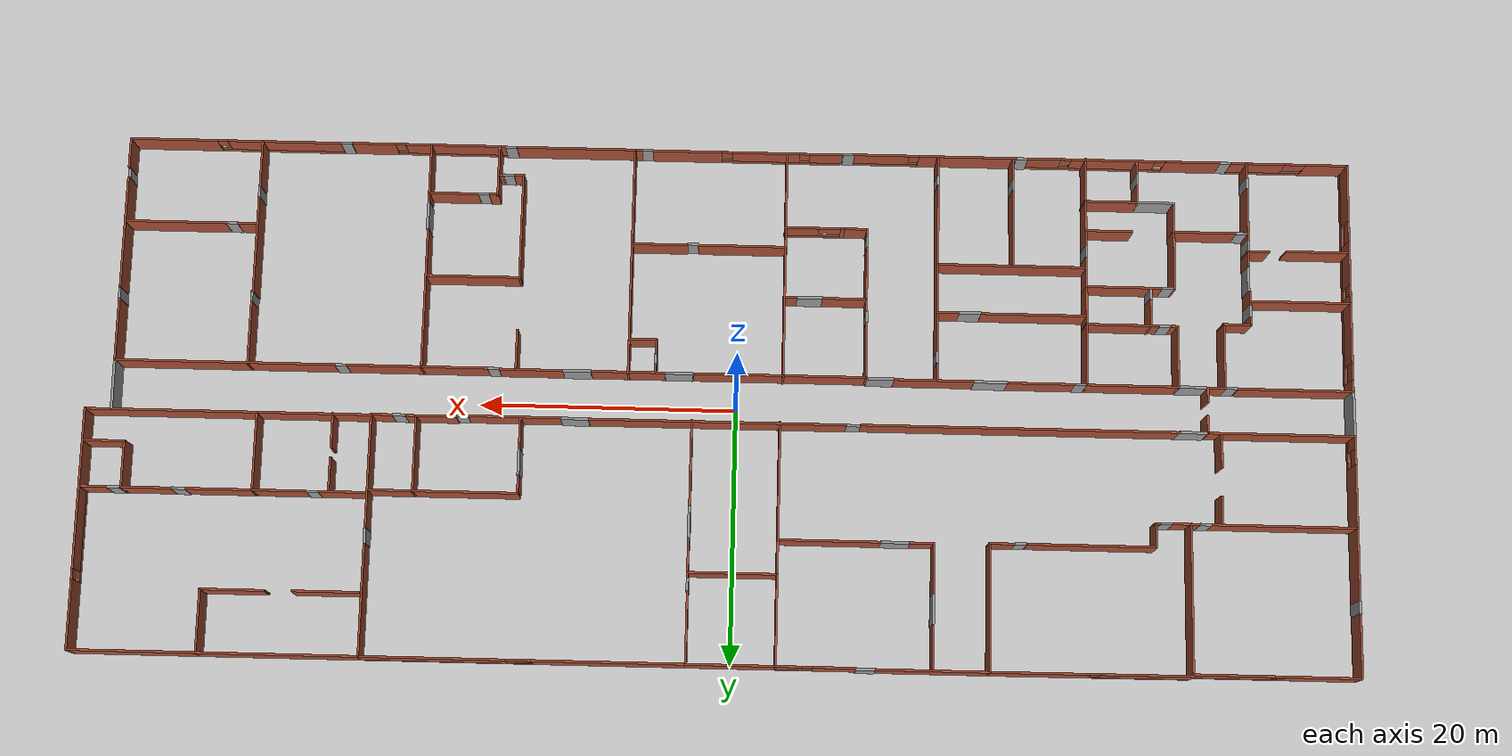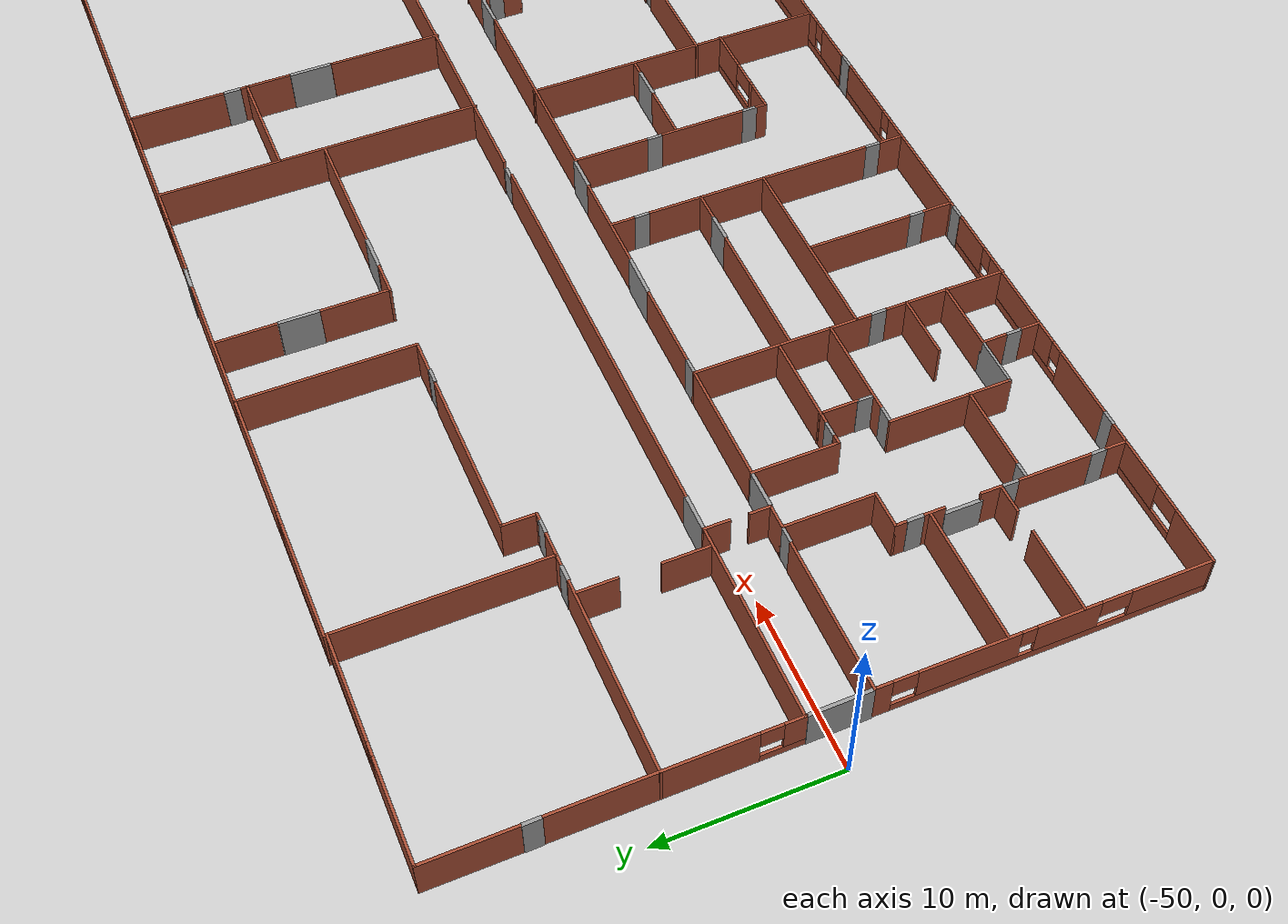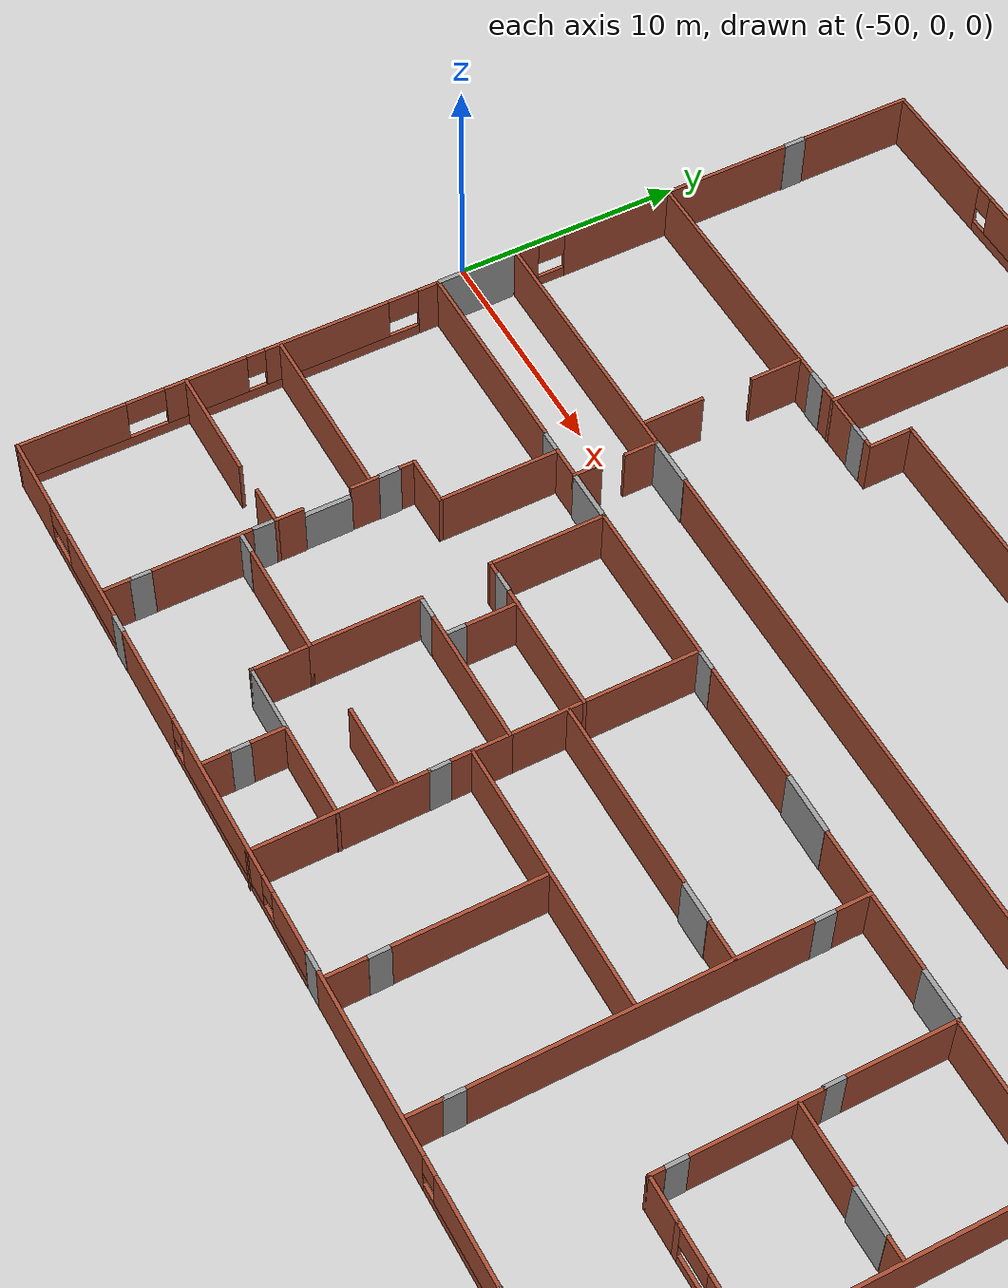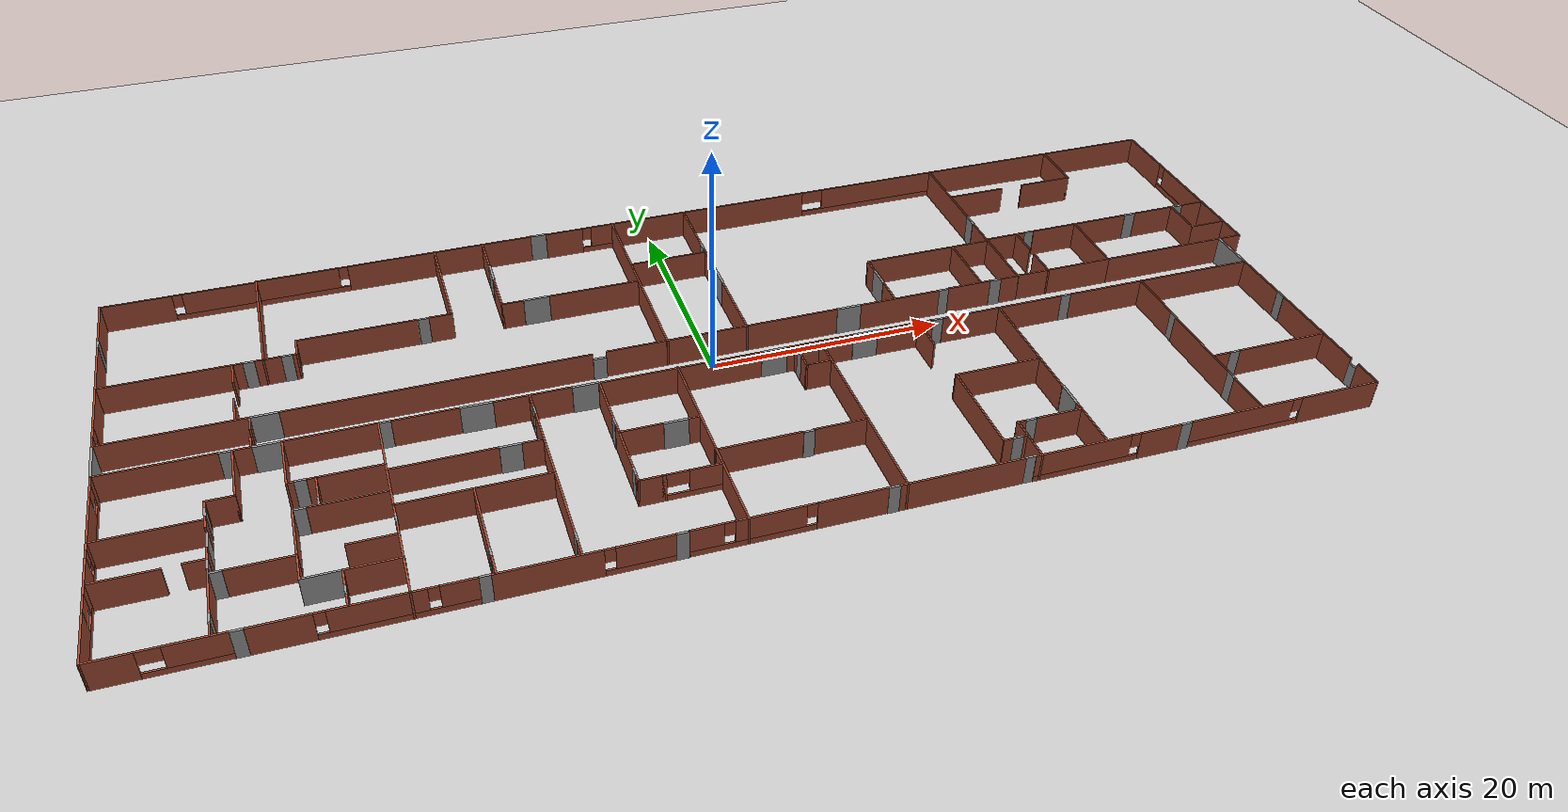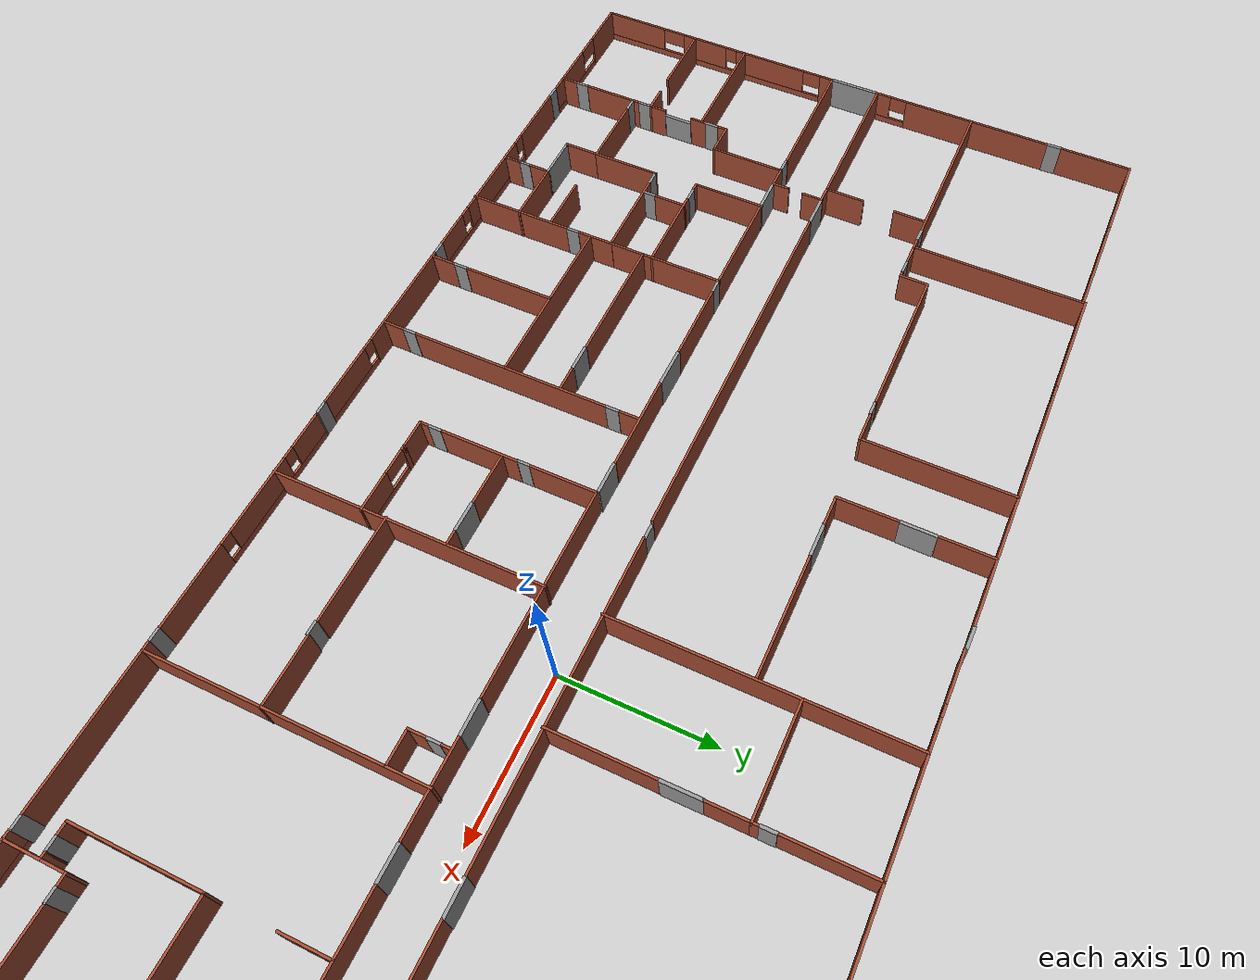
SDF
<sdf version='1.6'>
  <world name='default'>
    <!-- A global light source -->
    <include>
      <uri>model://sun</uri>
    </include>

    <!-- A ground plane -->
    <include>
      <uri>model://ground_plane</uri>
    </include>

    <physics type="ode">
      <real_time_update_rate>0</real_time_update_rate>
      <max_step_size>0.001</max_step_size>
      <real_time_factor>1</real_time_factor>
      <ode>
        <solver>
          <type>quick</type>
          <iters>150</iters>
          <precon_iters>0</precon_iters>
          <sor>1.400000</sor>
          <use_dynamic_moi_rescaling>1</use_dynamic_moi_rescaling>
        </solver>
        <constraints>
          <cfm>0.00001</cfm>
          <erp>0.2</erp>
          <contact_max_correcting_vel>2000.000000</contact_max_correcting_vel>
          <contact_surface_layer>0.01000</contact_surface_layer>
        </constraints>
      </ode>
    </physics>

    <!-- Load world -->
    <include>
      <uri>model://Bainer_Hall_FP</uri>
    </include>

    <scene>
      <ambient>0.4 0.4 0.4 1</ambient>
      <background>0.7 0.7 0.7 1</background>
      <shadows>true</shadows>
    </scene>

    <gui fullscreen='0'>
      <camera name='user_camera'>
        <pose>0.0 0.0 17.0 0 1.5708 0</pose>
        <view_controller>orbit</view_controller>
      </camera>
    </gui>
  </world>
</sdf>

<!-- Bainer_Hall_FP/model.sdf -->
<sdf version='1.6'>
  <model name='Bainer_Hall_FP'>
    <pose frame=''>1.25513 -0.156837 0 0 -0 0</pose>
    <link name='Door_10'>
      <collision name='Door_10_Collision'>
        <geometry>
          <box>
            <size>0.9 0.17 2.5</size>
          </box>
        </geometry>
        <pose frame=''>0 0 1.25 0 -0 0</pose>
      </collision>
      <visual name='Door_10_Visual'>
        <pose frame=''>0 0 1.25 0 -0 0</pose>
        <geometry>
          <box>
            <size>0.9 0.17 2.5</size>
          </box>
        </geometry>
        <material>
          <script>
            <uri>file://media/materials/scripts/gazebo.material</uri>
            <name>Gazebo/Grey</name>
          </script>
        </material>
      </visual>
      <pose frame=''>-34.5626 8.65196 0 0 -0 0</pose>
    </link>
    <link name='Door_11'>
      <collision name='Door_11_Collision'>
        <geometry>
          <box>
            <size>0.9 0.17 2.5</size>
          </box>
        </geometry>
        <pose frame=''>0 0 1.25 0 -0 0</pose>
      </collision>
      <visual name='Door_11_Visual'>
        <pose frame=''>0 0 1.25 0 -0 0</pose>
        <geometry>
          <box>
            <size>0.9 0.17 2.5</size>
          </box>
        </geometry>
        <material>
          <script>
            <uri>file://media/materials/scripts/gazebo.material</uri>
            <name>Gazebo/Grey</name>
          </script>
        </material>
      </visual>
      <pose frame=''>-23.3342 10.4772 0 0 -0 0</pose>
    </link>
    <link name='Door_12'>
      <collision name='Door_12_Collision'>
        <geometry>
          <box>
            <size>2.165 0.2 2.5</size>
          </box>
        </geometry>
        <pose frame=''>0 0 1.25 0 -0 0</pose>
      </collision>
      <visual name='Door_12_Visual'>
        <pose frame=''>0 0 1.25 0 -0 0</pose>
        <geometry>
          <box>
            <size>2.165 0.2 2.5</size>
          </box>
        </geometry>
        <material>
          <script>
            <uri>file://media/materials/scripts/gazebo.material</uri>
            <name>Gazebo/Grey</name>
          </script>
        </material>
      </visual>
      <pose frame=''>-36.6968 1.50114 0 0 -0 0</pose>
    </link>
    <link name='Door_14'>
      <collision name='Door_14_Collision'>
        <geometry>
          <box>
            <size>1.11106 0.2 2</size>
          </box>
        </geometry>
        <pose frame=''>0 0 1 0 -0 0</pose>
      </collision>
      <visual name='Door_14_Visual'>
        <pose frame=''>0 0 1 0 -0 0</pose>
        <geometry>
          <box>
            <size>1.11106 0.2 2</size>
          </box>
        </geometry>
        <material>
          <script>
            <uri>file://media/materials/scripts/gazebo.material</uri>
            <name>Gazebo/Grey</name>
          </script>
        </material>
      </visual>
      <pose frame=''>-10.4248 1.46984 0 0 -0 0</pose>
    </link>
    <link name='Door_15'>
      <collision name='Door_15_Collision'>
        <geometry>
          <box>
            <size>2.143 0.2 2.5</size>
          </box>
        </geometry>
        <pose frame=''>0 0 1.25 0 -0 0</pose>
      </collision>
      <visual name='Door_15_Visual'>
        <pose frame=''>0 0 1.25 0 -0 0</pose>
        <geometry>
          <box>
            <size>2.143 0.2 2.5</size>
          </box>
        </geometry>
        <material>
          <script>
            <uri>file://media/materials/scripts/gazebo.material</uri>
            <name>Gazebo/Grey</name>
          </script>
        </material>
      </visual>
      <pose frame=''>11.2185 1.52839 0 0 -0 0</pose>
    </link>
    <link name='Door_16'>
      <collision name='Door_16_Collision'>
        <geometry>
          <box>
            <size>1.464 0.2 2.5</size>
          </box>
        </geometry>
        <pose frame=''>0 0 1.25 0 -0 0</pose>
      </collision>
      <visual name='Door_16_Visual'>
        <pose frame=''>0 0 1.25 0 -0 0</pose>
        <geometry>
          <box>
            <size>1.464 0.2 2.5</size>
          </box>
        </geometry>
        <material>
          <script>
            <uri>file://media/materials/scripts/gazebo.material</uri>
            <name>Gazebo/Grey</name>
          </script>
        </material>
      </visual>
      <pose frame=''>-11.5568 20.3759 0 0 -0 3.12319</pose>
    </link>
    <link name='Door_17'>
      <collision name='Door_17_Collision'>
        <geometry>
          <box>
            <size>2.225 0.2 2.5</size>
          </box>
        </geometry>
        <pose frame=''>0 0 1.25 0 -0 0</pose>
      </collision>
      <visual name='Door_17_Visual'>
        <pose frame=''>0 0 1.25 0 -0 0</pose>
        <geometry>
          <box>
            <size>2.225 0.2 2.5</size>
          </box>
        </geometry>
        <material>
          <script>
            <uri>file://media/materials/scripts/gazebo.material</uri>
            <name>Gazebo/Grey</name>
          </script>
        </material>
      </visual>
      <pose frame=''>-13.7307 10.6137 0 0 -0 0</pose>
    </link>
    <link name='Door_19'>
      <collision name='Door_19_Collision'>
        <geometry>
          <box>
            <size>2.29098 0.2 2.5</size>
          </box>
        </geometry>
        <pose frame=''>0 0 1.25 0 -0 0</pose>
      </collision>
      <visual name='Door_19_Visual'>
        <pose frame=''>0 0 1.25 0 -0 0</pose>
        <geometry>
          <box>
            <size>2.29098 0.2 2.5</size>
          </box>
        </geometry>
        <material>
          <script>
            <uri>file://media/materials/scripts/gazebo.material</uri>
            <name>Gazebo/Grey</name>
          </script>
        </material>
      </visual>
      <pose frame=''>-16.6651 15.6807 0 0 0 -1.58178</pose>
    </link>
    <link name='Door_20'>
      <collision name='Door_20_Collision'>
        <geometry>
          <box>
            <size>2.518 0.2 2.5</size>
          </box>
        </geometry>
        <pose frame=''>0 0 1.25 0 -0 0</pose>
      </collision>
      <visual name='Door_20_Visual'>
        <pose frame=''>0 0 1.25 0 -0 0</pose>
        <geometry>
          <box>
            <size>2.518 0.2 2.5</size>
          </box>
        </geometry>
        <material>
          <script>
            <uri>file://media/materials/scripts/gazebo.material</uri>
            <name>Gazebo/Grey</name>
          </script>
        </material>
      </visual>
      <pose frame=''>2.14668 9.40743 0 0 -0 1.57339</pose>
    </link>
    <link name='Door_21'>
      <collision name='Door_21_Collision'>
        <geometry>
          <box>
            <size>1.007 0.2 2.5</size>
          </box>
        </geometry>
        <pose frame=''>0 0 1.25 0 -0 0</pose>
      </collision>
      <visual name='Door_21_Visual'>
        <pose frame=''>0 0 1.25 0 -0 0</pose>
        <geometry>
          <box>
            <size>1.007 0.2 2.5</size>
          </box>
        </geometry>
        <material>
          <script>
            <uri>file://media/materials/scripts/gazebo.material</uri>
            <name>Gazebo/Grey</name>
          </script>
        </material>
      </visual>
      <pose frame=''>2.14334 14.2049 0 0 0 -1.5708</pose>
    </link>
    <link name='Door_22'>
      <collision name='Door_22_Collision'>
        <geometry>
          <box>
            <size>1.17263 0.2 2.5</size>
          </box>
        </geometry>
        <pose frame=''>0 0 1.25 0 -0 0</pose>
      </collision>
      <visual name='Door_22_Visual'>
        <pose frame=''>0 0 1.25 0 -0 0</pose>
        <geometry>
          <box>
            <size>1.17263 0.2 2.5</size>
          </box>
        </geometry>
        <material>
          <script>
            <uri>file://media/materials/scripts/gazebo.material</uri>
            <name>Gazebo/Grey</name>
          </script>
        </material>
      </visual>
      <pose frame=''>26.9821 11.0502 0 0 0 -1.55803</pose>
    </link>
    <link name='Door_23'>
      <collision name='Door_23_Collision'>
        <geometry>
          <box>
            <size>1.01 0.2 2.5</size>
          </box>
        </geometry>
        <pose frame=''>0 0 1.25 0 -0 0</pose>
      </collision>
      <visual name='Door_23_Visual'>
        <pose frame=''>0 0 1.25 0 -0 0</pose>
        <geometry>
          <box>
            <size>1.01 0.2 2.5</size>
          </box>
        </geometry>
        <material>
          <script>
            <uri>file://media/materials/scripts/gazebo.material</uri>
            <name>Gazebo/Grey</name>
          </script>
        </material>
      </visual>
      <pose frame=''>24.8391 1.55098 0 0 -0 3.10452</pose>
    </link>
    <link name='Door_24'>
      <collision name='Door_24_Collision'>
        <geometry>
          <box>
            <size>0.9 0.17 2.5</size>
          </box>
        </geometry>
        <pose frame=''>0 0 1.25 0 -0 0</pose>
      </collision>
      <visual name='Door_24_Visual'>
        <pose frame=''>0 0 1.25 0 -0 0</pose>
        <geometry>
          <box>
            <size>0.9 0.17 2.5</size>
          </box>
        </geometry>
        <material>
          <script>
            <uri>file://media/materials/scripts/gazebo.material</uri>
            <name>Gazebo/Grey</name>
          </script>
        </material>
      </visual>
      <pose frame=''>19.9109 1.51909 0 0 -0 0</pose>
    </link>
    <link name='Door_25'>
      <collision name='Door_25_Collision'>
        <geometry>
          <box>
            <size>2.087 0.2 2.5</size>
          </box>
        </geometry>
        <pose frame=''>0 0 1.25 0 -0 0</pose>
      </collision>
      <visual name='Door_25_Visual'>
        <pose frame=''>0 0 1.25 0 -0 0</pose>
        <geometry>
          <box>
            <size>2.087 0.2 2.5</size>
          </box>
        </geometry>
        <material>
          <script>
            <uri>file://media/materials/scripts/gazebo.material</uri>
            <name>Gazebo/Grey</name>
          </script>
        </material>
      </visual>
      <pose frame=''>15.4161 5.0222 0 0 0 -1.5708</pose>
    </link>
    <link name='Door_26'>
      <collision name='Door_26_Collision'>
        <geometry>
          <box>
            <size>1.035 0.2 2.5</size>
          </box>
        </geometry>
        <pose frame=''>0 0 1.25 0 -0 0</pose>
      </collision>
      <visual name='Door_26_Visual'>
        <pose frame=''>0 0 1.25 0 -0 0</pose>
        <geometry>
          <box>
            <size>1.035 0.2 2.5</size>
          </box>
        </geometry>
        <material>
          <script>
            <uri>file://media/materials/scripts/gazebo.material</uri>
            <name>Gazebo/Grey</name>
          </script>
        </material>
      </visual>
      <pose frame=''>41.537 7.70908 0 0 -0 0</pose>
    </link>
    <link name='Door_27'>
      <collision name='Door_27_Collision'>
        <geometry>
          <box>
            <size>0.989792 0.2 2.5</size>
          </box>
        </geometry>
        <pose frame=''>0 0 1.25 0 -0 0</pose>
      </collision>
      <visual name='Door_27_Visual'>
        <pose frame=''>0 0 1.25 0 -0 0</pose>
        <geometry>
          <box>
            <size>0.989792 0.2 2.5</size>
          </box>
        </geometry>
        <material>
          <script>
            <uri>file://media/materials/scripts/gazebo.material</uri>
            <name>Gazebo/Grey</name>
          </script>
        </material>
      </visual>
      <pose frame=''>46.5429 7.70908 0 0 -0 0</pose>
    </link>
    <link name='Door_28'>
      <collision name='Door_28_Collision'>
        <geometry>
          <box>
            <size>0.9 0.17 2.5</size>
          </box>
        </geometry>
        <pose frame=''>0 0 1.25 0 -0 0</pose>
      </collision>
      <visual name='Door_28_Visual'>
        <pose frame=''>0 0 1.25 0 -0 0</pose>
        <geometry>
          <box>
            <size>0.9 0.17 2.5</size>
          </box>
        </geometry>
        <material>
          <script>
            <uri>file://media/materials/scripts/gazebo.material</uri>
            <name>Gazebo/Grey</name>
          </script>
        </material>
      </visual>
      <pose frame=''>31.1816 7.72893 0 0 -0 0</pose>
    </link>
    <link name='Door_29'>
      <collision name='Door_29_Collision'>
        <geometry>
          <box>
            <size>0.9 0.17 2.5</size>
          </box>
        </geometry>
        <pose frame=''>0 0 1.25 0 -0 0</pose>
      </collision>
      <visual name='Door_29_Visual'>
        <pose frame=''>0 0 1.25 0 -0 0</pose>
        <geometry>
          <box>
            <size>0.9 0.17 2.5</size>
          </box>
        </geometry>
        <material>
          <script>
            <uri>file://media/materials/scripts/gazebo.material</uri>
            <name>Gazebo/Grey</name>
          </script>
        </material>
      </visual>
      <pose frame=''>-39.7621 -2.07664 0 0 0 -3.14159</pose>
    </link>
    <link name='Door_30'>
      <collision name='Door_30_Collision'>
        <geometry>
          <box>
            <size>2.11069 0.2 2.5</size>
          </box>
        </geometry>
        <pose frame=''>0 0 1.25 0 -0 0</pose>
      </collision>
      <visual name='Door_30_Visual'>
        <pose frame=''>0 0 1.25 0 -0 0</pose>
        <geometry>
          <box>
            <size>2.11069 0.2 2.5</size>
          </box>
        </geometry>
        <material>
          <script>
            <uri>file://media/materials/scripts/gazebo.material</uri>
            <name>Gazebo/Grey</name>
          </script>
        </material>
      </visual>
      <pose frame=''>-36.7462 -2.09134 0 0 -0 0</pose>
    </link>
    <link name='Door_31'>
      <collision name='Door_31_Collision'>
        <geometry>
          <box>
            <size>0.9 0.17 2.5</size>
          </box>
        </geometry>
        <pose frame=''>0 0 1.25 0 -0 0</pose>
      </collision>
      <visual name='Door_31_Visual'>
        <pose frame=''>0 0 1.25 0 -0 0</pose>
        <geometry>
          <box>
            <size>0.9 0.17 2.5</size>
          </box>
        </geometry>
        <material>
          <script>
            <uri>file://media/materials/scripts/gazebo.material</uri>
            <name>Gazebo/Grey</name>
          </script>
        </material>
      </visual>
      <pose frame=''>-34.6539 -6.91196 0 0 -0 0</pose>
    </link>
    <link name='Door_32'>
      <collision name='Door_32_Collision'>
        <geometry>
          <box>
            <size>0.9 0.17 2.5</size>
          </box>
        </geometry>
        <pose frame=''>0 0 1.25 0 -0 0</pose>
      </collision>
      <visual name='Door_32_Visual'>
        <pose frame=''>0 0 1.25 0 -0 0</pose>
        <geometry>
          <box>
            <size>0.9 0.17 2.5</size>
          </box>
        </geometry>
        <material>
          <script>
            <uri>file://media/materials/scripts/gazebo.material</uri>
            <name>Gazebo/Grey</name>
          </script>
        </material>
      </visual>
      <pose frame=''>-28.0011 -2.09981 0 0 -0 0</pose>
    </link>
    <link name='Door_33'>
      <collision name='Door_33_Collision'>
        <geometry>
          <box>
            <size>2.592 0.2 2.5</size>
          </box>
        </geometry>
        <pose frame=''>0 0 1.25 0 -0 0</pose>
      </collision>
      <visual name='Door_33_Visual'>
        <pose frame=''>0 0 1.25 0 -0 0</pose>
        <geometry>
          <box>
            <size>2.592 0.2 2.5</size>
          </box>
        </geometry>
        <material>
          <script>
            <uri>file://media/materials/scripts/gazebo.material</uri>
            <name>Gazebo/Grey</name>
          </script>
        </material>
      </visual>
      <pose frame=''>-21.0189 -2.12561 0 0 -0 3.12756</pose>
    </link>
    <link name='Door_34'>
      <collision name='Door_34_Collision'>
        <geometry>
          <box>
            <size>2.11 0.2 2.5</size>
          </box>
        </geometry>
        <pose frame=''>0 0 1.25 0 -0 0</pose>
      </collision>
      <visual name='Door_34_Visual'>
        <pose frame=''>0 0 1.25 0 -0 0</pose>
        <geometry>
          <box>
            <size>2.11 0.2 2.5</size>
          </box>
        </geometry>
        <material>
          <script>
            <uri>file://media/materials/scripts/gazebo.material</uri>
            <name>Gazebo/Grey</name>
          </script>
        </material>
      </visual>
      <pose frame=''>-12.4392 -2.19282 0 0 0 -3.14115</pose>
    </link>
    <link name='Door_35'>
      <collision name='Door_35_Collision'>
        <geometry>
          <box>
            <size>2.157 0.2 2.5</size>
          </box>
        </geometry>
        <pose frame=''>0 0 1.25 0 -0 0</pose>
      </collision>
      <visual name='Door_35_Visual'>
        <pose frame=''>0 0 1.25 0 -0 0</pose>
        <geometry>
          <box>
            <size>2.157 0.2 2.5</size>
          </box>
        </geometry>
        <material>
          <script>
            <uri>file://media/materials/scripts/gazebo.material</uri>
            <name>Gazebo/Grey</name>
          </script>
        </material>
      </visual>
      <pose frame=''>3.22764 -2.26006 0 0 0 -3.13357</pose>
    </link>
    <link name='Door_36'>
      <collision name='Door_36_Collision'>
        <geometry>
          <box>
            <size>2.157 0.2 2.5</size>
          </box>
        </geometry>
        <pose frame=''>0 0 1.25 0 -0 0</pose>
      </collision>
      <visual name='Door_36_Visual'>
        <pose frame=''>0 0 1.25 0 -0 0</pose>
        <geometry>
          <box>
            <size>2.157 0.2 2.5</size>
          </box>
        </geometry>
        <material>
          <script>
            <uri>file://media/materials/scripts/gazebo.material</uri>
            <name>Gazebo/Grey</name>
          </script>
        </material>
      </visual>
      <pose frame=''>11.1742 -2.26006 0 0 -0 0</pose>
    </link>
    <link name='Door_37'>
      <collision name='Door_37_Collision'>
        <geometry>
          <box>
            <size>0.9 0.17 2.5</size>
          </box>
        </geometry>
        <pose frame=''>0 0 1.25 0 -0 0</pose>
      </collision>
      <visual name='Door_37_Visual'>
        <pose frame=''>0 0 1.25 0 -0 0</pose>
        <geometry>
          <box>
            <size>0.9 0.17 2.5</size>
          </box>
        </geometry>
        <material>
          <script>
            <uri>file://media/materials/scripts/gazebo.material</uri>
            <name>Gazebo/Grey</name>
          </script>
        </material>
      </visual>
      <pose frame=''>17.6392 -2.30496 0 0 -0 0</pose>
    </link>
    <link name='Door_38'>
      <collision name='Door_38_Collision'>
        <geometry>
          <box>
            <size>0.9 0.17 2.5</size>
          </box>
        </geometry>
        <pose frame=''>0 0 1.25 0 -0 0</pose>
      </collision>
      <visual name='Door_38_Visual'>
        <pose frame=''>0 0 1.25 0 -0 0</pose>
        <geometry>
          <box>
            <size>0.9 0.17 2.5</size>
          </box>
        </geometry>
        <material>
          <script>
            <uri>file://media/materials/scripts/gazebo.material</uri>
            <name>Gazebo/Grey</name>
          </script>
        </material>
      </visual>
      <pose frame=''>29.5592 -2.30521 0 0 0 -3.13072</pose>
    </link>
    <link name='Door_39'>
      <collision name='Door_39_Collision'>
        <geometry>
          <box>
            <size>0.9 0.17 2.5</size>
          </box>
        </geometry>
        <pose frame=''>0 0 1.25 0 -0 0</pose>
      </collision>
      <visual name='Door_39_Visual'>
        <pose frame=''>0 0 1.25 0 -0 0</pose>
        <geometry>
          <box>
            <size>0.9 0.17 2.5</size>
          </box>
        </geometry>
        <material>
          <script>
            <uri>file://media/materials/scripts/gazebo.material</uri>
            <name>Gazebo/Grey</name>
          </script>
        </material>
      </visual>
      <pose frame=''>47.1899 -7.6622 0 0 -0 1.55378</pose>
    </link>
    <link name='Door_40'>
      <collision name='Door_40_Collision'>
        <geometry>
          <box>
            <size>0.9 0.17 2</size>
          </box>
        </geometry>
        <pose frame=''>0 0 1 0 -0 0</pose>
      </collision>
      <visual name='Door_40_Visual'>
        <pose frame=''>0 0 1 0 -0 0</pose>
        <geometry>
          <box>
            <size>0.9 0.17 2</size>
          </box>
        </geometry>
        <material>
          <script>
            <uri>file://media/materials/scripts/gazebo.material</uri>
            <name>Gazebo/Grey</name>
          </script>
        </material>
      </visual>
      <pose frame=''>47.2284 -17.5715 0 0 -0 1.63085</pose>
    </link>
    <link name='Door_42'>
      <collision name='Door_42_Collision'>
        <geometry>
          <box>
            <size>0.9 0.17 2.5</size>
          </box>
        </geometry>
        <pose frame=''>0 0 1.25 0 -0 0</pose>
      </collision>
      <visual name='Door_42_Visual'>
        <pose frame=''>0 0 1.25 0 -0 0</pose>
        <geometry>
          <box>
            <size>0.9 0.17 2.5</size>
          </box>
        </geometry>
        <material>
          <script>
            <uri>file://media/materials/scripts/gazebo.material</uri>
            <name>Gazebo/Grey</name>
          </script>
        </material>
      </visual>
      <pose frame=''>30.1038 -20.3171 0 0 -0 0</pose>
    </link>
    <link name='Door_43'>
      <collision name='Door_43_Collision'>
        <geometry>
          <box>
            <size>0.9 0.17 2.5</size>
          </box>
        </geometry>
        <pose frame=''>0 0 1.25 0 -0 0</pose>
      </collision>
      <visual name='Door_43_Visual'>
        <pose frame=''>0 0 1.25 0 -0 0</pose>
        <geometry>
          <box>
            <size>0.9 0.17 2.5</size>
          </box>
        </geometry>
        <material>
          <script>
            <uri>file://media/materials/scripts/gazebo.material</uri>
            <name>Gazebo/Grey</name>
          </script>
        </material>
      </visual>
      <pose frame=''>17.011 -20.2734 0 0 -0 0</pose>
    </link>
    <link name='Door_44'>
      <collision name='Door_44_Collision'>
        <geometry>
          <box>
            <size>2.20957 0.2 2.5</size>
          </box>
        </geometry>
        <pose frame=''>0 0 1.25 0 -0 0</pose>
      </collision>
      <visual name='Door_44_Visual'>
        <pose frame=''>0 0 1.25 0 -0 0</pose>
        <geometry>
          <box>
            <size>2.20957 0.2 2.5</size>
          </box>
        </geometry>
        <material>
          <script>
            <uri>file://media/materials/scripts/gazebo.material</uri>
            <name>Gazebo/Grey</name>
          </script>
        </material>
      </visual>
      <pose frame=''>23.3396 -14.5504 0 0 0 -1.58102</pose>
    </link>
    <link name='Door_45'>
      <collision name='Door_45_Collision'>
        <geometry>
          <box>
            <size>0.9 0.17 2.5</size>
          </box>
        </geometry>
        <pose frame=''>0 0 1.25 0 -0 0</pose>
      </collision>
      <visual name='Door_45_Visual'>
        <pose frame=''>0 0 1.25 0 -0 0</pose>
        <geometry>
          <box>
            <size>0.9 0.17 2.5</size>
          </box>
        </geometry>
        <material>
          <script>
            <uri>file://media/materials/scripts/gazebo.material</uri>
            <name>Gazebo/Grey</name>
          </script>
        </material>
      </visual>
      <pose frame=''>17.1411 -17.9894 0 0 0 -3.1354</pose>
    </link>
    <link name='Door_46'>
      <collision name='Door_46_Collision'>
        <geometry>
          <box>
            <size>0.9 0.17 2.5</size>
          </box>
        </geometry>
        <pose frame=''>0 0 1.25 0 -0 0</pose>
      </collision>
      <visual name='Door_46_Visual'>
        <pose frame=''>0 0 1.25 0 -0 0</pose>
        <geometry>
          <box>
            <size>0.9 0.17 2.5</size>
          </box>
        </geometry>
        <material>
          <script>
            <uri>file://media/materials/scripts/gazebo.material</uri>
            <name>Gazebo/Grey</name>
          </script>
        </material>
      </visual>
      <pose frame=''>19.031 -16.3929 0 0 -0 0</pose>
    </link>
    <link name='Door_47'>
      <collision name='Door_47_Collision'>
        <geometry>
          <box>
            <size>0.9 0.17 2.5</size>
          </box>
        </geometry>
        <pose frame=''>0 0 1.25 0 -0 0</pose>
      </collision>
      <visual name='Door_47_Visual'>
        <pose frame=''>0 0 1.25 0 -0 0</pose>
        <geometry>
          <box>
            <size>0.9 0.17 2.5</size>
          </box>
        </geometry>
        <material>
          <script>
            <uri>file://media/materials/scripts/gazebo.material</uri>
            <name>Gazebo/Grey</name>
          </script>
        </material>
      </visual>
      <pose frame=''>6.17549 -20.287 0 0 -0 0</pose>
    </link>
    <link name='Door_48'>
      <collision name='Door_48_Collision'>
        <geometry>
          <box>
            <size>0.9 0.17 2.5</size>
          </box>
        </geometry>
        <pose frame=''>0 0 1.25 0 -0 0</pose>
      </collision>
      <visual name='Door_48_Visual'>
        <pose frame=''>0 0 1.25 0 -0 0</pose>
        <geometry>
          <box>
            <size>0.9 0.17 2.5</size>
          </box>
        </geometry>
        <material>
          <script>
            <uri>file://media/materials/scripts/gazebo.material</uri>
            <name>Gazebo/Grey</name>
          </script>
        </material>
      </visual>
      <pose frame=''>-9.75215 -20.292 0 0 -0 0</pose>
    </link>
    <link name='Door_49'>
      <collision name='Door_49_Collision'>
        <geometry>
          <box>
            <size>0.94 0.2 2.5</size>
          </box>
        </geometry>
        <pose frame=''>0 0 1.25 0 -0 0</pose>
      </collision>
      <visual name='Door_49_Visual'>
        <pose frame=''>0 0 1.25 0 -0 0</pose>
        <geometry>
          <box>
            <size>0.94 0.2 2.5</size>
          </box>
        </geometry>
        <material>
          <script>
            <uri>file://media/materials/scripts/gazebo.material</uri>
            <name>Gazebo/Grey</name>
          </script>
        </material>
      </visual>
      <pose frame=''>-41.3093 -8.28276 0 0 -0 1.57919</pose>
    </link>
    <link name='Door_50'>
      <collision name='Door_50_Collision'>
        <geometry>
          <box>
            <size>2.14227 0.2 2</size>
          </box>
        </geometry>
        <pose frame=''>0 0 1 0 -0 0</pose>
      </collision>
      <visual name='Door_50_Visual'>
        <pose frame=''>0 0 1 0 -0 0</pose>
        <geometry>
          <box>
            <size>2.14227 0.2 2</size>
          </box>
        </geometry>
        <material>
          <script>
            <uri>file://media/materials/scripts/gazebo.material</uri>
            <name>Gazebo/Grey</name>
          </script>
        </material>
      </visual>
      <pose frame=''>-41.3097 -10.9944 0 0 -0 1.5708</pose>
    </link>
    <link name='Door_51'>
      <collision name='Door_51_Collision'>
        <geometry>
          <box>
            <size>0.9 0.17 2.5</size>
          </box>
        </geometry>
        <pose frame=''>0 0 1.25 0 -0 0</pose>
      </collision>
      <visual name='Door_51_Visual'>
        <pose frame=''>0 0 1.25 0 -0 0</pose>
        <geometry>
          <box>
            <size>0.9 0.17 2.5</size>
          </box>
        </geometry>
        <material>
          <script>
            <uri>file://media/materials/scripts/gazebo.material</uri>
            <name>Gazebo/Grey</name>
          </script>
        </material>
      </visual>
      <pose frame=''>-41.2641 -13.6308 0 0 0 -1.57632</pose>
    </link>
    <link name='Door_52'>
      <collision name='Door_52_Collision'>
        <geometry>
          <box>
            <size>0.9 0.17 2.5</size>
          </box>
        </geometry>
        <pose frame=''>0 0 1.25 0 -0 0</pose>
      </collision>
      <visual name='Door_52_Visual'>
        <pose frame=''>0 0 1.25 0 -0 0</pose>
        <geometry>
          <box>
            <size>0.9 0.17 2.5</size>
          </box>
        </geometry>
        <material>
          <script>
            <uri>file://media/materials/scripts/gazebo.material</uri>
            <name>Gazebo/Grey</name>
          </script>
        </material>
      </visual>
      <pose frame=''>-41.2637 -18.7055 0 0 -0 1.5708</pose>
    </link>
    <link name='Door_53'>
      <collision name='Door_53_Collision'>
        <geometry>
          <box>
            <size>0.9 0.17 2.5</size>
          </box>
        </geometry>
        <pose frame=''>0 0 1.25 0 -0 0</pose>
      </collision>
      <visual name='Door_53_Visual'>
        <pose frame=''>0 0 1.25 0 -0 0</pose>
        <geometry>
          <box>
            <size>0.9 0.17 2.5</size>
          </box>
        </geometry>
        <material>
          <script>
            <uri>file://media/materials/scripts/gazebo.material</uri>
            <name>Gazebo/Grey</name>
          </script>
        </material>
      </visual>
      <pose frame=''>-40.7662 -14.5556 0 0 -0 0</pose>
    </link>
    <link name='Door_54'>
      <collision name='Door_54_Collision'>
        <geometry>
          <box>
            <size>0.9 0.17 2.5</size>
          </box>
        </geometry>
        <pose frame=''>0 0 1.25 0 -0 0</pose>
      </collision>
      <visual name='Door_54_Visual'>
        <pose frame=''>0 0 1.25 0 -0 0</pose>
        <geometry>
          <box>
            <size>0.9 0.17 2.5</size>
          </box>
        </geometry>
        <material>
          <script>
            <uri>file://media/materials/scripts/gazebo.material</uri>
            <name>Gazebo/Grey</name>
          </script>
        </material>
      </visual>
      <pose frame=''>-32.5666 -18.7651 0 0 0 -1.5708</pose>
    </link>
    <link name='Door_56'>
      <collision name='Door_56_Collision'>
        <geometry>
          <box>
            <size>0.9 0.17 2.5</size>
          </box>
        </geometry>
        <pose frame=''>0 0 1.25 0 -0 0</pose>
      </collision>
      <visual name='Door_56_Visual'>
        <pose frame=''>0 0 1.25 0 -0 0</pose>
        <geometry>
          <box>
            <size>0.9 0.17 2.5</size>
          </box>
        </geometry>
        <material>
          <script>
            <uri>file://media/materials/scripts/gazebo.material</uri>
            <name>Gazebo/Grey</name>
          </script>
        </material>
      </visual>
      <pose frame=''>-34.8989 -9.9638 0 0 -0 0</pose>
    </link>
    <link name='Door_57'>
      <collision name='Door_57_Collision'>
        <geometry>
          <box>
            <size>0.9 0.17 2.5</size>
          </box>
        </geometry>
        <pose frame=''>0 0 1.25 0 -0 0</pose>
      </collision>
      <visual name='Door_57_Visual'>
        <pose frame=''>0 0 1.25 0 -0 0</pose>
        <geometry>
          <box>
            <size>0.9 0.17 2.5</size>
          </box>
        </geometry>
        <material>
          <script>
            <uri>file://media/materials/scripts/gazebo.material</uri>
            <name>Gazebo/Grey</name>
          </script>
        </material>
      </visual>
      <pose frame=''>-33.5499 -9.44231 0 0 -0 1.5708</pose>
    </link>
    <link name='Door_59'>
      <collision name='Door_59_Collision'>
        <geometry>
          <box>
            <size>0.9 0.17 2.5</size>
          </box>
        </geometry>
        <pose frame=''>0 0 1.25 0 -0 0</pose>
      </collision>
      <visual name='Door_59_Visual'>
        <pose frame=''>0 0 1.25 0 -0 0</pose>
        <geometry>
          <box>
            <size>0.9 0.17 2.5</size>
          </box>
        </geometry>
        <material>
          <script>
            <uri>file://media/materials/scripts/gazebo.material</uri>
            <name>Gazebo/Grey</name>
          </script>
        </material>
      </visual>
      <pose frame=''>-39.6193 -20.3098 0 0 -0 0</pose>
    </link>
    <link name='Door_6'>
      <collision name='Door_6_Collision'>
        <geometry>
          <box>
            <size>0.992 0.2 2.5</size>
          </box>
        </geometry>
        <pose frame=''>0 0 1.25 0 -0 0</pose>
      </collision>
      <visual name='Door_6_Visual'>
        <pose frame=''>0 0 1.25 0 -0 0</pose>
        <geometry>
          <box>
            <size>0.992 0.2 2.5</size>
          </box>
        </geometry>
        <material>
          <script>
            <uri>file://media/materials/scripts/gazebo.material</uri>
            <name>Gazebo/Grey</name>
          </script>
        </material>
      </visual>
      <pose frame=''>-49.1881 14.7778 0 0 0 -1.55735</pose>
    </link>
    <link name='Door_60'>
      <collision name='Door_60_Collision'>
        <geometry>
          <box>
            <size>0.9 0.17 2.5</size>
          </box>
        </geometry>
        <pose frame=''>0 0 1.25 0 -0 0</pose>
      </collision>
      <visual name='Door_60_Visual'>
        <pose frame=''>0 0 1.25 0 -0 0</pose>
        <geometry>
          <box>
            <size>0.9 0.17 2.5</size>
          </box>
        </geometry>
        <material>
          <script>
            <uri>file://media/materials/scripts/gazebo.material</uri>
            <name>Gazebo/Grey</name>
          </script>
        </material>
      </visual>
      <pose frame=''>-28.5031 -12.8222 0 0 -0 1.59264</pose>
    </link>
    <link name='Door_61'>
      <collision name='Door_61_Collision'>
        <geometry>
          <box>
            <size>0.9 0.17 2.5</size>
          </box>
        </geometry>
        <pose frame=''>0 0 1.25 0 -0 0</pose>
      </collision>
      <visual name='Door_61_Visual'>
        <pose frame=''>0 0 1.25 0 -0 0</pose>
        <geometry>
          <box>
            <size>0.9 0.17 2.5</size>
          </box>
        </geometry>
        <material>
          <script>
            <uri>file://media/materials/scripts/gazebo.material</uri>
            <name>Gazebo/Grey</name>
          </script>
        </material>
      </visual>
      <pose frame=''>-16.8508 -4.01792 0 0 -0 1.57286</pose>
    </link>
    <link name='Door_62'>
      <collision name='Door_62_Collision'>
        <geometry>
          <box>
            <size>0.9 0.17 2.5</size>
          </box>
        </geometry>
        <pose frame=''>0 0 1.25 0 -0 0</pose>
      </collision>
      <visual name='Door_62_Visual'>
        <pose frame=''>0 0 1.25 0 -0 0</pose>
        <geometry>
          <box>
            <size>0.9 0.17 2.5</size>
          </box>
        </geometry>
        <material>
          <script>
            <uri>file://media/materials/scripts/gazebo.material</uri>
            <name>Gazebo/Grey</name>
          </script>
        </material>
      </visual>
      <pose frame=''>-16.8428 -18.4047 0 0 -0 1.55866</pose>
    </link>
    <link name='Door_63'>
      <collision name='Door_63_Collision'>
        <geometry>
          <box>
            <size>1.71 0.2 2.5</size>
          </box>
        </geometry>
        <pose frame=''>0 0 1.25 0 -0 0</pose>
      </collision>
      <visual name='Door_63_Visual'>
        <pose frame=''>0 0 1.25 0 -0 0</pose>
        <geometry>
          <box>
            <size>1.71 0.2 2.5</size>
          </box>
        </geometry>
        <material>
          <script>
            <uri>file://media/materials/scripts/gazebo.material</uri>
            <name>Gazebo/Grey</name>
          </script>
        </material>
      </visual>
      <pose frame=''>-19.4005 -7.62221 0 0 -0 3.14079</pose>
    </link>
    <link name='Door_64'>
      <collision name='Door_64_Collision'>
        <geometry>
          <box>
            <size>0.9 0.17 2.5</size>
          </box>
        </geometry>
        <pose frame=''>0 0 1.25 0 -0 0</pose>
      </collision>
      <visual name='Door_64_Visual'>
        <pose frame=''>0 0 1.25 0 -0 0</pose>
        <geometry>
          <box>
            <size>0.9 0.17 2.5</size>
          </box>
        </geometry>
        <material>
          <script>
            <uri>file://media/materials/scripts/gazebo.material</uri>
            <name>Gazebo/Grey</name>
          </script>
        </material>
      </visual>
      <pose frame=''>-22.7643 -18.1446 0 0 0 -1.56371</pose>
    </link>
    <link name='Door_66'>
      <collision name='Door_66_Collision'>
        <geometry>
          <box>
            <size>0.9 0.17 2.5</size>
          </box>
        </geometry>
        <pose frame=''>0 0 1.25 0 -0 0</pose>
      </collision>
      <visual name='Door_66_Visual'>
        <pose frame=''>0 0 1.25 0 -0 0</pose>
        <geometry>
          <box>
            <size>0.9 0.17 2.5</size>
          </box>
        </geometry>
        <material>
          <script>
            <uri>file://media/materials/scripts/gazebo.material</uri>
            <name>Gazebo/Grey</name>
          </script>
        </material>
      </visual>
      <pose frame=''>-23.4877 -20.2913 0 0 -0 0</pose>
    </link>
    <link name='Door_67'>
      <collision name='Door_67_Collision'>
        <geometry>
          <box>
            <size>0.9 0.17 2.5</size>
          </box>
        </geometry>
        <pose frame=''>0 0 1.25 0 -0 0</pose>
      </collision>
      <visual name='Door_67_Visual'>
        <pose frame=''>0 0 1.25 0 -0 0</pose>
        <geometry>
          <box>
            <size>0.9 0.17 2.5</size>
          </box>
        </geometry>
        <material>
          <script>
            <uri>file://media/materials/scripts/gazebo.material</uri>
            <name>Gazebo/Grey</name>
          </script>
        </material>
      </visual>
      <pose frame=''>-11.3225 -7.13282 0 0 0 -1.57029</pose>
    </link>
    <link name='Door_68'>
      <collision name='Door_68_Collision'>
        <geometry>
          <box>
            <size>0.9 0.17 2.5</size>
          </box>
        </geometry>
        <pose frame=''>0 0 1.25 0 -0 0</pose>
      </collision>
      <visual name='Door_68_Visual'>
        <pose frame=''>0 0 1.25 0 -0 0</pose>
        <geometry>
          <box>
            <size>0.9 0.17 2.5</size>
          </box>
        </geometry>
        <material>
          <script>
            <uri>file://media/materials/scripts/gazebo.material</uri>
            <name>Gazebo/Grey</name>
          </script>
        </material>
      </visual>
      <pose frame=''>-11.287 -13.1738 0 0 0 -1.56906</pose>
    </link>
    <link name='Door_70'>
      <collision name='Door_70_Collision'>
        <geometry>
          <box>
            <size>2 0.2 2.5</size>
          </box>
        </geometry>
        <pose frame=''>0 0 1.25 0 -0 0</pose>
      </collision>
      <visual name='Door_70_Visual'>
        <pose frame=''>0 0 1.25 0 -0 0</pose>
        <geometry>
          <box>
            <size>2 0.2 2.5</size>
          </box>
        </geometry>
        <material>
          <script>
            <uri>file://media/materials/scripts/gazebo.material</uri>
            <name>Gazebo/Grey</name>
          </script>
        </material>
      </visual>
      <pose frame=''>-6.84024 -8.55412 0 0 -0 0</pose>
    </link>
    <link name='Door_72'>
      <collision name='Door_72_Collision'>
        <geometry>
          <box>
            <size>0.9 0.17 2.5</size>
          </box>
        </geometry>
        <pose frame=''>0 0 1.25 0 -0 0</pose>
      </collision>
      <visual name='Door_72_Visual'>
        <pose frame=''>0 0 1.25 0 -0 0</pose>
        <geometry>
          <box>
            <size>0.9 0.17 2.5</size>
          </box>
        </geometry>
        <material>
          <script>
            <uri>file://media/materials/scripts/gazebo.material</uri>
            <name>Gazebo/Grey</name>
          </script>
        </material>
      </visual>
      <pose frame=''>2.42458 -12.6709 0 0 -0 0</pose>
    </link>
    <link name='Door_73'>
      <collision name='Door_73_Collision'>
        <geometry>
          <box>
            <size>0.9 0.17 2.5</size>
          </box>
        </geometry>
        <pose frame=''>0 0 1.25 0 -0 0</pose>
      </collision>
      <visual name='Door_73_Visual'>
        <pose frame=''>0 0 1.25 0 -0 0</pose>
        <geometry>
          <box>
            <size>0.9 0.17 2.5</size>
          </box>
        </geometry>
        <material>
          <script>
            <uri>file://media/materials/scripts/gazebo.material</uri>
            <name>Gazebo/Grey</name>
          </script>
        </material>
      </visual>
      <pose frame=''>5.06769 -3.35498 0 0 0 -1.56706</pose>
    </link>
    <link name='Door_74'>
      <collision name='Door_74_Collision'>
        <geometry>
          <box>
            <size>0.9 0.17 2.5</size>
          </box>
        </geometry>
        <pose frame=''>0 0 1.25 0 -0 0</pose>
      </collision>
      <visual name='Door_74_Visual'>
        <pose frame=''>0 0 1.25 0 -0 0</pose>
        <geometry>
          <box>
            <size>0.9 0.17 2.5</size>
          </box>
        </geometry>
        <material>
          <script>
            <uri>file://media/materials/scripts/gazebo.material</uri>
            <name>Gazebo/Grey</name>
          </script>
        </material>
      </visual>
      <pose frame=''>36.8135 -7.65435 0 0 -0 1.56912</pose>
    </link>
    <link name='Door_75'>
      <collision name='Door_75_Collision'>
        <geometry>
          <box>
            <size>0.9 0.17 2.5</size>
          </box>
        </geometry>
        <pose frame=''>0 0 1.25 0 -0 0</pose>
      </collision>
      <visual name='Door_75_Visual'>
        <pose frame=''>0 0 1.25 0 -0 0</pose>
        <geometry>
          <box>
            <size>0.9 0.17 2.5</size>
          </box>
        </geometry>
        <material>
          <script>
            <uri>file://media/materials/scripts/gazebo.material</uri>
            <name>Gazebo/Grey</name>
          </script>
        </material>
      </visual>
      <pose frame=''>36.7536 -16.1655 0 0 -0 1.57023</pose>
    </link>
    <link name='Door_77'>
      <collision name='Door_77_Collision'>
        <geometry>
          <box>
            <size>0.9 0.17 2.5</size>
          </box>
        </geometry>
        <pose frame=''>0 0 1.25 0 -0 0</pose>
      </collision>
      <visual name='Door_77_Visual'>
        <pose frame=''>0 0 1.25 0 -0 0</pose>
        <geometry>
          <box>
            <size>0.9 0.17 2.5</size>
          </box>
        </geometry>
        <material>
          <script>
            <uri>file://media/materials/scripts/gazebo.material</uri>
            <name>Gazebo/Grey</name>
          </script>
        </material>
      </visual>
      <pose frame=''>38.7507 -13.5455 0 0 -0 0</pose>
    </link>
    <link name='Door_78'>
      <collision name='Door_78_Collision'>
        <geometry>
          <box>
            <size>3.44 0.2 2.5</size>
          </box>
        </geometry>
        <pose frame=''>0 0 1.25 0 -0 0</pose>
      </collision>
      <visual name='Door_78_Visual'>
        <pose frame=''>0 0 1.25 0 -0 0</pose>
        <geometry>
          <box>
            <size>3.44 0.2 2.5</size>
          </box>
        </geometry>
        <material>
          <script>
            <uri>file://media/materials/scripts/gazebo.material</uri>
            <name>Gazebo/Grey</name>
          </script>
        </material>
      </visual>
      <pose frame=''>-49.1641 -0.320163 0 0 -0 1.57718</pose>
    </link>
    <link name='Door_79'>
      <collision name='Door_79_Collision'>
        <geometry>
          <box>
            <size>3.838 0.2 2.5</size>
          </box>
        </geometry>
        <pose frame=''>0 0 1.25 0 -0 0</pose>
      </collision>
      <visual name='Door_79_Visual'>
        <pose frame=''>0 0 1.25 0 -0 0</pose>
        <geometry>
          <box>
            <size>3.838 0.2 2.5</size>
          </box>
        </geometry>
        <material>
          <script>
            <uri>file://media/materials/scripts/gazebo.material</uri>
            <name>Gazebo/Grey</name>
          </script>
        </material>
      </visual>
      <pose frame=''>47.1524 -0.340719 0 0 -0 1.57754</pose>
    </link>
    <link name='Door_9'>
      <collision name='Door_9_Collision'>
        <geometry>
          <box>
            <size>0.927 0.2 2.5</size>
          </box>
        </geometry>
        <pose frame=''>0 0 1.25 0 -0 0</pose>
      </collision>
      <visual name='Door_9_Visual'>
        <pose frame=''>0 0 1.25 0 -0 0</pose>
        <geometry>
          <box>
            <size>0.927 0.2 2.5</size>
          </box>
        </geometry>
        <material>
          <script>
            <uri>file://media/materials/scripts/gazebo.material</uri>
            <name>Gazebo/Grey</name>
          </script>
        </material>
      </visual>
      <pose frame=''>-37.5493 8.66307 0 0 -0 0</pose>
    </link>
    <link name='Wall_139'>
      <collision name='Wall_139_Collision'>
        <geometry>
          <box>
            <size>5 0.15 2.5</size>
          </box>
        </geometry>
        <pose frame=''>0 0 1.25 0 -0 0</pose>
      </collision>
      <visual name='Wall_139_Visual'>
        <pose frame=''>0 0 1.25 0 -0 0</pose>
        <geometry>
          <box>
            <size>5 0.15 2.5</size>
          </box>
        </geometry>
        <material>
          <script>
            <uri>file://media/materials/scripts/gazebo.material</uri>
            <name>Gazebo/Bricks</name>
          </script>
          <ambient>1 1 1 1</ambient>
        </material>
      </visual>
      <pose frame=''>-49.1917 17.7539 0 0 0 -1.5708</pose>
    </link>
    <link name='Wall_141'>
      <pose frame=''>-49.1778 7.83841 0 0 0 -1.5708</pose>
      <visual name='Wall_141_Visual_0'>
        <pose frame=''>-1.18334 0 1.25 0 -0 0</pose>
        <geometry>
          <box>
            <size>10.5535 0.15 2.5</size>
          </box>
        </geometry>
        <material>
          <script>
            <uri>file://media/materials/scripts/gazebo.material</uri>
            <name>Gazebo/Bricks</name>
          </script>
          <ambient>1 1 1 1</ambient>
        </material>
      </visual>
      <collision name='Wall_141_Collision_0'>
        <geometry>
          <box>
            <size>10.5535 0.15 2.5</size>
          </box>
        </geometry>
        <pose frame=''>-1.18334 0 1.25 0 -0 0</pose>
      </collision>
      <visual name='Wall_141_Visual_1'>
        <pose frame=''>5.27675 0 0.25 0 -0 0</pose>
        <geometry>
          <box>
            <size>2.36667 0.15 0.5</size>
          </box>
        </geometry>
        <material>
          <script>
            <uri>file://media/materials/scripts/gazebo.material</uri>
            <name>Gazebo/Bricks</name>
          </script>
          <ambient>1 1 1 1</ambient>
        </material>
      </visual>
      <collision name='Wall_141_Collision_1'>
        <geometry>
          <box>
            <size>2.36667 0.15 0.5</size>
          </box>
        </geometry>
        <pose frame=''>5.27675 0 0.25 0 -0 0</pose>
      </collision>
      <visual name='Wall_141_Visual_2'>
        <pose frame=''>5.8765 0 1.5 0 -0 0</pose>
        <geometry>
          <box>
            <size>1.16716 0.15 2</size>
          </box>
        </geometry>
        <material>
          <script>
            <uri>file://media/materials/scripts/gazebo.material</uri>
            <name>Gazebo/Bricks</name>
          </script>
          <ambient>1 1 1 1</ambient>
        </material>
      </visual>
      <collision name='Wall_141_Collision_2'>
        <geometry>
          <box>
            <size>1.16716 0.15 2</size>
          </box>
        </geometry>
        <pose frame=''>5.8765 0 1.5 0 -0 0</pose>
      </collision>
      <visual name='Wall_141_Visual_3'>
        <pose frame=''>4.69316 0 1.9 0 -0 0</pose>
        <geometry>
          <box>
            <size>1.19951 0.15 1.2</size>
          </box>
        </geometry>
        <material>
          <script>
            <uri>file://media/materials/scripts/gazebo.material</uri>
            <name>Gazebo/Bricks</name>
          </script>
          <ambient>1 1 1 1</ambient>
        </material>
      </visual>
      <collision name='Wall_141_Collision_3'>
        <geometry>
          <box>
            <size>1.19951 0.15 1.2</size>
          </box>
        </geometry>
        <pose frame=''>4.69316 0 1.9 0 -0 0</pose>
      </collision>
    </link>
    <link name='Wall_142'>
      <collision name='Wall_142_Collision'>
        <geometry>
          <box>
            <size>11.5 0.15 2.5</size>
          </box>
        </geometry>
        <pose frame=''>0 0 1.25 0 -0 0</pose>
      </collision>
      <visual name='Wall_142_Visual'>
        <pose frame=''>0 0 1.25 0 -0 0</pose>
        <geometry>
          <box>
            <size>11.5 0.15 2.5</size>
          </box>
        </geometry>
        <material>
          <script>
            <uri>file://media/materials/scripts/gazebo.material</uri>
            <name>Gazebo/Bricks</name>
          </script>
          <ambient>1 1 1 1</ambient>
        </material>
      </visual>
      <pose frame=''>-43.5028 1.49587 0 0 -0 0</pose>
    </link>
    <link name='Wall_144'>
      <pose frame=''>-38.8763 2.85932 0 0 -0 1.5708</pose>
      <visual name='Wall_144_Visual_0'>
        <pose frame=''>-0.012077 0 1.25 0 -0 0</pose>
        <geometry>
          <box>
            <size>2.72585 0.15 2.5</size>
          </box>
        </geometry>
        <material>
          <script>
            <uri>file://media/materials/scripts/gazebo.material</uri>
            <name>Gazebo/Bricks</name>
          </script>
          <ambient>1 1 1 1</ambient>
        </material>
      </visual>
      <collision name='Wall_144_Collision_0'>
        <geometry>
          <box>
            <size>2.72585 0.15 2.5</size>
          </box>
        </geometry>
        <pose frame=''>-0.012077 0 1.25 0 -0 0</pose>
      </collision>
    </link>
    <link name='Wall_146'>
      <collision name='Wall_146_Collision'>
        <geometry>
          <box>
            <size>2.25 0.15 2.5</size>
          </box>
        </geometry>
        <pose frame=''>0 0 1.25 0 -0 0</pose>
      </collision>
      <visual name='Wall_146_Visual'>
        <pose frame=''>0 0 1.25 0 -0 0</pose>
        <geometry>
          <box>
            <size>2.25 0.15 2.5</size>
          </box>
        </geometry>
        <material>
          <script>
            <uri>file://media/materials/scripts/gazebo.material</uri>
            <name>Gazebo/Bricks</name>
          </script>
          <ambient>1 1 1 1</ambient>
        </material>
      </visual>
      <pose frame=''>-38.8285 7.50163 0 0 -0 1.5708</pose>
    </link>
    <link name='Wall_149'>
      <collision name='Wall_149_Collision'>
        <geometry>
          <box>
            <size>11.25 0.15 2.5</size>
          </box>
        </geometry>
        <pose frame=''>0 0 1.25 0 -0 0</pose>
      </collision>
      <visual name='Wall_149_Visual'>
        <pose frame=''>0 0 1.25 0 -0 0</pose>
        <geometry>
          <box>
            <size>11.25 0.15 2.5</size>
          </box>
        </geometry>
        <material>
          <script>
            <uri>file://media/materials/scripts/gazebo.material</uri>
            <name>Gazebo/Bricks</name>
          </script>
          <ambient>1 1 1 1</ambient>
        </material>
      </visual>
      <pose frame=''>-43.6354 8.66337 0 0 -0 3.14159</pose>
    </link>
    <link name='Wall_151'>
      <pose frame=''>-42.79 20.1789 0 0 -0 0</pose>
      <visual name='Wall_151_Visual_0'>
        <pose frame=''>-3.52424 0 1.25 0 -0 0</pose>
        <geometry>
          <box>
            <size>5.85812 0.15 2.5</size>
          </box>
        </geometry>
        <material>
          <script>
            <uri>file://media/materials/scripts/gazebo.material</uri>
            <name>Gazebo/Bricks</name>
          </script>
          <ambient>1 1 1 1</ambient>
        </material>
      </visual>
      <collision name='Wall_151_Collision_0'>
        <geometry>
          <box>
            <size>5.85812 0.15 2.5</size>
          </box>
        </geometry>
        <pose frame=''>-3.52424 0 1.25 0 -0 0</pose>
      </collision>
      <visual name='Wall_151_Visual_1'>
        <pose frame=''>2.92906 0 0.25 0 -0 0</pose>
        <geometry>
          <box>
            <size>7.04848 0.15 0.5</size>
          </box>
        </geometry>
        <material>
          <script>
            <uri>file://media/materials/scripts/gazebo.material</uri>
            <name>Gazebo/Bricks</name>
          </script>
          <ambient>1 1 1 1</ambient>
        </material>
      </visual>
      <collision name='Wall_151_Collision_1'>
        <geometry>
          <box>
            <size>7.04848 0.15 0.5</size>
          </box>
        </geometry>
        <pose frame=''>2.92906 0 0.25 0 -0 0</pose>
      </collision>
      <visual name='Wall_151_Visual_2'>
        <pose frame=''>3.32906 0 1.5 0 -0 0</pose>
        <geometry>
          <box>
            <size>6.24848 0.15 2</size>
          </box>
        </geometry>
        <material>
          <script>
            <uri>file://media/materials/scripts/gazebo.material</uri>
            <name>Gazebo/Bricks</name>
          </script>
          <ambient>1 1 1 1</ambient>
        </material>
      </visual>
      <collision name='Wall_151_Collision_2'>
        <geometry>
          <box>
            <size>6.24848 0.15 2</size>
          </box>
        </geometry>
        <pose frame=''>3.32906 0 1.5 0 -0 0</pose>
      </collision>
      <visual name='Wall_151_Visual_3'>
        <pose frame=''>-0.195183 0 1.9 0 -0 0</pose>
        <geometry>
          <box>
            <size>0.8 0.15 1.2</size>
          </box>
        </geometry>
        <material>
          <script>
            <uri>file://media/materials/scripts/gazebo.material</uri>
            <name>Gazebo/Bricks</name>
          </script>
          <ambient>1 1 1 1</ambient>
        </material>
      </visual>
      <collision name='Wall_151_Collision_3'>
        <geometry>
          <box>
            <size>0.8 0.15 1.2</size>
          </box>
        </geometry>
        <pose frame=''>-0.195183 0 1.9 0 -0 0</pose>
      </collision>
    </link>
    <link name='Wall_152'>
      <collision name='Wall_152_Collision'>
        <geometry>
          <box>
            <size>11.6739 0.15 2.5</size>
          </box>
        </geometry>
        <pose frame=''>0 0 1.25 0 -0 0</pose>
      </collision>
      <visual name='Wall_152_Visual'>
        <pose frame=''>0 0 1.25 0 -0 0</pose>
        <geometry>
          <box>
            <size>11.6739 0.15 2.5</size>
          </box>
        </geometry>
        <material>
          <script>
            <uri>file://media/materials/scripts/gazebo.material</uri>
            <name>Gazebo/Bricks</name>
          </script>
          <ambient>1 1 1 1</ambient>
        </material>
      </visual>
      <pose frame=''>-36.4117 14.417 0 0 0 -1.5708</pose>
    </link>
    <link name='Wall_153'>
      <collision name='Wall_153_Collision'>
        <geometry>
          <box>
            <size>0.75 0.15 2.5</size>
          </box>
        </geometry>
        <pose frame=''>0 0 1.25 0 -0 0</pose>
      </collision>
      <visual name='Wall_153_Visual'>
        <pose frame=''>0 0 1.25 0 -0 0</pose>
        <geometry>
          <box>
            <size>0.75 0.15 2.5</size>
          </box>
        </geometry>
        <material>
          <script>
            <uri>file://media/materials/scripts/gazebo.material</uri>
            <name>Gazebo/Bricks</name>
          </script>
          <ambient>1 1 1 1</ambient>
        </material>
      </visual>
      <pose frame=''>-36.7117 8.66175 0 0 -0 3.14159</pose>
    </link>
    <link name='Wall_155'>
      <collision name='Wall_155_Collision'>
        <geometry>
          <box>
            <size>1.5 0.15 2.5</size>
          </box>
        </geometry>
        <pose frame=''>0 0 1.25 0 -0 0</pose>
      </collision>
      <visual name='Wall_155_Visual'>
        <pose frame=''>0 0 1.25 0 -0 0</pose>
        <geometry>
          <box>
            <size>1.5 0.15 2.5</size>
          </box>
        </geometry>
        <material>
          <script>
            <uri>file://media/materials/scripts/gazebo.material</uri>
            <name>Gazebo/Bricks</name>
          </script>
          <ambient>1 1 1 1</ambient>
        </material>
      </visual>
      <pose frame=''>-35.7367 8.66175 0 0 -0 0</pose>
    </link>
    <link name='Wall_157'>
      <collision name='Wall_157_Collision'>
        <geometry>
          <box>
            <size>0.5 0.15 2.5</size>
          </box>
        </geometry>
        <pose frame=''>0 0 1.25 0 -0 0</pose>
      </collision>
      <visual name='Wall_157_Visual'>
        <pose frame=''>0 0 1.25 0 -0 0</pose>
        <geometry>
          <box>
            <size>0.5 0.15 2.5</size>
          </box>
        </geometry>
        <material>
          <script>
            <uri>file://media/materials/scripts/gazebo.material</uri>
            <name>Gazebo/Bricks</name>
          </script>
          <ambient>1 1 1 1</ambient>
        </material>
      </visual>
      <pose frame=''>-33.9261 8.65196 0 0 -0 0</pose>
    </link>
    <link name='Wall_158'>
      <collision name='Wall_158_Collision'>
        <geometry>
          <box>
            <size>2 0.15 2.5</size>
          </box>
        </geometry>
        <pose frame=''>0 0 1.25 0 -0 0</pose>
      </collision>
      <visual name='Wall_158_Visual'>
        <pose frame=''>0 0 1.25 0 -0 0</pose>
        <geometry>
          <box>
            <size>2 0.15 2.5</size>
          </box>
        </geometry>
        <material>
          <script>
            <uri>file://media/materials/scripts/gazebo.material</uri>
            <name>Gazebo/Bricks</name>
          </script>
          <ambient>1 1 1 1</ambient>
        </material>
      </visual>
      <pose frame=''>-33.7511 9.57696 0 0 -0 1.5708</pose>
    </link>
    <link name='Wall_161'>
      <collision name='Wall_161_Collision'>
        <geometry>
          <box>
            <size>10 0.15 2.5</size>
          </box>
        </geometry>
        <pose frame=''>0 0 1.25 0 -0 0</pose>
      </collision>
      <visual name='Wall_161_Visual'>
        <pose frame=''>0 0 1.25 0 -0 0</pose>
        <geometry>
          <box>
            <size>10 0.15 2.5</size>
          </box>
        </geometry>
        <material>
          <script>
            <uri>file://media/materials/scripts/gazebo.material</uri>
            <name>Gazebo/Bricks</name>
          </script>
          <ambient>1 1 1 1</ambient>
        </material>
      </visual>
      <pose frame=''>-28.8261 10.502 0 0 -0 0</pose>
    </link>
    <link name='Wall_165'>
      <pose frame=''>-28.7018 20.3376 0 0 0 -3.13852</pose>
      <visual name='Wall_165_Visual_0'>
        <pose frame=''>-3.9449 0 1.25 0 -0 0</pose>
        <geometry>
          <box>
            <size>7.72571 0.15 2.5</size>
          </box>
        </geometry>
        <material>
          <script>
            <uri>file://media/materials/scripts/gazebo.material</uri>
            <name>Gazebo/Bricks</name>
          </script>
          <ambient>1 1 1 1</ambient>
        </material>
      </visual>
      <collision name='Wall_165_Collision_0'>
        <geometry>
          <box>
            <size>7.72571 0.15 2.5</size>
          </box>
        </geometry>
        <pose frame=''>-3.9449 0 1.25 0 -0 0</pose>
      </collision>
      <visual name='Wall_165_Visual_1'>
        <pose frame=''>3.86285 0 0.25 0 -0 0</pose>
        <geometry>
          <box>
            <size>7.88981 0.15 0.5</size>
          </box>
        </geometry>
        <material>
          <script>
            <uri>file://media/materials/scripts/gazebo.material</uri>
            <name>Gazebo/Bricks</name>
          </script>
          <ambient>1 1 1 1</ambient>
        </material>
      </visual>
      <collision name='Wall_165_Collision_1'>
        <geometry>
          <box>
            <size>7.88981 0.15 0.5</size>
          </box>
        </geometry>
        <pose frame=''>3.86285 0 0.25 0 -0 0</pose>
      </collision>
      <visual name='Wall_165_Visual_2'>
        <pose frame=''>4.26285 0 1.5 0 -0 0</pose>
        <geometry>
          <box>
            <size>7.08981 0.15 2</size>
          </box>
        </geometry>
        <material>
          <script>
            <uri>file://media/materials/scripts/gazebo.material</uri>
            <name>Gazebo/Bricks</name>
          </script>
          <ambient>1 1 1 1</ambient>
        </material>
      </visual>
      <collision name='Wall_165_Collision_2'>
        <geometry>
          <box>
            <size>7.08981 0.15 2</size>
          </box>
        </geometry>
        <pose frame=''>4.26285 0 1.5 0 -0 0</pose>
      </collision>
      <visual name='Wall_165_Visual_3'>
        <pose frame=''>0.317949 0 1.9 0 -0 0</pose>
        <geometry>
          <box>
            <size>0.8 0.15 1.2</size>
          </box>
        </geometry>
        <material>
          <script>
            <uri>file://media/materials/scripts/gazebo.material</uri>
            <name>Gazebo/Bricks</name>
          </script>
          <ambient>1 1 1 1</ambient>
        </material>
      </visual>
      <collision name='Wall_165_Collision_3'>
        <geometry>
          <box>
            <size>0.8 0.15 1.2</size>
          </box>
        </geometry>
        <pose frame=''>0.317949 0 1.9 0 -0 0</pose>
      </collision>
    </link>
    <link name='Wall_167'>
      <collision name='Wall_167_Collision'>
        <geometry>
          <box>
            <size>10 0.15 2.5</size>
          </box>
        </geometry>
        <pose frame=''>0 0 1.25 0 -0 0</pose>
      </collision>
      <visual name='Wall_167_Visual'>
        <pose frame=''>0 0 1.25 0 -0 0</pose>
        <geometry>
          <box>
            <size>10 0.15 2.5</size>
          </box>
        </geometry>
        <material>
          <script>
            <uri>file://media/materials/scripts/gazebo.material</uri>
            <name>Gazebo/Bricks</name>
          </script>
          <ambient>1 1 1 1</ambient>
        </material>
      </visual>
      <pose frame=''>-20.969 15.4363 0 0 0 -1.5708</pose>
    </link>
    <link name='Wall_169'>
      <collision name='Wall_169_Collision'>
        <geometry>
          <box>
            <size>2 0.15 2.5</size>
          </box>
        </geometry>
        <pose frame=''>0 0 1.25 0 -0 0</pose>
      </collision>
      <visual name='Wall_169_Visual'>
        <pose frame=''>0 0 1.25 0 -0 0</pose>
        <geometry>
          <box>
            <size>2 0.15 2.5</size>
          </box>
        </geometry>
        <material>
          <script>
            <uri>file://media/materials/scripts/gazebo.material</uri>
            <name>Gazebo/Bricks</name>
          </script>
          <ambient>1 1 1 1</ambient>
        </material>
      </visual>
      <pose frame=''>-21.894 10.5113 0 0 -0 3.14159</pose>
    </link>
    <link name='Wall_171'>
      <collision name='Wall_171_Collision'>
        <geometry>
          <box>
            <size>24.75 0.15 2.5</size>
          </box>
        </geometry>
        <pose frame=''>0 0 1.25 0 -0 0</pose>
      </collision>
      <visual name='Wall_171_Visual'>
        <pose frame=''>0 0 1.25 0 -0 0</pose>
        <geometry>
          <box>
            <size>24.75 0.15 2.5</size>
          </box>
        </geometry>
        <material>
          <script>
            <uri>file://media/materials/scripts/gazebo.material</uri>
            <name>Gazebo/Bricks</name>
          </script>
          <ambient>1 1 1 1</ambient>
        </material>
      </visual>
      <pose frame=''>-23.3231 1.50384 0 0 -0 0</pose>
    </link>
    <link name='Wall_173'>
      <collision name='Wall_173_Collision'>
        <geometry>
          <box>
            <size>20 0.15 2.5</size>
          </box>
        </geometry>
        <pose frame=''>0 0 1.25 0 -0 0</pose>
      </collision>
      <visual name='Wall_173_Visual'>
        <pose frame=''>0 0 1.25 0 -0 0</pose>
        <geometry>
          <box>
            <size>20 0.15 2.5</size>
          </box>
        </geometry>
        <material>
          <script>
            <uri>file://media/materials/scripts/gazebo.material</uri>
            <name>Gazebo/Bricks</name>
          </script>
          <ambient>1 1 1 1</ambient>
        </material>
      </visual>
      <pose frame=''>0.142914 1.53154 0 0 -0 0</pose>
    </link>
    <link name='Wall_175'>
      <collision name='Wall_175_Collision'>
        <geometry>
          <box>
            <size>7.25 0.15 2.5</size>
          </box>
        </geometry>
        <pose frame=''>0 0 1.25 0 -0 0</pose>
      </collision>
      <visual name='Wall_175_Visual'>
        <pose frame=''>0 0 1.25 0 -0 0</pose>
        <geometry>
          <box>
            <size>7.25 0.15 2.5</size>
          </box>
        </geometry>
        <material>
          <script>
            <uri>file://media/materials/scripts/gazebo.material</uri>
            <name>Gazebo/Bricks</name>
          </script>
          <ambient>1 1 1 1</ambient>
        </material>
      </visual>
      <pose frame=''>15.8659 1.50344 0 0 -0 0</pose>
    </link>
    <link name='Wall_177'>
      <collision name='Wall_177_Collision'>
        <geometry>
          <box>
            <size>8.75 0.15 2.5</size>
          </box>
        </geometry>
        <pose frame=''>0 0 1.25 0 -0 0</pose>
      </collision>
      <visual name='Wall_177_Visual'>
        <pose frame=''>0 0 1.25 0 -0 0</pose>
        <geometry>
          <box>
            <size>8.75 0.15 2.5</size>
          </box>
        </geometry>
        <material>
          <script>
            <uri>file://media/materials/scripts/gazebo.material</uri>
            <name>Gazebo/Bricks</name>
          </script>
          <ambient>1 1 1 1</ambient>
        </material>
      </visual>
      <pose frame=''>-16.669 20.3613 0 0 -0 0</pose>
    </link>
    <link name='Wall_179'>
      <pose frame=''>-7.75834 20.3043 0 0 -0 0</pose>
      <visual name='Wall_179_Visual_0'>
        <pose frame=''>-1.45002 0 1.25 0 -0 0</pose>
        <geometry>
          <box>
            <size>3.34997 0.15 2.5</size>
          </box>
        </geometry>
        <material>
          <script>
            <uri>file://media/materials/scripts/gazebo.material</uri>
            <name>Gazebo/Bricks</name>
          </script>
          <ambient>1 1 1 1</ambient>
        </material>
      </visual>
      <collision name='Wall_179_Collision_0'>
        <geometry>
          <box>
            <size>3.34997 0.15 2.5</size>
          </box>
        </geometry>
        <pose frame=''>-1.45002 0 1.25 0 -0 0</pose>
      </collision>
      <visual name='Wall_179_Visual_1'>
        <pose frame=''>1.67498 0 0.25 0 -0 0</pose>
        <geometry>
          <box>
            <size>2.90003 0.15 0.5</size>
          </box>
        </geometry>
        <material>
          <script>
            <uri>file://media/materials/scripts/gazebo.material</uri>
            <name>Gazebo/Bricks</name>
          </script>
          <ambient>1 1 1 1</ambient>
        </material>
      </visual>
      <collision name='Wall_179_Collision_1'>
        <geometry>
          <box>
            <size>2.90003 0.15 0.5</size>
          </box>
        </geometry>
        <pose frame=''>1.67498 0 0.25 0 -0 0</pose>
      </collision>
      <visual name='Wall_179_Visual_2'>
        <pose frame=''>2.07498 0 1.5 0 -0 0</pose>
        <geometry>
          <box>
            <size>2.10003 0.15 2</size>
          </box>
        </geometry>
        <material>
          <script>
            <uri>file://media/materials/scripts/gazebo.material</uri>
            <name>Gazebo/Bricks</name>
          </script>
          <ambient>1 1 1 1</ambient>
        </material>
      </visual>
      <collision name='Wall_179_Collision_2'>
        <geometry>
          <box>
            <size>2.10003 0.15 2</size>
          </box>
        </geometry>
        <pose frame=''>2.07498 0 1.5 0 -0 0</pose>
      </collision>
      <visual name='Wall_179_Visual_3'>
        <pose frame=''>0.62497 0 1.9 0 -0 0</pose>
        <geometry>
          <box>
            <size>0.8 0.15 1.2</size>
          </box>
        </geometry>
        <material>
          <script>
            <uri>file://media/materials/scripts/gazebo.material</uri>
            <name>Gazebo/Bricks</name>
          </script>
          <ambient>1 1 1 1</ambient>
        </material>
      </visual>
      <collision name='Wall_179_Collision_3'>
        <geometry>
          <box>
            <size>0.8 0.15 1.2</size>
          </box>
        </geometry>
        <pose frame=''>0.62497 0 1.9 0 -0 0</pose>
      </collision>
    </link>
    <link name='Wall_180'>
      <collision name='Wall_180_Collision'>
        <geometry>
          <box>
            <size>19 0.15 2.5</size>
          </box>
        </geometry>
        <pose frame=''>0 0 1.25 0 -0 0</pose>
      </collision>
      <visual name='Wall_180_Visual'>
        <pose frame=''>0 0 1.25 0 -0 0</pose>
        <geometry>
          <box>
            <size>19 0.15 2.5</size>
          </box>
        </geometry>
        <material>
          <script>
            <uri>file://media/materials/scripts/gazebo.material</uri>
            <name>Gazebo/Bricks</name>
          </script>
          <ambient>1 1 1 1</ambient>
        </material>
      </visual>
      <pose frame=''>-4.70834 10.8793 0 0 0 -1.5708</pose>
    </link>
    <link name='Wall_182'>
      <collision name='Wall_182_Collision'>
        <geometry>
          <box>
            <size>8 0.15 2.5</size>
          </box>
        </geometry>
        <pose frame=''>0 0 1.25 0 -0 0</pose>
      </collision>
      <visual name='Wall_182_Visual'>
        <pose frame=''>0 0 1.25 0 -0 0</pose>
        <geometry>
          <box>
            <size>8 0.15 2.5</size>
          </box>
        </geometry>
        <material>
          <script>
            <uri>file://media/materials/scripts/gazebo.material</uri>
            <name>Gazebo/Bricks</name>
          </script>
          <ambient>1 1 1 1</ambient>
        </material>
      </visual>
      <pose frame=''>-8.64818 10.6137 0 0 -0 3.14159</pose>
    </link>
    <link name='Wall_184'>
      <collision name='Wall_184_Collision'>
        <geometry>
          <box>
            <size>2 0.15 2.5</size>
          </box>
        </geometry>
        <pose frame=''>0 0 1.25 0 -0 0</pose>
      </collision>
      <visual name='Wall_184_Visual'>
        <pose frame=''>0 0 1.25 0 -0 0</pose>
        <geometry>
          <box>
            <size>2 0.15 2.5</size>
          </box>
        </geometry>
        <material>
          <script>
            <uri>file://media/materials/scripts/gazebo.material</uri>
            <name>Gazebo/Bricks</name>
          </script>
          <ambient>1 1 1 1</ambient>
        </material>
      </visual>
      <pose frame=''>-15.7602 10.6137 0 0 -0 3.14159</pose>
    </link>
    <link name='Wall_185'>
      <collision name='Wall_185_Collision'>
        <geometry>
          <box>
            <size>4 0.15 2.5</size>
          </box>
        </geometry>
        <pose frame=''>0 0 1.25 0 -0 0</pose>
      </collision>
      <visual name='Wall_185_Visual'>
        <pose frame=''>0 0 1.25 0 -0 0</pose>
        <geometry>
          <box>
            <size>4 0.15 2.5</size>
          </box>
        </geometry>
        <material>
          <script>
            <uri>file://media/materials/scripts/gazebo.material</uri>
            <name>Gazebo/Bricks</name>
          </script>
          <ambient>1 1 1 1</ambient>
        </material>
      </visual>
      <pose frame=''>-16.6852 12.5387 0 0 -0 1.5708</pose>
    </link>
    <link name='Wall_188'>
      <collision name='Wall_188_Collision'>
        <geometry>
          <box>
            <size>3.5 0.15 2.5</size>
          </box>
        </geometry>
        <pose frame=''>0 0 1.25 0 -0 0</pose>
      </collision>
      <visual name='Wall_188_Visual'>
        <pose frame=''>0 0 1.25 0 -0 0</pose>
        <geometry>
          <box>
            <size>3.5 0.15 2.5</size>
          </box>
        </geometry>
        <material>
          <script>
            <uri>file://media/materials/scripts/gazebo.material</uri>
            <name>Gazebo/Bricks</name>
          </script>
          <ambient>1 1 1 1</ambient>
        </material>
      </visual>
      <pose frame=''>-16.6704 18.6168 0 0 -0 1.5708</pose>
    </link>
    <link name='Wall_190'>
      <collision name='Wall_190_Collision'>
        <geometry>
          <box>
            <size>6.75 0.15 2.5</size>
          </box>
        </geometry>
        <pose frame=''>0 0 1.25 0 -0 0</pose>
      </collision>
      <visual name='Wall_190_Visual'>
        <pose frame=''>0 0 1.25 0 -0 0</pose>
        <geometry>
          <box>
            <size>6.75 0.15 2.5</size>
          </box>
        </geometry>
        <material>
          <script>
            <uri>file://media/materials/scripts/gazebo.material</uri>
            <name>Gazebo/Bricks</name>
          </script>
          <ambient>1 1 1 1</ambient>
        </material>
      </visual>
      <pose frame=''>2.13857 4.7653 0 0 -0 1.5708</pose>
    </link>
    <link name='Wall_192'>
      <collision name='Wall_192_Collision'>
        <geometry>
          <box>
            <size>2.75 0.15 2.5</size>
          </box>
        </geometry>
        <pose frame=''>0 0 1.25 0 -0 0</pose>
      </collision>
      <visual name='Wall_192_Visual'>
        <pose frame=''>0 0 1.25 0 -0 0</pose>
        <geometry>
          <box>
            <size>2.75 0.15 2.5</size>
          </box>
        </geometry>
        <material>
          <script>
            <uri>file://media/materials/scripts/gazebo.material</uri>
            <name>Gazebo/Bricks</name>
          </script>
          <ambient>1 1 1 1</ambient>
        </material>
      </visual>
      <pose frame=''>2.1524 11.9829 0 0 -0 1.5708</pose>
    </link>
    <link name='Wall_195'>
      <collision name='Wall_195_Collision'>
        <geometry>
          <box>
            <size>0.5 0.15 2.5</size>
          </box>
        </geometry>
        <pose frame=''>0 0 1.25 0 -0 0</pose>
      </collision>
      <visual name='Wall_195_Visual'>
        <pose frame=''>0 0 1.25 0 -0 0</pose>
        <geometry>
          <box>
            <size>0.5 0.15 2.5</size>
          </box>
        </geometry>
        <material>
          <script>
            <uri>file://media/materials/scripts/gazebo.material</uri>
            <name>Gazebo/Bricks</name>
          </script>
          <ambient>1 1 1 1</ambient>
        </material>
      </visual>
      <pose frame=''>2.1524 13.458 0 0 -0 1.5708</pose>
    </link>
    <link name='Wall_197'>
      <collision name='Wall_197_Collision'>
        <geometry>
          <box>
            <size>7 0.15 2.5</size>
          </box>
        </geometry>
        <pose frame=''>0 0 1.25 0 -0 0</pose>
      </collision>
      <visual name='Wall_197_Visual'>
        <pose frame=''>0 0 1.25 0 -0 0</pose>
        <geometry>
          <box>
            <size>7 0.15 2.5</size>
          </box>
        </geometry>
        <material>
          <script>
            <uri>file://media/materials/scripts/gazebo.material</uri>
            <name>Gazebo/Bricks</name>
          </script>
          <ambient>1 1 1 1</ambient>
        </material>
      </visual>
      <pose frame=''>-1.2726 13.2829 0 0 -0 3.14159</pose>
    </link>
    <link name='Wall_199'>
      <collision name='Wall_199_Collision'>
        <geometry>
          <box>
            <size>5.54 0.15 2.5</size>
          </box>
        </geometry>
        <pose frame=''>0 0 1.25 0 -0 0</pose>
      </collision>
      <visual name='Wall_199_Visual'>
        <pose frame=''>0 0 1.25 0 -0 0</pose>
        <geometry>
          <box>
            <size>5.54 0.15 2.5</size>
          </box>
        </geometry>
        <material>
          <script>
            <uri>file://media/materials/scripts/gazebo.material</uri>
            <name>Gazebo/Bricks</name>
          </script>
          <ambient>1 1 1 1</ambient>
        </material>
      </visual>
      <pose frame=''>2.12987 17.4578 0 0 -0 1.5708</pose>
    </link>
    <link name='Wall_201'>
      <collision name='Wall_201_Collision'>
        <geometry>
          <box>
            <size>7 0.15 2.5</size>
          </box>
        </geometry>
        <pose frame=''>0 0 1.25 0 -0 0</pose>
      </collision>
      <visual name='Wall_201_Visual'>
        <pose frame=''>0 0 1.25 0 -0 0</pose>
        <geometry>
          <box>
            <size>7 0.15 2.5</size>
          </box>
        </geometry>
        <material>
          <script>
            <uri>file://media/materials/scripts/gazebo.material</uri>
            <name>Gazebo/Bricks</name>
          </script>
          <ambient>1 1 1 1</ambient>
        </material>
      </visual>
      <pose frame=''>-1.28334 20.3043 0 0 -0 0</pose>
    </link>
    <link name='Wall_203'>
      <pose frame=''>14.5667 20.3043 0 0 -0 0</pose>
      <visual name='Wall_203_Visual_0'>
        <pose frame=''>-6.60996 0 1.25 0 -0 0</pose>
        <geometry>
          <box>
            <size>11.7801 0.15 2.5</size>
          </box>
        </geometry>
        <material>
          <script>
            <uri>file://media/materials/scripts/gazebo.material</uri>
            <name>Gazebo/Bricks</name>
          </script>
          <ambient>1 1 1 1</ambient>
        </material>
      </visual>
      <collision name='Wall_203_Collision_0'>
        <geometry>
          <box>
            <size>11.7801 0.15 2.5</size>
          </box>
        </geometry>
        <pose frame=''>-6.60996 0 1.25 0 -0 0</pose>
      </collision>
      <visual name='Wall_203_Visual_1'>
        <pose frame=''>5.89004 0 0.25 0 -0 0</pose>
        <geometry>
          <box>
            <size>13.2199 0.15 0.5</size>
          </box>
        </geometry>
        <material>
          <script>
            <uri>file://media/materials/scripts/gazebo.material</uri>
            <name>Gazebo/Bricks</name>
          </script>
          <ambient>1 1 1 1</ambient>
        </material>
      </visual>
      <collision name='Wall_203_Collision_1'>
        <geometry>
          <box>
            <size>13.2199 0.15 0.5</size>
          </box>
        </geometry>
        <pose frame=''>5.89004 0 0.25 0 -0 0</pose>
      </collision>
      <visual name='Wall_203_Visual_2'>
        <pose frame=''>6.87912 0 1.5 0 -0 0</pose>
        <geometry>
          <box>
            <size>11.2418 0.15 2</size>
          </box>
        </geometry>
        <material>
          <script>
            <uri>file://media/materials/scripts/gazebo.material</uri>
            <name>Gazebo/Bricks</name>
          </script>
          <ambient>1 1 1 1</ambient>
        </material>
      </visual>
      <collision name='Wall_203_Collision_2'>
        <geometry>
          <box>
            <size>11.2418 0.15 2</size>
          </box>
        </geometry>
        <pose frame=''>6.87912 0 1.5 0 -0 0</pose>
      </collision>
      <visual name='Wall_203_Visual_3'>
        <pose frame=''>0.26916 0 1.9 0 -0 0</pose>
        <geometry>
          <box>
            <size>1.97814 0.15 1.2</size>
          </box>
        </geometry>
        <material>
          <script>
            <uri>file://media/materials/scripts/gazebo.material</uri>
            <name>Gazebo/Bricks</name>
          </script>
          <ambient>1 1 1 1</ambient>
        </material>
      </visual>
      <collision name='Wall_203_Collision_3'>
        <geometry>
          <box>
            <size>1.97814 0.15 1.2</size>
          </box>
        </geometry>
        <pose frame=''>0.26916 0 1.9 0 -0 0</pose>
      </collision>
    </link>
    <link name='Wall_204'>
      <collision name='Wall_204_Collision'>
        <geometry>
          <box>
            <size>8.75 0.15 2.5</size>
          </box>
        </geometry>
        <pose frame=''>0 0 1.25 0 -0 0</pose>
      </collision>
      <visual name='Wall_204_Visual'>
        <pose frame=''>0 0 1.25 0 -0 0</pose>
        <geometry>
          <box>
            <size>8.75 0.15 2.5</size>
          </box>
        </geometry>
        <material>
          <script>
            <uri>file://media/materials/scripts/gazebo.material</uri>
            <name>Gazebo/Bricks</name>
          </script>
          <ambient>1 1 1 1</ambient>
        </material>
      </visual>
      <pose frame=''>26.9917 16.0043 0 0 0 -1.5708</pose>
    </link>
    <link name='Wall_206'>
      <collision name='Wall_206_Collision'>
        <geometry>
          <box>
            <size>9 0.15 2.5</size>
          </box>
        </geometry>
        <pose frame=''>0 0 1.25 0 -0 0</pose>
      </collision>
      <visual name='Wall_206_Visual'>
        <pose frame=''>0 0 1.25 0 -0 0</pose>
        <geometry>
          <box>
            <size>9 0.15 2.5</size>
          </box>
        </geometry>
        <material>
          <script>
            <uri>file://media/materials/scripts/gazebo.material</uri>
            <name>Gazebo/Bricks</name>
          </script>
          <ambient>1 1 1 1</ambient>
        </material>
      </visual>
      <pose frame=''>26.9829 5.98264 0 0 0 -1.5708</pose>
    </link>
    <link name='Wall_208'>
      <collision name='Wall_208_Collision'>
        <geometry>
          <box>
            <size>1.75 0.15 2.5</size>
          </box>
        </geometry>
        <pose frame=''>0 0 1.25 0 -0 0</pose>
      </collision>
      <visual name='Wall_208_Visual'>
        <pose frame=''>0 0 1.25 0 -0 0</pose>
        <geometry>
          <box>
            <size>1.75 0.15 2.5</size>
          </box>
        </geometry>
        <material>
          <script>
            <uri>file://media/materials/scripts/gazebo.material</uri>
            <name>Gazebo/Bricks</name>
          </script>
          <ambient>1 1 1 1</ambient>
        </material>
      </visual>
      <pose frame=''>26.1829 1.55764 0 0 -0 3.14159</pose>
    </link>
    <link name='Wall_210'>
      <collision name='Wall_210_Collision'>
        <geometry>
          <box>
            <size>4 0.15 2.5</size>
          </box>
        </geometry>
        <pose frame=''>0 0 1.25 0 -0 0</pose>
      </collision>
      <visual name='Wall_210_Visual'>
        <pose frame=''>0 0 1.25 0 -0 0</pose>
        <geometry>
          <box>
            <size>4 0.15 2.5</size>
          </box>
        </geometry>
        <material>
          <script>
            <uri>file://media/materials/scripts/gazebo.material</uri>
            <name>Gazebo/Bricks</name>
          </script>
          <ambient>1 1 1 1</ambient>
        </material>
      </visual>
      <pose frame=''>22.3796 1.57847 0 0 -0 3.14159</pose>
    </link>
    <link name='Wall_212'>
      <collision name='Wall_212_Collision'>
        <geometry>
          <box>
            <size>6 0.15 2.5</size>
          </box>
        </geometry>
        <pose frame=''>0 0 1.25 0 -0 0</pose>
      </collision>
      <visual name='Wall_212_Visual'>
        <pose frame=''>0 0 1.25 0 -0 0</pose>
        <geometry>
          <box>
            <size>6 0.15 2.5</size>
          </box>
        </geometry>
        <material>
          <script>
            <uri>file://media/materials/scripts/gazebo.material</uri>
            <name>Gazebo/Bricks</name>
          </script>
          <ambient>1 1 1 1</ambient>
        </material>
      </visual>
      <pose frame=''>23.5031 4.56284 0 0 -0 1.5708</pose>
    </link>
    <link name='Wall_213'>
      <collision name='Wall_213_Collision'>
        <geometry>
          <box>
            <size>3.5 0.15 2.5</size>
          </box>
        </geometry>
        <pose frame=''>0 0 1.25 0 -0 0</pose>
      </collision>
      <visual name='Wall_213_Visual'>
        <pose frame=''>0 0 1.25 0 -0 0</pose>
        <geometry>
          <box>
            <size>3.5 0.15 2.5</size>
          </box>
        </geometry>
        <material>
          <script>
            <uri>file://media/materials/scripts/gazebo.material</uri>
            <name>Gazebo/Bricks</name>
          </script>
          <ambient>1 1 1 1</ambient>
        </material>
      </visual>
      <pose frame=''>25.1781 7.48784 0 0 -0 0</pose>
    </link>
    <link name='Wall_216'>
      <collision name='Wall_216_Collision'>
        <geometry>
          <box>
            <size>8.25 0.15 2.5</size>
          </box>
        </geometry>
        <pose frame=''>0 0 1.25 0 -0 0</pose>
      </collision>
      <visual name='Wall_216_Visual'>
        <pose frame=''>0 0 1.25 0 -0 0</pose>
        <geometry>
          <box>
            <size>8.25 0.15 2.5</size>
          </box>
        </geometry>
        <material>
          <script>
            <uri>file://media/materials/scripts/gazebo.material</uri>
            <name>Gazebo/Bricks</name>
          </script>
          <ambient>1 1 1 1</ambient>
        </material>
      </visual>
      <pose frame=''>19.4531 7.48784 0 0 -0 3.14159</pose>
    </link>
    <link name='Wall_217'>
      <collision name='Wall_217_Collision'>
        <geometry>
          <box>
            <size>1.5 0.15 2.5</size>
          </box>
        </geometry>
        <pose frame=''>0 0 1.25 0 -0 0</pose>
      </collision>
      <visual name='Wall_217_Visual'>
        <pose frame=''>0 0 1.25 0 -0 0</pose>
        <geometry>
          <box>
            <size>1.5 0.15 2.5</size>
          </box>
        </geometry>
        <material>
          <script>
            <uri>file://media/materials/scripts/gazebo.material</uri>
            <name>Gazebo/Bricks</name>
          </script>
          <ambient>1 1 1 1</ambient>
        </material>
      </visual>
      <pose frame=''>15.4031 6.81284 0 0 0 -1.5708</pose>
    </link>
    <link name='Wall_219'>
      <collision name='Wall_219_Collision'>
        <geometry>
          <box>
            <size>2.5 0.15 2.5</size>
          </box>
        </geometry>
        <pose frame=''>0 0 1.25 0 -0 0</pose>
      </collision>
      <visual name='Wall_219_Visual'>
        <pose frame=''>0 0 1.25 0 -0 0</pose>
        <geometry>
          <box>
            <size>2.5 0.15 2.5</size>
          </box>
        </geometry>
        <material>
          <script>
            <uri>file://media/materials/scripts/gazebo.material</uri>
            <name>Gazebo/Bricks</name>
          </script>
          <ambient>1 1 1 1</ambient>
        </material>
      </visual>
      <pose frame=''>15.4161 2.77846 0 0 0 -1.5708</pose>
    </link>
    <link name='Wall_221'>
      <collision name='Wall_221_Collision'>
        <geometry>
          <box>
            <size>12.5 0.15 2.5</size>
          </box>
        </geometry>
        <pose frame=''>0 0 1.25 0 -0 0</pose>
      </collision>
      <visual name='Wall_221_Visual'>
        <pose frame=''>0 0 1.25 0 -0 0</pose>
        <geometry>
          <box>
            <size>12.5 0.15 2.5</size>
          </box>
        </geometry>
        <material>
          <script>
            <uri>file://media/materials/scripts/gazebo.material</uri>
            <name>Gazebo/Bricks</name>
          </script>
          <ambient>1 1 1 1</ambient>
        </material>
      </visual>
      <pose frame=''>33.1667 20.3043 0 0 -0 0</pose>
    </link>
    <link name='Wall_222'>
      <collision name='Wall_222_Collision'>
        <geometry>
          <box>
            <size>5 0.15 2.5</size>
          </box>
        </geometry>
        <pose frame=''>0 0 1.25 0 -0 0</pose>
      </collision>
      <visual name='Wall_222_Visual'>
        <pose frame=''>0 0 1.25 0 -0 0</pose>
        <geometry>
          <box>
            <size>5 0.15 2.5</size>
          </box>
        </geometry>
        <material>
          <script>
            <uri>file://media/materials/scripts/gazebo.material</uri>
            <name>Gazebo/Bricks</name>
          </script>
          <ambient>1 1 1 1</ambient>
        </material>
      </visual>
      <pose frame=''>39.3417 17.8793 0 0 0 -1.5708</pose>
    </link>
    <link name='Wall_223'>
      <collision name='Wall_223_Collision'>
        <geometry>
          <box>
            <size>5 0.15 2.5</size>
          </box>
        </geometry>
        <pose frame=''>0 0 1.25 0 -0 0</pose>
      </collision>
      <visual name='Wall_223_Visual'>
        <pose frame=''>0 0 1.25 0 -0 0</pose>
        <geometry>
          <box>
            <size>5 0.15 2.5</size>
          </box>
        </geometry>
        <material>
          <script>
            <uri>file://media/materials/scripts/gazebo.material</uri>
            <name>Gazebo/Bricks</name>
          </script>
          <ambient>1 1 1 1</ambient>
        </material>
      </visual>
      <pose frame=''>36.9167 15.4543 0 0 -0 3.14159</pose>
    </link>
    <link name='Wall_225'>
      <collision name='Wall_225_Collision'>
        <geometry>
          <box>
            <size>5.25 0.15 2.5</size>
          </box>
        </geometry>
        <pose frame=''>0 0 1.25 0 -0 0</pose>
      </collision>
      <visual name='Wall_225_Visual'>
        <pose frame=''>0 0 1.25 0 -0 0</pose>
        <geometry>
          <box>
            <size>5.25 0.15 2.5</size>
          </box>
        </geometry>
        <material>
          <script>
            <uri>file://media/materials/scripts/gazebo.material</uri>
            <name>Gazebo/Bricks</name>
          </script>
          <ambient>1 1 1 1</ambient>
        </material>
      </visual>
      <pose frame=''>29.716 15.4312 0 0 -0 3.14159</pose>
    </link>
    <link name='Wall_227'>
      <collision name='Wall_227_Collision'>
        <geometry>
          <box>
            <size>10 0.15 2.5</size>
          </box>
        </geometry>
        <pose frame=''>0 0 1.25 0 -0 0</pose>
      </collision>
      <visual name='Wall_227_Visual'>
        <pose frame=''>0 0 1.25 0 -0 0</pose>
        <geometry>
          <box>
            <size>10 0.15 2.5</size>
          </box>
        </geometry>
        <material>
          <script>
            <uri>file://media/materials/scripts/gazebo.material</uri>
            <name>Gazebo/Bricks</name>
          </script>
          <ambient>1 1 1 1</ambient>
        </material>
      </visual>
      <pose frame=''>44.2667 20.3043 0 0 -0 0</pose>
    </link>
    <link name='Wall_228'>
      <pose frame=''>49.1917 14.0043 0 0 0 -1.5708</pose>
      <visual name='Wall_228_Visual_0'>
        <pose frame=''>-3.63987 0 1.25 0 -0 0</pose>
        <geometry>
          <box>
            <size>5.47027 0.15 2.5</size>
          </box>
        </geometry>
        <material>
          <script>
            <uri>file://media/materials/scripts/gazebo.material</uri>
            <name>Gazebo/Bricks</name>
          </script>
          <ambient>1 1 1 1</ambient>
        </material>
      </visual>
      <collision name='Wall_228_Collision_0'>
        <geometry>
          <box>
            <size>5.47027 0.15 2.5</size>
          </box>
        </geometry>
        <pose frame=''>-3.63987 0 1.25 0 -0 0</pose>
      </collision>
      <visual name='Wall_228_Visual_1'>
        <pose frame=''>2.73513 0 0.25 0 -0 0</pose>
        <geometry>
          <box>
            <size>7.27973 0.15 0.5</size>
          </box>
        </geometry>
        <material>
          <script>
            <uri>file://media/materials/scripts/gazebo.material</uri>
            <name>Gazebo/Bricks</name>
          </script>
          <ambient>1 1 1 1</ambient>
        </material>
      </visual>
      <collision name='Wall_228_Collision_1'>
        <geometry>
          <box>
            <size>7.27973 0.15 0.5</size>
          </box>
        </geometry>
        <pose frame=''>2.73513 0 0.25 0 -0 0</pose>
      </collision>
      <visual name='Wall_228_Visual_2'>
        <pose frame=''>3.13513 0 1.5 0 -0 0</pose>
        <geometry>
          <box>
            <size>6.47973 0.15 2</size>
          </box>
        </geometry>
        <material>
          <script>
            <uri>file://media/materials/scripts/gazebo.material</uri>
            <name>Gazebo/Bricks</name>
          </script>
          <ambient>1 1 1 1</ambient>
        </material>
      </visual>
      <collision name='Wall_228_Collision_2'>
        <geometry>
          <box>
            <size>6.47973 0.15 2</size>
          </box>
        </geometry>
        <pose frame=''>3.13513 0 1.5 0 -0 0</pose>
      </collision>
      <visual name='Wall_228_Visual_3'>
        <pose frame=''>-0.504733 0 1.9 0 -0 0</pose>
        <geometry>
          <box>
            <size>0.8 0.15 1.2</size>
          </box>
        </geometry>
        <material>
          <script>
            <uri>file://media/materials/scripts/gazebo.material</uri>
            <name>Gazebo/Bricks</name>
          </script>
          <ambient>1 1 1 1</ambient>
        </material>
      </visual>
      <collision name='Wall_228_Collision_3'>
        <geometry>
          <box>
            <size>0.8 0.15 1.2</size>
          </box>
        </geometry>
        <pose frame=''>-0.504733 0 1.9 0 -0 0</pose>
      </collision>
    </link>
    <link name='Wall_229'>
      <collision name='Wall_229_Collision'>
        <geometry>
          <box>
            <size>2.25 0.15 2.5</size>
          </box>
        </geometry>
        <pose frame=''>0 0 1.25 0 -0 0</pose>
      </collision>
      <visual name='Wall_229_Visual'>
        <pose frame=''>0 0 1.25 0 -0 0</pose>
        <geometry>
          <box>
            <size>2.25 0.15 2.5</size>
          </box>
        </geometry>
        <material>
          <script>
            <uri>file://media/materials/scripts/gazebo.material</uri>
            <name>Gazebo/Bricks</name>
          </script>
          <ambient>1 1 1 1</ambient>
        </material>
      </visual>
      <pose frame=''>48.1417 7.70435 0 0 -0 3.14159</pose>
    </link>
    <link name='Wall_231'>
      <collision name='Wall_231_Collision'>
        <geometry>
          <box>
            <size>6.25 0.15 2.5</size>
          </box>
        </geometry>
        <pose frame=''>0 0 1.25 0 -0 0</pose>
      </collision>
      <visual name='Wall_231_Visual'>
        <pose frame=''>0 0 1.25 0 -0 0</pose>
        <geometry>
          <box>
            <size>6.25 0.15 2.5</size>
          </box>
        </geometry>
        <material>
          <script>
            <uri>file://media/materials/scripts/gazebo.material</uri>
            <name>Gazebo/Bricks</name>
          </script>
          <ambient>1 1 1 1</ambient>
        </material>
      </visual>
      <pose frame=''>49.1917 4.65435 0 0 0 -1.5708</pose>
    </link>
    <link name='Wall_232'>
      <collision name='Wall_232_Collision'>
        <geometry>
          <box>
            <size>13.5 0.15 2.5</size>
          </box>
        </geometry>
        <pose frame=''>0 0 1.25 0 -0 0</pose>
      </collision>
      <visual name='Wall_232_Visual'>
        <pose frame=''>0 0 1.25 0 -0 0</pose>
        <geometry>
          <box>
            <size>13.5 0.15 2.5</size>
          </box>
        </geometry>
        <material>
          <script>
            <uri>file://media/materials/scripts/gazebo.material</uri>
            <name>Gazebo/Bricks</name>
          </script>
          <ambient>1 1 1 1</ambient>
        </material>
      </visual>
      <pose frame=''>42.5167 1.60435 0 0 -0 3.14159</pose>
    </link>
    <link name='Wall_233'>
      <collision name='Wall_233_Collision'>
        <geometry>
          <box>
            <size>6.25 0.15 2.5</size>
          </box>
        </geometry>
        <pose frame=''>0 0 1.25 0 -0 0</pose>
      </collision>
      <visual name='Wall_233_Visual'>
        <pose frame=''>0 0 1.25 0 -0 0</pose>
        <geometry>
          <box>
            <size>6.25 0.15 2.5</size>
          </box>
        </geometry>
        <material>
          <script>
            <uri>file://media/materials/scripts/gazebo.material</uri>
            <name>Gazebo/Bricks</name>
          </script>
          <ambient>1 1 1 1</ambient>
        </material>
      </visual>
      <pose frame=''>35.8417 4.65435 0 0 -0 1.5708</pose>
    </link>
    <link name='Wall_234'>
      <collision name='Wall_234_Collision'>
        <geometry>
          <box>
            <size>5.25 0.15 2.5</size>
          </box>
        </geometry>
        <pose frame=''>0 0 1.25 0 -0 0</pose>
      </collision>
      <visual name='Wall_234_Visual'>
        <pose frame=''>0 0 1.25 0 -0 0</pose>
        <geometry>
          <box>
            <size>5.25 0.15 2.5</size>
          </box>
        </geometry>
        <material>
          <script>
            <uri>file://media/materials/scripts/gazebo.material</uri>
            <name>Gazebo/Bricks</name>
          </script>
          <ambient>1 1 1 1</ambient>
        </material>
      </visual>
      <pose frame=''>38.3917 7.70435 0 0 -0 0</pose>
    </link>
    <link name='Wall_236'>
      <collision name='Wall_236_Collision'>
        <geometry>
          <box>
            <size>4 0.15 2.5</size>
          </box>
        </geometry>
        <pose frame=''>0 0 1.25 0 -0 0</pose>
      </collision>
      <visual name='Wall_236_Visual'>
        <pose frame=''>0 0 1.25 0 -0 0</pose>
        <geometry>
          <box>
            <size>4 0.15 2.5</size>
          </box>
        </geometry>
        <material>
          <script>
            <uri>file://media/materials/scripts/gazebo.material</uri>
            <name>Gazebo/Bricks</name>
          </script>
          <ambient>1 1 1 1</ambient>
        </material>
      </visual>
      <pose frame=''>44.0232 7.70908 0 0 -0 0</pose>
    </link>
    <link name='Wall_237'>
      <collision name='Wall_237_Collision'>
        <geometry>
          <box>
            <size>3.75 0.15 2.5</size>
          </box>
        </geometry>
        <pose frame=''>0 0 1.25 0 -0 0</pose>
      </collision>
      <visual name='Wall_237_Visual'>
        <pose frame=''>0 0 1.25 0 -0 0</pose>
        <geometry>
          <box>
            <size>3.75 0.15 2.5</size>
          </box>
        </geometry>
        <material>
          <script>
            <uri>file://media/materials/scripts/gazebo.material</uri>
            <name>Gazebo/Bricks</name>
          </script>
          <ambient>1 1 1 1</ambient>
        </material>
      </visual>
      <pose frame=''>45.9482 5.90908 0 0 0 -1.5708</pose>
    </link>
    <link name='Wall_238'>
      <collision name='Wall_238_Collision'>
        <geometry>
          <box>
            <size>3.25 0.15 2.5</size>
          </box>
        </geometry>
        <pose frame=''>0 0 1.25 0 -0 0</pose>
      </collision>
      <visual name='Wall_238_Visual'>
        <pose frame=''>0 0 1.25 0 -0 0</pose>
        <geometry>
          <box>
            <size>3.25 0.15 2.5</size>
          </box>
        </geometry>
        <material>
          <script>
            <uri>file://media/materials/scripts/gazebo.material</uri>
            <name>Gazebo/Bricks</name>
          </script>
          <ambient>1 1 1 1</ambient>
        </material>
      </visual>
      <pose frame=''>47.4982 4.10908 0 0 -0 0</pose>
    </link>
    <link name='Wall_240'>
      <collision name='Wall_240_Collision'>
        <geometry>
          <box>
            <size>9 0.15 2.5</size>
          </box>
        </geometry>
        <pose frame=''>0 0 1.25 0 -0 0</pose>
      </collision>
      <visual name='Wall_240_Visual'>
        <pose frame=''>0 0 1.25 0 -0 0</pose>
        <geometry>
          <box>
            <size>9 0.15 2.5</size>
          </box>
        </geometry>
        <material>
          <script>
            <uri>file://media/materials/scripts/gazebo.material</uri>
            <name>Gazebo/Bricks</name>
          </script>
          <ambient>1 1 1 1</ambient>
        </material>
      </visual>
      <pose frame=''>31.4167 1.60435 0 0 -0 3.14159</pose>
    </link>
    <link name='Wall_242'>
      <collision name='Wall_242_Collision'>
        <geometry>
          <box>
            <size>4.25 0.15 2.5</size>
          </box>
        </geometry>
        <pose frame=''>0 0 1.25 0 -0 0</pose>
      </collision>
      <visual name='Wall_242_Visual'>
        <pose frame=''>0 0 1.25 0 -0 0</pose>
        <geometry>
          <box>
            <size>4.25 0.15 2.5</size>
          </box>
        </geometry>
        <material>
          <script>
            <uri>file://media/materials/scripts/gazebo.material</uri>
            <name>Gazebo/Bricks</name>
          </script>
          <ambient>1 1 1 1</ambient>
        </material>
      </visual>
      <pose frame=''>33.7917 7.70435 0 0 -0 3.14159</pose>
    </link>
    <link name='Wall_244'>
      <collision name='Wall_244_Collision'>
        <geometry>
          <box>
            <size>3.75 0.15 2.5</size>
          </box>
        </geometry>
        <pose frame=''>0 0 1.25 0 -0 0</pose>
      </collision>
      <visual name='Wall_244_Visual'>
        <pose frame=''>0 0 1.25 0 -0 0</pose>
        <geometry>
          <box>
            <size>3.75 0.15 2.5</size>
          </box>
        </geometry>
        <material>
          <script>
            <uri>file://media/materials/scripts/gazebo.material</uri>
            <name>Gazebo/Bricks</name>
          </script>
          <ambient>1 1 1 1</ambient>
        </material>
      </visual>
      <pose frame=''>28.8722 7.7034 0 0 -0 0</pose>
    </link>
    <link name='Wall_246'>
      <collision name='Wall_246_Collision'>
        <geometry>
          <box>
            <size>2.75 0.15 2.5</size>
          </box>
        </geometry>
        <pose frame=''>0 0 1.25 0 -0 0</pose>
      </collision>
      <visual name='Wall_246_Visual'>
        <pose frame=''>0 0 1.25 0 -0 0</pose>
        <geometry>
          <box>
            <size>2.75 0.15 2.5</size>
          </box>
        </geometry>
        <material>
          <script>
            <uri>file://media/materials/scripts/gazebo.material</uri>
            <name>Gazebo/Bricks</name>
          </script>
          <ambient>1 1 1 1</ambient>
        </material>
      </visual>
      <pose frame=''>29.9547 6.36704 0 0 0 -1.5708</pose>
    </link>
    <link name='Wall_248'>
      <collision name='Wall_248_Collision'>
        <geometry>
          <box>
            <size>2.75 0.15 2.5</size>
          </box>
        </geometry>
        <pose frame=''>0 0 1.25 0 -0 0</pose>
      </collision>
      <visual name='Wall_248_Visual'>
        <pose frame=''>0 0 1.25 0 -0 0</pose>
        <geometry>
          <box>
            <size>2.75 0.15 2.5</size>
          </box>
        </geometry>
        <material>
          <script>
            <uri>file://media/materials/scripts/gazebo.material</uri>
            <name>Gazebo/Bricks</name>
          </script>
          <ambient>1 1 1 1</ambient>
        </material>
      </visual>
      <pose frame=''>29.9547 2.87948 0 0 0 -1.5708</pose>
    </link>
    <link name='Wall_250'>
      <collision name='Wall_250_Collision'>
        <geometry>
          <box>
            <size>1.5 0.15 2.5</size>
          </box>
        </geometry>
        <pose frame=''>0 0 1.25 0 -0 0</pose>
      </collision>
      <visual name='Wall_250_Visual'>
        <pose frame=''>0 0 1.25 0 -0 0</pose>
        <geometry>
          <box>
            <size>1.5 0.15 2.5</size>
          </box>
        </geometry>
        <material>
          <script>
            <uri>file://media/materials/scripts/gazebo.material</uri>
            <name>Gazebo/Bricks</name>
          </script>
          <ambient>1 1 1 1</ambient>
        </material>
      </visual>
      <pose frame=''>-37.8278 0.820873 0 0 0 -1.5708</pose>
    </link>
    <link name='Wall_252'>
      <collision name='Wall_252_Collision'>
        <geometry>
          <box>
            <size>1.25 0.15 2.5</size>
          </box>
        </geometry>
        <pose frame=''>0 0 1.25 0 -0 0</pose>
      </collision>
      <visual name='Wall_252_Visual'>
        <pose frame=''>0 0 1.25 0 -0 0</pose>
        <geometry>
          <box>
            <size>1.25 0.15 2.5</size>
          </box>
        </geometry>
        <material>
          <script>
            <uri>file://media/materials/scripts/gazebo.material</uri>
            <name>Gazebo/Bricks</name>
          </script>
          <ambient>1 1 1 1</ambient>
        </material>
      </visual>
      <pose frame=''>-37.869 -1.5252 0 0 0 -1.5708</pose>
    </link>
    <link name='Wall_253'>
      <collision name='Wall_253_Collision'>
        <geometry>
          <box>
            <size>1.5 0.15 2.5</size>
          </box>
        </geometry>
        <pose frame=''>0 0 1.25 0 -0 0</pose>
      </collision>
      <visual name='Wall_253_Visual'>
        <pose frame=''>0 0 1.25 0 -0 0</pose>
        <geometry>
          <box>
            <size>1.5 0.15 2.5</size>
          </box>
        </geometry>
        <material>
          <script>
            <uri>file://media/materials/scripts/gazebo.material</uri>
            <name>Gazebo/Bricks</name>
          </script>
          <ambient>1 1 1 1</ambient>
        </material>
      </visual>
      <pose frame=''>-38.544 -2.0752 0 0 -0 3.14159</pose>
    </link>
    <link name='Wall_255'>
      <collision name='Wall_255_Collision'>
        <geometry>
          <box>
            <size>9 0.15 2.5</size>
          </box>
        </geometry>
        <pose frame=''>0 0 1.25 0 -0 0</pose>
      </collision>
      <visual name='Wall_255_Visual'>
        <pose frame=''>0 0 1.25 0 -0 0</pose>
        <geometry>
          <box>
            <size>9 0.15 2.5</size>
          </box>
        </geometry>
        <material>
          <script>
            <uri>file://media/materials/scripts/gazebo.material</uri>
            <name>Gazebo/Bricks</name>
          </script>
          <ambient>1 1 1 1</ambient>
        </material>
      </visual>
      <pose frame=''>-44.7163 -2.04439 0 0 -0 3.14159</pose>
    </link>
    <link name='Wall_256'>
      <pose frame=''>-49.1661 -11.1698 0 0 0 -1.57351</pose>
      <visual name='Wall_256_Visual_0'>
        <pose frame=''>-8.68915 0 1.25 0 -0 0</pose>
        <geometry>
          <box>
            <size>1.02252 0.15 2.5</size>
          </box>
        </geometry>
        <material>
          <script>
            <uri>file://media/materials/scripts/gazebo.material</uri>
            <name>Gazebo/Bricks</name>
          </script>
          <ambient>1 1 1 1</ambient>
        </material>
      </visual>
      <collision name='Wall_256_Collision_0'>
        <geometry>
          <box>
            <size>1.02252 0.15 2.5</size>
          </box>
        </geometry>
        <pose frame=''>-8.68915 0 1.25 0 -0 0</pose>
      </collision>
      <visual name='Wall_256_Visual_1'>
        <pose frame=''>0.511259 0 0.25 0 -0 0</pose>
        <geometry>
          <box>
            <size>17.3783 0.15 0.5</size>
          </box>
        </geometry>
        <material>
          <script>
            <uri>file://media/materials/scripts/gazebo.material</uri>
            <name>Gazebo/Bricks</name>
          </script>
          <ambient>1 1 1 1</ambient>
        </material>
      </visual>
      <collision name='Wall_256_Collision_1'>
        <geometry>
          <box>
            <size>17.3783 0.15 0.5</size>
          </box>
        </geometry>
        <pose frame=''>0.511259 0 0.25 0 -0 0</pose>
      </collision>
      <visual name='Wall_256_Visual_2'>
        <pose frame=''>-4.12221 0 1.5 0 -0 0</pose>
        <geometry>
          <box>
            <size>5.47242 0.15 2</size>
          </box>
        </geometry>
        <material>
          <script>
            <uri>file://media/materials/scripts/gazebo.material</uri>
            <name>Gazebo/Bricks</name>
          </script>
          <ambient>1 1 1 1</ambient>
        </material>
      </visual>
      <collision name='Wall_256_Collision_2'>
        <geometry>
          <box>
            <size>5.47242 0.15 2</size>
          </box>
        </geometry>
        <pose frame=''>-4.12221 0 1.5 0 -0 0</pose>
      </collision>
      <visual name='Wall_256_Visual_3'>
        <pose frame=''>1.1798 0 1.5 0 -0 0</pose>
        <geometry>
          <box>
            <size>3.5316 0.15 2</size>
          </box>
        </geometry>
        <material>
          <script>
            <uri>file://media/materials/scripts/gazebo.material</uri>
            <name>Gazebo/Bricks</name>
          </script>
          <ambient>1 1 1 1</ambient>
        </material>
      </visual>
      <collision name='Wall_256_Collision_3'>
        <geometry>
          <box>
            <size>3.5316 0.15 2</size>
          </box>
        </geometry>
        <pose frame=''>1.1798 0 1.5 0 -0 0</pose>
      </collision>
      <visual name='Wall_256_Visual_4'>
        <pose frame=''>6.89568 0 1.5 0 -0 0</pose>
        <geometry>
          <box>
            <size>4.60945 0.15 2</size>
          </box>
        </geometry>
        <material>
          <script>
            <uri>file://media/materials/scripts/gazebo.material</uri>
            <name>Gazebo/Bricks</name>
          </script>
          <ambient>1 1 1 1</ambient>
        </material>
      </visual>
      <collision name='Wall_256_Collision_4'>
        <geometry>
          <box>
            <size>4.60945 0.15 2</size>
          </box>
        </geometry>
        <pose frame=''>6.89568 0 1.5 0 -0 0</pose>
      </collision>
      <visual name='Wall_256_Visual_5'>
        <pose frame=''>-7.51816 0 1.9 0 -0 0</pose>
        <geometry>
          <box>
            <size>1.31947 0.15 1.2</size>
          </box>
        </geometry>
        <material>
          <script>
            <uri>file://media/materials/scripts/gazebo.material</uri>
            <name>Gazebo/Bricks</name>
          </script>
          <ambient>1 1 1 1</ambient>
        </material>
      </visual>
      <collision name='Wall_256_Collision_5'>
        <geometry>
          <box>
            <size>1.31947 0.15 1.2</size>
          </box>
        </geometry>
        <pose frame=''>-7.51816 0 1.9 0 -0 0</pose>
      </collision>
      <visual name='Wall_256_Visual_6'>
        <pose frame=''>-0.986003 0 1.9 0 -0 0</pose>
        <geometry>
          <box>
            <size>0.8 0.15 1.2</size>
          </box>
        </geometry>
        <material>
          <script>
            <uri>file://media/materials/scripts/gazebo.material</uri>
            <name>Gazebo/Bricks</name>
          </script>
          <ambient>1 1 1 1</ambient>
        </material>
      </visual>
      <collision name='Wall_256_Collision_6'>
        <geometry>
          <box>
            <size>0.8 0.15 1.2</size>
          </box>
        </geometry>
        <pose frame=''>-0.986003 0 1.9 0 -0 0</pose>
      </collision>
      <visual name='Wall_256_Visual_7'>
        <pose frame=''>3.76828 0 1.9 0 -0 0</pose>
        <geometry>
          <box>
            <size>1.64536 0.15 1.2</size>
          </box>
        </geometry>
        <material>
          <script>
            <uri>file://media/materials/scripts/gazebo.material</uri>
            <name>Gazebo/Bricks</name>
          </script>
          <ambient>1 1 1 1</ambient>
        </material>
      </visual>
      <collision name='Wall_256_Collision_7'>
        <geometry>
          <box>
            <size>1.64536 0.15 1.2</size>
          </box>
        </geometry>
        <pose frame=''>3.76828 0 1.9 0 -0 0</pose>
      </collision>
    </link>
    <link name='Wall_259'>
      <collision name='Wall_259_Collision'>
        <geometry>
          <box>
            <size>7.25 0.15 2.5</size>
          </box>
        </geometry>
        <pose frame=''>0 0 1.25 0 -0 0</pose>
      </collision>
      <visual name='Wall_259_Visual'>
        <pose frame=''>0 0 1.25 0 -0 0</pose>
        <geometry>
          <box>
            <size>7.25 0.15 2.5</size>
          </box>
        </geometry>
        <material>
          <script>
            <uri>file://media/materials/scripts/gazebo.material</uri>
            <name>Gazebo/Bricks</name>
          </script>
          <ambient>1 1 1 1</ambient>
        </material>
      </visual>
      <pose frame=''>-32.0685 -2.08429 0 0 -0 0</pose>
    </link>
    <link name='Wall_261'>
      <collision name='Wall_261_Collision'>
        <geometry>
          <box>
            <size>5 0.15 2.5</size>
          </box>
        </geometry>
        <pose frame=''>0 0 1.25 0 -0 0</pose>
      </collision>
      <visual name='Wall_261_Visual'>
        <pose frame=''>0 0 1.25 0 -0 0</pose>
        <geometry>
          <box>
            <size>5 0.15 2.5</size>
          </box>
        </geometry>
        <material>
          <script>
            <uri>file://media/materials/scripts/gazebo.material</uri>
            <name>Gazebo/Bricks</name>
          </script>
          <ambient>1 1 1 1</ambient>
        </material>
      </visual>
      <pose frame=''>-28.5185 -4.50929 0 0 0 -1.5708</pose>
    </link>
    <link name='Wall_262'>
      <collision name='Wall_262_Collision'>
        <geometry>
          <box>
            <size>5.75 0.15 2.5</size>
          </box>
        </geometry>
        <pose frame=''>0 0 1.25 0 -0 0</pose>
      </collision>
      <visual name='Wall_262_Visual'>
        <pose frame=''>0 0 1.25 0 -0 0</pose>
        <geometry>
          <box>
            <size>5.75 0.15 2.5</size>
          </box>
        </geometry>
        <material>
          <script>
            <uri>file://media/materials/scripts/gazebo.material</uri>
            <name>Gazebo/Bricks</name>
          </script>
          <ambient>1 1 1 1</ambient>
        </material>
      </visual>
      <pose frame=''>-31.3185 -6.93429 0 0 -0 3.14159</pose>
    </link>
    <link name='Wall_264'>
      <collision name='Wall_264_Collision'>
        <geometry>
          <box>
            <size>5 0.15 2.5</size>
          </box>
        </geometry>
        <pose frame=''>0 0 1.25 0 -0 0</pose>
      </collision>
      <visual name='Wall_264_Visual'>
        <pose frame=''>0 0 1.25 0 -0 0</pose>
        <geometry>
          <box>
            <size>5 0.15 2.5</size>
          </box>
        </geometry>
        <material>
          <script>
            <uri>file://media/materials/scripts/gazebo.material</uri>
            <name>Gazebo/Bricks</name>
          </script>
          <ambient>1 1 1 1</ambient>
        </material>
      </visual>
      <pose frame=''>-35.6183 -4.50923 0 0 0 -1.57073</pose>
    </link>
    <link name='Wall_266'>
      <collision name='Wall_266_Collision'>
        <geometry>
          <box>
            <size>0.59 0.15 2.5</size>
          </box>
        </geometry>
        <pose frame=''>0 0 1.25 0 -0 0</pose>
      </collision>
      <visual name='Wall_266_Visual'>
        <pose frame=''>0 0 1.25 0 -0 0</pose>
        <geometry>
          <box>
            <size>0.59 0.15 2.5</size>
          </box>
        </geometry>
        <material>
          <script>
            <uri>file://media/materials/scripts/gazebo.material</uri>
            <name>Gazebo/Bricks</name>
          </script>
          <ambient>1 1 1 1</ambient>
        </material>
      </visual>
      <pose frame=''>-35.3981 -6.93416 0 0 -0 0</pose>
    </link>
    <link name='Wall_268'>
      <collision name='Wall_268_Collision'>
        <geometry>
          <box>
            <size>5.25 0.15 2.5</size>
          </box>
        </geometry>
        <pose frame=''>0 0 1.25 0 -0 0</pose>
      </collision>
      <visual name='Wall_268_Visual'>
        <pose frame=''>0 0 1.25 0 -0 0</pose>
        <geometry>
          <box>
            <size>5.25 0.15 2.5</size>
          </box>
        </geometry>
        <material>
          <script>
            <uri>file://media/materials/scripts/gazebo.material</uri>
            <name>Gazebo/Bricks</name>
          </script>
          <ambient>1 1 1 1</ambient>
        </material>
      </visual>
      <pose frame=''>-24.9572 -2.09981 0 0 -0 0</pose>
    </link>
    <link name='Wall_270'>
      <collision name='Wall_270_Collision'>
        <geometry>
          <box>
            <size>6.25 0.15 2.5</size>
          </box>
        </geometry>
        <pose frame=''>0 0 1.25 0 -0 0</pose>
      </collision>
      <visual name='Wall_270_Visual'>
        <pose frame=''>0 0 1.25 0 -0 0</pose>
        <geometry>
          <box>
            <size>6.25 0.15 2.5</size>
          </box>
        </geometry>
        <material>
          <script>
            <uri>file://media/materials/scripts/gazebo.material</uri>
            <name>Gazebo/Bricks</name>
          </script>
          <ambient>1 1 1 1</ambient>
        </material>
      </visual>
      <pose frame=''>-16.6181 -2.1553 0 0 -0 0</pose>
    </link>
    <link name='Wall_272'>
      <collision name='Wall_272_Collision'>
        <geometry>
          <box>
            <size>13.5 0.15 2.5</size>
          </box>
        </geometry>
        <pose frame=''>0 0 1.25 0 -0 0</pose>
      </collision>
      <visual name='Wall_272_Visual'>
        <pose frame=''>0 0 1.25 0 -0 0</pose>
        <geometry>
          <box>
            <size>13.5 0.15 2.5</size>
          </box>
        </geometry>
        <material>
          <script>
            <uri>file://media/materials/scripts/gazebo.material</uri>
            <name>Gazebo/Bricks</name>
          </script>
          <ambient>1 1 1 1</ambient>
        </material>
      </visual>
      <pose frame=''>-4.64361 -2.26006 0 0 -0 0</pose>
    </link>
    <link name='Wall_274'>
      <collision name='Wall_274_Collision'>
        <geometry>
          <box>
            <size>5.75 0.15 2.5</size>
          </box>
        </geometry>
        <pose frame=''>0 0 1.25 0 -0 0</pose>
      </collision>
      <visual name='Wall_274_Visual'>
        <pose frame=''>0 0 1.25 0 -0 0</pose>
        <geometry>
          <box>
            <size>5.75 0.15 2.5</size>
          </box>
        </geometry>
        <material>
          <script>
            <uri>file://media/materials/scripts/gazebo.material</uri>
            <name>Gazebo/Bricks</name>
          </script>
          <ambient>1 1 1 1</ambient>
        </material>
      </visual>
      <pose frame=''>7.19493 -2.26006 0 0 -0 0</pose>
    </link>
    <link name='Wall_276'>
      <collision name='Wall_276_Collision'>
        <geometry>
          <box>
            <size>5 0.15 2.5</size>
          </box>
        </geometry>
        <pose frame=''>0 0 1.25 0 -0 0</pose>
      </collision>
      <visual name='Wall_276_Visual'>
        <pose frame=''>0 0 1.25 0 -0 0</pose>
        <geometry>
          <box>
            <size>5 0.15 2.5</size>
          </box>
        </geometry>
        <material>
          <script>
            <uri>file://media/materials/scripts/gazebo.material</uri>
            <name>Gazebo/Bricks</name>
          </script>
          <ambient>1 1 1 1</ambient>
        </material>
      </visual>
      <pose frame=''>14.7216 -2.26006 0 0 -0 0</pose>
    </link>
    <link name='Wall_278'>
      <collision name='Wall_278_Collision'>
        <geometry>
          <box>
            <size>11 0.15 2.5</size>
          </box>
        </geometry>
        <pose frame=''>0 0 1.25 0 -0 0</pose>
      </collision>
      <visual name='Wall_278_Visual'>
        <pose frame=''>0 0 1.25 0 -0 0</pose>
        <geometry>
          <box>
            <size>11 0.15 2.5</size>
          </box>
        </geometry>
        <material>
          <script>
            <uri>file://media/materials/scripts/gazebo.material</uri>
            <name>Gazebo/Bricks</name>
          </script>
          <ambient>1 1 1 1</ambient>
        </material>
      </visual>
      <pose frame=''>23.603 -2.30496 0 0 -0 0</pose>
    </link>
    <link name='Wall_281'>
      <collision name='Wall_281_Collision'>
        <geometry>
          <box>
            <size>17.25 0.15 2.5</size>
          </box>
        </geometry>
        <pose frame=''>0 0 1.25 0 -0 0</pose>
      </collision>
      <visual name='Wall_281_Visual'>
        <pose frame=''>0 0 1.25 0 -0 0</pose>
        <geometry>
          <box>
            <size>17.25 0.15 2.5</size>
          </box>
        </geometry>
        <material>
          <script>
            <uri>file://media/materials/scripts/gazebo.material</uri>
            <name>Gazebo/Bricks</name>
          </script>
          <ambient>1 1 1 1</ambient>
        </material>
      </visual>
      <pose frame=''>38.6195 -2.31129 0 0 -0 0</pose>
    </link>
    <link name='Wall_283'>
      <collision name='Wall_283_Collision'>
        <geometry>
          <box>
            <size>5 0.15 2.5</size>
          </box>
        </geometry>
        <pose frame=''>0 0 1.25 0 -0 0</pose>
      </collision>
      <visual name='Wall_283_Visual'>
        <pose frame=''>0 0 1.25 0 -0 0</pose>
        <geometry>
          <box>
            <size>5 0.15 2.5</size>
          </box>
        </geometry>
        <material>
          <script>
            <uri>file://media/materials/scripts/gazebo.material</uri>
            <name>Gazebo/Bricks</name>
          </script>
          <ambient>1 1 1 1</ambient>
        </material>
      </visual>
      <pose frame=''>47.1695 -4.73629 0 0 0 -1.5708</pose>
    </link>
    <link name='Wall_286'>
      <pose frame=''>38.8969 -20.289 0 0 -0 3.14159</pose>
      <visual name='Wall_286_Visual_0'>
        <pose frame=''>-4.91035 0 1.25 0 -0 0</pose>
        <geometry>
          <box>
            <size>6.92931 0.15 2.5</size>
          </box>
        </geometry>
        <material>
          <script>
            <uri>file://media/materials/scripts/gazebo.material</uri>
            <name>Gazebo/Bricks</name>
          </script>
          <ambient>0.760784 0.662745 0.627451 1</ambient>
        </material>
      </visual>
      <collision name='Wall_286_Collision_0'>
        <geometry>
          <box>
            <size>6.92931 0.15 2.5</size>
          </box>
        </geometry>
        <pose frame=''>-4.91035 0 1.25 0 -0 0</pose>
      </collision>
      <visual name='Wall_286_Visual_1'>
        <pose frame=''>3.46465 0 0.25 0 -0 0</pose>
        <geometry>
          <box>
            <size>9.82069 0.15 0.5</size>
          </box>
        </geometry>
        <material>
          <script>
            <uri>file://media/materials/scripts/gazebo.material</uri>
            <name>Gazebo/Bricks</name>
          </script>
          <ambient>0.760784 0.662745 0.627451 1</ambient>
        </material>
      </visual>
      <collision name='Wall_286_Collision_1'>
        <geometry>
          <box>
            <size>9.82069 0.15 0.5</size>
          </box>
        </geometry>
        <pose frame=''>3.46465 0 0.25 0 -0 0</pose>
      </collision>
      <visual name='Wall_286_Visual_2'>
        <pose frame=''>3.86465 0 1.5 0 -0 0</pose>
        <geometry>
          <box>
            <size>9.02069 0.15 2</size>
          </box>
        </geometry>
        <material>
          <script>
            <uri>file://media/materials/scripts/gazebo.material</uri>
            <name>Gazebo/Bricks</name>
          </script>
          <ambient>0.760784 0.662745 0.627451 1</ambient>
        </material>
      </visual>
      <collision name='Wall_286_Collision_2'>
        <geometry>
          <box>
            <size>9.02069 0.15 2</size>
          </box>
        </geometry>
        <pose frame=''>3.86465 0 1.5 0 -0 0</pose>
      </collision>
      <visual name='Wall_286_Visual_3'>
        <pose frame=''>-1.04569 0 1.9 0 -0 0</pose>
        <geometry>
          <box>
            <size>0.8 0.15 1.2</size>
          </box>
        </geometry>
        <material>
          <script>
            <uri>file://media/materials/scripts/gazebo.material</uri>
            <name>Gazebo/Bricks</name>
          </script>
          <ambient>0.760784 0.662745 0.627451 1</ambient>
        </material>
      </visual>
      <collision name='Wall_286_Collision_3'>
        <geometry>
          <box>
            <size>0.8 0.15 1.2</size>
          </box>
        </geometry>
        <pose frame=''>-1.04569 0 1.9 0 -0 0</pose>
      </collision>
    </link>
    <link name='Wall_288'>
      <collision name='Wall_288_Collision'>
        <geometry>
          <box>
            <size>9 0.15 2.5</size>
          </box>
        </geometry>
        <pose frame=''>0 0 1.25 0 -0 0</pose>
      </collision>
      <visual name='Wall_288_Visual'>
        <pose frame=''>0 0 1.25 0 -0 0</pose>
        <geometry>
          <box>
            <size>9 0.15 2.5</size>
          </box>
        </geometry>
        <material>
          <script>
            <uri>file://media/materials/scripts/gazebo.material</uri>
            <name>Gazebo/Bricks</name>
          </script>
          <ambient>1 1 1 1</ambient>
        </material>
      </visual>
      <pose frame=''>47.1863 -12.6273 0 0 0 -1.5708</pose>
    </link>
    <link name='Wall_290'>
      <collision name='Wall_290_Collision'>
        <geometry>
          <box>
            <size>2.42631 0.15 2.5</size>
          </box>
        </geometry>
        <pose frame=''>0 0 1.25 0 -0 0</pose>
      </collision>
      <visual name='Wall_290_Visual'>
        <pose frame=''>0 0 1.25 0 -0 0</pose>
        <geometry>
          <box>
            <size>2.42631 0.15 2.5</size>
          </box>
        </geometry>
        <material>
          <script>
            <uri>file://media/materials/scripts/gazebo.material</uri>
            <name>Gazebo/Bricks</name>
          </script>
          <ambient>0.760784 0.662745 0.627451 1</ambient>
        </material>
      </visual>
      <pose frame=''>47.2022 -19.1508 0 0 0 -1.5755</pose>
    </link>
    <link name='Wall_292'>
      <pose frame=''>23.5301 -20.3171 0 0 -0 3.14159</pose>
      <visual name='Wall_292_Visual_0'>
        <pose frame=''>-4.39392 0 1.25 0 -0 0</pose>
        <geometry>
          <box>
            <size>3.46217 0.15 2.5</size>
          </box>
        </geometry>
        <material>
          <script>
            <uri>file://media/materials/scripts/gazebo.material</uri>
            <name>Gazebo/Bricks</name>
          </script>
          <ambient>0.760784 0.662745 0.627451 1</ambient>
        </material>
      </visual>
      <collision name='Wall_292_Collision_0'>
        <geometry>
          <box>
            <size>3.46217 0.15 2.5</size>
          </box>
        </geometry>
        <pose frame=''>-4.39392 0 1.25 0 -0 0</pose>
      </collision>
      <visual name='Wall_292_Visual_1'>
        <pose frame=''>1.73108 0 0.25 0 -0 0</pose>
        <geometry>
          <box>
            <size>8.78783 0.15 0.5</size>
          </box>
        </geometry>
        <material>
          <script>
            <uri>file://media/materials/scripts/gazebo.material</uri>
            <name>Gazebo/Bricks</name>
          </script>
          <ambient>0.760784 0.662745 0.627451 1</ambient>
        </material>
      </visual>
      <collision name='Wall_292_Collision_1'>
        <geometry>
          <box>
            <size>8.78783 0.15 0.5</size>
          </box>
        </geometry>
        <pose frame=''>1.73108 0 0.25 0 -0 0</pose>
      </collision>
      <visual name='Wall_292_Visual_2'>
        <pose frame=''>2.13108 0 1.5 0 -0 0</pose>
        <geometry>
          <box>
            <size>7.98783 0.15 2</size>
          </box>
        </geometry>
        <material>
          <script>
            <uri>file://media/materials/scripts/gazebo.material</uri>
            <name>Gazebo/Bricks</name>
          </script>
          <ambient>0.760784 0.662745 0.627451 1</ambient>
        </material>
      </visual>
      <collision name='Wall_292_Collision_2'>
        <geometry>
          <box>
            <size>7.98783 0.15 2</size>
          </box>
        </geometry>
        <pose frame=''>2.13108 0 1.5 0 -0 0</pose>
      </collision>
      <visual name='Wall_292_Visual_3'>
        <pose frame=''>-2.26283 0 1.9 0 -0 0</pose>
        <geometry>
          <box>
            <size>0.8 0.15 1.2</size>
          </box>
        </geometry>
        <material>
          <script>
            <uri>file://media/materials/scripts/gazebo.material</uri>
            <name>Gazebo/Bricks</name>
          </script>
          <ambient>0.760784 0.662745 0.627451 1</ambient>
        </material>
      </visual>
      <collision name='Wall_292_Collision_3'>
        <geometry>
          <box>
            <size>0.8 0.15 1.2</size>
          </box>
        </geometry>
        <pose frame=''>-2.26283 0 1.9 0 -0 0</pose>
      </collision>
    </link>
    <link name='Wall_294'>
      <collision name='Wall_294_Collision'>
        <geometry>
          <box>
            <size>4.75 0.15 2.5</size>
          </box>
        </geometry>
        <pose frame=''>0 0 1.25 0 -0 0</pose>
      </collision>
      <visual name='Wall_294_Visual'>
        <pose frame=''>0 0 1.25 0 -0 0</pose>
        <geometry>
          <box>
            <size>4.75 0.15 2.5</size>
          </box>
        </geometry>
        <material>
          <script>
            <uri>file://media/materials/scripts/gazebo.material</uri>
            <name>Gazebo/Bricks</name>
          </script>
          <ambient>1 1 1 1</ambient>
        </material>
      </visual>
      <pose frame=''>23.3392 -18.0171 0 0 -0 1.5708</pose>
    </link>
    <link name='Wall_296'>
      <collision name='Wall_296_Collision'>
        <geometry>
          <box>
            <size>11.25 0.15 2.5</size>
          </box>
        </geometry>
        <pose frame=''>0 0 1.25 0 -0 0</pose>
      </collision>
      <visual name='Wall_296_Visual'>
        <pose frame=''>0 0 1.25 0 -0 0</pose>
        <geometry>
          <box>
            <size>11.25 0.15 2.5</size>
          </box>
        </geometry>
        <material>
          <script>
            <uri>file://media/materials/scripts/gazebo.material</uri>
            <name>Gazebo/Bricks</name>
          </script>
          <ambient>1 1 1 1</ambient>
        </material>
      </visual>
      <pose frame=''>23.2881 -7.82935 0 0 -0 1.5708</pose>
    </link>
    <link name='Wall_298'>
      <collision name='Wall_298_Collision'>
        <geometry>
          <box>
            <size>7.5 0.15 2.5</size>
          </box>
        </geometry>
        <pose frame=''>0 0 1.25 0 -0 0</pose>
      </collision>
      <visual name='Wall_298_Visual'>
        <pose frame=''>0 0 1.25 0 -0 0</pose>
        <geometry>
          <box>
            <size>7.5 0.15 2.5</size>
          </box>
        </geometry>
        <material>
          <script>
            <uri>file://media/materials/scripts/gazebo.material</uri>
            <name>Gazebo/Bricks</name>
          </script>
          <ambient>1 1 1 1</ambient>
        </material>
      </visual>
      <pose frame=''>19.6131 -9.63913 0 0 -0 3.14159</pose>
    </link>
    <link name='Wall_300'>
      <collision name='Wall_300_Collision'>
        <geometry>
          <box>
            <size>0.75 0.15 2.5</size>
          </box>
        </geometry>
        <pose frame=''>0 0 1.25 0 -0 0</pose>
      </collision>
      <visual name='Wall_300_Visual'>
        <pose frame=''>0 0 1.25 0 -0 0</pose>
        <geometry>
          <box>
            <size>0.75 0.15 2.5</size>
          </box>
        </geometry>
        <material>
          <script>
            <uri>file://media/materials/scripts/gazebo.material</uri>
            <name>Gazebo/Bricks</name>
          </script>
          <ambient>1 1 1 1</ambient>
        </material>
      </visual>
      <pose frame=''>16.3144 -17.9912 0 0 -0 0</pose>
    </link>
    <link name='Wall_302'>
      <collision name='Wall_302_Collision'>
        <geometry>
          <box>
            <size>8.5 0.15 2.5</size>
          </box>
        </geometry>
        <pose frame=''>0 0 1.25 0 -0 0</pose>
      </collision>
      <visual name='Wall_302_Visual'>
        <pose frame=''>0 0 1.25 0 -0 0</pose>
        <geometry>
          <box>
            <size>8.5 0.15 2.5</size>
          </box>
        </geometry>
        <material>
          <script>
            <uri>file://media/materials/scripts/gazebo.material</uri>
            <name>Gazebo/Bricks</name>
          </script>
          <ambient>1 1 1 1</ambient>
        </material>
      </visual>
      <pose frame=''>15.9381 -13.8141 0 0 0 -1.5708</pose>
    </link>
    <link name='Wall_304'>
      <collision name='Wall_304_Collision'>
        <geometry>
          <box>
            <size>0.5 0.15 2.5</size>
          </box>
        </geometry>
        <pose frame=''>0 0 1.25 0 -0 0</pose>
      </collision>
      <visual name='Wall_304_Visual'>
        <pose frame=''>0 0 1.25 0 -0 0</pose>
        <geometry>
          <box>
            <size>0.5 0.15 2.5</size>
          </box>
        </geometry>
        <material>
          <script>
            <uri>file://media/materials/scripts/gazebo.material</uri>
            <name>Gazebo/Bricks</name>
          </script>
          <ambient>1 1 1 1</ambient>
        </material>
      </visual>
      <pose frame=''>17.7557 -17.9768 0 0 -0 0</pose>
    </link>
    <link name='Wall_305'>
      <collision name='Wall_305_Collision'>
        <geometry>
          <box>
            <size>1.75 0.15 2.5</size>
          </box>
        </geometry>
        <pose frame=''>0 0 1.25 0 -0 0</pose>
      </collision>
      <visual name='Wall_305_Visual'>
        <pose frame=''>0 0 1.25 0 -0 0</pose>
        <geometry>
          <box>
            <size>1.75 0.15 2.5</size>
          </box>
        </geometry>
        <material>
          <script>
            <uri>file://media/materials/scripts/gazebo.material</uri>
            <name>Gazebo/Bricks</name>
          </script>
          <ambient>1 1 1 1</ambient>
        </material>
      </visual>
      <pose frame=''>17.9307 -17.1768 0 0 -0 1.5708</pose>
    </link>
    <link name='Wall_306'>
      <collision name='Wall_306_Collision'>
        <geometry>
          <box>
            <size>0.75 0.15 2.5</size>
          </box>
        </geometry>
        <pose frame=''>0 0 1.25 0 -0 0</pose>
      </collision>
      <visual name='Wall_306_Visual'>
        <pose frame=''>0 0 1.25 0 -0 0</pose>
        <geometry>
          <box>
            <size>0.75 0.15 2.5</size>
          </box>
        </geometry>
        <material>
          <script>
            <uri>file://media/materials/scripts/gazebo.material</uri>
            <name>Gazebo/Bricks</name>
          </script>
          <ambient>1 1 1 1</ambient>
        </material>
      </visual>
      <pose frame=''>18.2307 -16.3768 0 0 -0 0</pose>
    </link>
    <link name='Wall_308'>
      <collision name='Wall_308_Collision'>
        <geometry>
          <box>
            <size>4 0.15 2.5</size>
          </box>
        </geometry>
        <pose frame=''>0 0 1.25 0 -0 0</pose>
      </collision>
      <visual name='Wall_308_Visual'>
        <pose frame=''>0 0 1.25 0 -0 0</pose>
        <geometry>
          <box>
            <size>4 0.15 2.5</size>
          </box>
        </geometry>
        <material>
          <script>
            <uri>file://media/materials/scripts/gazebo.material</uri>
            <name>Gazebo/Bricks</name>
          </script>
          <ambient>1 1 1 1</ambient>
        </material>
      </visual>
      <pose frame=''>21.4331 -16.3738 0 0 -0 0</pose>
    </link>
    <link name='Wall_310'>
      <collision name='Wall_310_Collision'>
        <geometry>
          <box>
            <size>2.5 0.15 2.5</size>
          </box>
        </geometry>
        <pose frame=''>0 0 1.25 0 -0 0</pose>
      </collision>
      <visual name='Wall_310_Visual'>
        <pose frame=''>0 0 1.25 0 -0 0</pose>
        <geometry>
          <box>
            <size>2.5 0.15 2.5</size>
          </box>
        </geometry>
        <material>
          <script>
            <uri>file://media/materials/scripts/gazebo.material</uri>
            <name>Gazebo/Bricks</name>
          </script>
          <ambient>1 1 1 1</ambient>
        </material>
      </visual>
      <pose frame=''>17.9307 -19.1518 0 0 0 -1.5708</pose>
    </link>
    <link name='Wall_312'>
      <collision name='Wall_312_Collision'>
        <geometry>
          <box>
            <size>10 0.15 2.5</size>
          </box>
        </geometry>
        <pose frame=''>0 0 1.25 0 -0 0</pose>
      </collision>
      <visual name='Wall_312_Visual'>
        <pose frame=''>0 0 1.25 0 -0 0</pose>
        <geometry>
          <box>
            <size>10 0.15 2.5</size>
          </box>
        </geometry>
        <material>
          <script>
            <uri>file://media/materials/scripts/gazebo.material</uri>
            <name>Gazebo/Bricks</name>
          </script>
          <ambient>1 1 1 1</ambient>
        </material>
      </visual>
      <pose frame=''>11.6137 -20.287 0 0 -0 3.14159</pose>
    </link>
    <link name='Wall_314'>
      <pose frame=''>-1.71998 -20.26 0 0 -0 3.14159</pose>
      <visual name='Wall_314_Visual_0'>
        <pose frame=''>-4.7487 0 1.25 0 -0 0</pose>
        <geometry>
          <box>
            <size>5.50261 0.15 2.5</size>
          </box>
        </geometry>
        <material>
          <script>
            <uri>file://media/materials/scripts/gazebo.material</uri>
            <name>Gazebo/Bricks</name>
          </script>
          <ambient>1 1 1 1</ambient>
        </material>
      </visual>
      <collision name='Wall_314_Collision_0'>
        <geometry>
          <box>
            <size>5.50261 0.15 2.5</size>
          </box>
        </geometry>
        <pose frame=''>-4.7487 0 1.25 0 -0 0</pose>
      </collision>
      <visual name='Wall_314_Visual_1'>
        <pose frame=''>2.7513 0 0.25 0 -0 0</pose>
        <geometry>
          <box>
            <size>9.49739 0.15 0.5</size>
          </box>
        </geometry>
        <material>
          <script>
            <uri>file://media/materials/scripts/gazebo.material</uri>
            <name>Gazebo/Bricks</name>
          </script>
          <ambient>1 1 1 1</ambient>
        </material>
      </visual>
      <collision name='Wall_314_Collision_1'>
        <geometry>
          <box>
            <size>9.49739 0.15 0.5</size>
          </box>
        </geometry>
        <pose frame=''>2.7513 0 0.25 0 -0 0</pose>
      </collision>
      <visual name='Wall_314_Visual_2'>
        <pose frame=''>1.47805 0 1.5 0 -0 0</pose>
        <geometry>
          <box>
            <size>5.35089 0.15 2</size>
          </box>
        </geometry>
        <material>
          <script>
            <uri>file://media/materials/scripts/gazebo.material</uri>
            <name>Gazebo/Bricks</name>
          </script>
          <ambient>1 1 1 1</ambient>
        </material>
      </visual>
      <collision name='Wall_314_Collision_2'>
        <geometry>
          <box>
            <size>5.35089 0.15 2</size>
          </box>
        </geometry>
        <pose frame=''>1.47805 0 1.5 0 -0 0</pose>
      </collision>
      <visual name='Wall_314_Visual_3'>
        <pose frame=''>6.22675 0 1.5 0 -0 0</pose>
        <geometry>
          <box>
            <size>2.5465 0.15 2</size>
          </box>
        </geometry>
        <material>
          <script>
            <uri>file://media/materials/scripts/gazebo.material</uri>
            <name>Gazebo/Bricks</name>
          </script>
          <ambient>1 1 1 1</ambient>
        </material>
      </visual>
      <collision name='Wall_314_Collision_3'>
        <geometry>
          <box>
            <size>2.5465 0.15 2</size>
          </box>
        </geometry>
        <pose frame=''>6.22675 0 1.5 0 -0 0</pose>
      </collision>
      <visual name='Wall_314_Visual_4'>
        <pose frame=''>-1.59739 0 1.9 0 -0 0</pose>
        <geometry>
          <box>
            <size>0.8 0.15 1.2</size>
          </box>
        </geometry>
        <material>
          <script>
            <uri>file://media/materials/scripts/gazebo.material</uri>
            <name>Gazebo/Bricks</name>
          </script>
          <ambient>1 1 1 1</ambient>
        </material>
      </visual>
      <collision name='Wall_314_Collision_4'>
        <geometry>
          <box>
            <size>0.8 0.15 1.2</size>
          </box>
        </geometry>
        <pose frame=''>-1.59739 0 1.9 0 -0 0</pose>
      </collision>
      <visual name='Wall_314_Visual_5'>
        <pose frame=''>4.5535 0 1.9 0 -0 0</pose>
        <geometry>
          <box>
            <size>0.8 0.15 1.2</size>
          </box>
        </geometry>
        <material>
          <script>
            <uri>file://media/materials/scripts/gazebo.material</uri>
            <name>Gazebo/Bricks</name>
          </script>
          <ambient>1 1 1 1</ambient>
        </material>
      </visual>
      <collision name='Wall_314_Collision_5'>
        <geometry>
          <box>
            <size>0.8 0.15 1.2</size>
          </box>
        </geometry>
        <pose frame=''>4.5535 0 1.9 0 -0 0</pose>
      </collision>
    </link>
    <link name='Wall_318'>
      <collision name='Wall_318_Collision'>
        <geometry>
          <box>
            <size>5.25 0.15 2.5</size>
          </box>
        </geometry>
        <pose frame=''>0 0 1.25 0 -0 0</pose>
      </collision>
      <visual name='Wall_318_Visual'>
        <pose frame=''>0 0 1.25 0 -0 0</pose>
        <geometry>
          <box>
            <size>5.25 0.15 2.5</size>
          </box>
        </geometry>
        <material>
          <script>
            <uri>file://media/materials/scripts/gazebo.material</uri>
            <name>Gazebo/Bricks</name>
          </script>
          <ambient>1 1 1 1</ambient>
        </material>
      </visual>
      <pose frame=''>-39.219 -4.6252 0 0 0 -1.5708</pose>
    </link>
    <link name='Wall_319'>
      <collision name='Wall_319_Collision'>
        <geometry>
          <box>
            <size>2.25 0.15 2.5</size>
          </box>
        </geometry>
        <pose frame=''>0 0 1.25 0 -0 0</pose>
      </collision>
      <visual name='Wall_319_Visual'>
        <pose frame=''>0 0 1.25 0 -0 0</pose>
        <geometry>
          <box>
            <size>2.25 0.15 2.5</size>
          </box>
        </geometry>
        <material>
          <script>
            <uri>file://media/materials/scripts/gazebo.material</uri>
            <name>Gazebo/Bricks</name>
          </script>
          <ambient>1 1 1 1</ambient>
        </material>
      </visual>
      <pose frame=''>-40.269 -7.1752 0 0 -0 3.14159</pose>
    </link>
    <link name='Wall_320'>
      <collision name='Wall_320_Collision'>
        <geometry>
          <box>
            <size>0.75 0.15 2.5</size>
          </box>
        </geometry>
        <pose frame=''>0 0 1.25 0 -0 0</pose>
      </collision>
      <visual name='Wall_320_Visual'>
        <pose frame=''>0 0 1.25 0 -0 0</pose>
        <geometry>
          <box>
            <size>0.75 0.15 2.5</size>
          </box>
        </geometry>
        <material>
          <script>
            <uri>file://media/materials/scripts/gazebo.material</uri>
            <name>Gazebo/Bricks</name>
          </script>
          <ambient>1 1 1 1</ambient>
        </material>
      </visual>
      <pose frame=''>-41.319 -7.4752 0 0 0 -1.5708</pose>
    </link>
    <link name='Wall_322'>
      <collision name='Wall_322_Collision'>
        <geometry>
          <box>
            <size>1.25 0.15 2.5</size>
          </box>
        </geometry>
        <pose frame=''>0 0 1.25 0 -0 0</pose>
      </collision>
      <visual name='Wall_322_Visual'>
        <pose frame=''>0 0 1.25 0 -0 0</pose>
        <geometry>
          <box>
            <size>1.25 0.15 2.5</size>
          </box>
        </geometry>
        <material>
          <script>
            <uri>file://media/materials/scripts/gazebo.material</uri>
            <name>Gazebo/Bricks</name>
          </script>
          <ambient>1 1 1 1</ambient>
        </material>
      </visual>
      <pose frame=''>-41.3048 -9.31928 0 0 0 -1.5708</pose>
    </link>
    <link name='Wall_324'>
      <collision name='Wall_324_Collision'>
        <geometry>
          <box>
            <size>1.25 0.15 2.5</size>
          </box>
        </geometry>
        <pose frame=''>0 0 1.25 0 -0 0</pose>
      </collision>
      <visual name='Wall_324_Visual'>
        <pose frame=''>0 0 1.25 0 -0 0</pose>
        <geometry>
          <box>
            <size>1.25 0.15 2.5</size>
          </box>
        </geometry>
        <material>
          <script>
            <uri>file://media/materials/scripts/gazebo.material</uri>
            <name>Gazebo/Bricks</name>
          </script>
          <ambient>1 1 1 1</ambient>
        </material>
      </visual>
      <pose frame=''>-41.2554 -12.557 0 0 0 -1.5708</pose>
    </link>
    <link name='Wall_325'>
      <collision name='Wall_325_Collision'>
        <geometry>
          <box>
            <size>1.75 0.15 2.5</size>
          </box>
        </geometry>
        <pose frame=''>0 0 1.25 0 -0 0</pose>
      </collision>
      <visual name='Wall_325_Visual'>
        <pose frame=''>0 0 1.25 0 -0 0</pose>
        <geometry>
          <box>
            <size>1.75 0.15 2.5</size>
          </box>
        </geometry>
        <material>
          <script>
            <uri>file://media/materials/scripts/gazebo.material</uri>
            <name>Gazebo/Bricks</name>
          </script>
          <ambient>1 1 1 1</ambient>
        </material>
      </visual>
      <pose frame=''>-42.0554 -13.107 0 0 -0 3.14159</pose>
    </link>
    <link name='Wall_327'>
      <collision name='Wall_327_Collision'>
        <geometry>
          <box>
            <size>4.25 0.15 2.5</size>
          </box>
        </geometry>
        <pose frame=''>0 0 1.25 0 -0 0</pose>
      </collision>
      <visual name='Wall_327_Visual'>
        <pose frame=''>0 0 1.25 0 -0 0</pose>
        <geometry>
          <box>
            <size>4.25 0.15 2.5</size>
          </box>
        </geometry>
        <material>
          <script>
            <uri>file://media/materials/scripts/gazebo.material</uri>
            <name>Gazebo/Bricks</name>
          </script>
          <ambient>1 1 1 1</ambient>
        </material>
      </visual>
      <pose frame=''>-41.2637 -16.1711 0 0 0 -1.5708</pose>
    </link>
    <link name='Wall_329'>
      <collision name='Wall_329_Collision'>
        <geometry>
          <box>
            <size>1.25 0.15 2.5</size>
          </box>
        </geometry>
        <pose frame=''>0 0 1.25 0 -0 0</pose>
      </collision>
      <visual name='Wall_329_Visual'>
        <pose frame=''>0 0 1.25 0 -0 0</pose>
        <geometry>
          <box>
            <size>1.25 0.15 2.5</size>
          </box>
        </geometry>
        <material>
          <script>
            <uri>file://media/materials/scripts/gazebo.material</uri>
            <name>Gazebo/Bricks</name>
          </script>
          <ambient>1 1 1 1</ambient>
        </material>
      </visual>
      <pose frame=''>-41.2637 -19.6922 0 0 0 -1.5708</pose>
    </link>
    <link name='Wall_331'>
      <collision name='Wall_331_Collision'>
        <geometry>
          <box>
            <size>5 0.15 2.5</size>
          </box>
        </geometry>
        <pose frame=''>0 0 1.25 0 -0 0</pose>
      </collision>
      <visual name='Wall_331_Visual'>
        <pose frame=''>0 0 1.25 0 -0 0</pose>
        <geometry>
          <box>
            <size>5 0.15 2.5</size>
          </box>
        </geometry>
        <material>
          <script>
            <uri>file://media/materials/scripts/gazebo.material</uri>
            <name>Gazebo/Bricks</name>
          </script>
          <ambient>1 1 1 1</ambient>
        </material>
      </visual>
      <pose frame=''>-37.8432 -14.5556 0 0 -0 0</pose>
    </link>
    <link name='Wall_332'>
      <collision name='Wall_332_Collision'>
        <geometry>
          <box>
            <size>2.5 0.15 2.5</size>
          </box>
        </geometry>
        <pose frame=''>0 0 1.25 0 -0 0</pose>
      </collision>
      <visual name='Wall_332_Visual'>
        <pose frame=''>0 0 1.25 0 -0 0</pose>
        <geometry>
          <box>
            <size>2.5 0.15 2.5</size>
          </box>
        </geometry>
        <material>
          <script>
            <uri>file://media/materials/scripts/gazebo.material</uri>
            <name>Gazebo/Bricks</name>
          </script>
          <ambient>1 1 1 1</ambient>
        </material>
      </visual>
      <pose frame=''>-35.4182 -15.7306 0 0 0 -1.5708</pose>
    </link>
    <link name='Wall_333'>
      <collision name='Wall_333_Collision'>
        <geometry>
          <box>
            <size>3 0.15 2.5</size>
          </box>
        </geometry>
        <pose frame=''>0 0 1.25 0 -0 0</pose>
      </collision>
      <visual name='Wall_333_Visual'>
        <pose frame=''>0 0 1.25 0 -0 0</pose>
        <geometry>
          <box>
            <size>3 0.15 2.5</size>
          </box>
        </geometry>
        <material>
          <script>
            <uri>file://media/materials/scripts/gazebo.material</uri>
            <name>Gazebo/Grey</name>
          </script>
          <ambient>1 1 1 1</ambient>
        </material>
      </visual>
      <pose frame=''>-33.9932 -16.9056 0 0 -0 0</pose>
    </link>
    <link name='Wall_334'>
      <collision name='Wall_334_Collision'>
        <geometry>
          <box>
            <size>1.5 0.15 2.5</size>
          </box>
        </geometry>
        <pose frame=''>0 0 1.25 0 -0 0</pose>
      </collision>
      <visual name='Wall_334_Visual'>
        <pose frame=''>0 0 1.25 0 -0 0</pose>
        <geometry>
          <box>
            <size>1.5 0.15 2.5</size>
          </box>
        </geometry>
        <material>
          <script>
            <uri>file://media/materials/scripts/gazebo.material</uri>
            <name>Gazebo/Bricks</name>
          </script>
          <ambient>1 1 1 1</ambient>
        </material>
      </visual>
      <pose frame=''>-32.5682 -17.5806 0 0 0 -1.5708</pose>
    </link>
    <link name='Wall_336'>
      <collision name='Wall_336_Collision'>
        <geometry>
          <box>
            <size>1.25 0.15 2.5</size>
          </box>
        </geometry>
        <pose frame=''>0 0 1.25 0 -0 0</pose>
      </collision>
      <visual name='Wall_336_Visual'>
        <pose frame=''>0 0 1.25 0 -0 0</pose>
        <geometry>
          <box>
            <size>1.25 0.15 2.5</size>
          </box>
        </geometry>
        <material>
          <script>
            <uri>file://media/materials/scripts/gazebo.material</uri>
            <name>Gazebo/Bricks</name>
          </script>
          <ambient>1 1 1 1</ambient>
        </material>
      </visual>
      <pose frame=''>-32.5551 -19.7451 0 0 0 -1.5708</pose>
    </link>
    <link name='Wall_338'>
      <collision name='Wall_338_Collision'>
        <geometry>
          <box>
            <size>4.75 0.15 2.5</size>
          </box>
        </geometry>
        <pose frame=''>0 0 1.25 0 -0 0</pose>
      </collision>
      <visual name='Wall_338_Visual'>
        <pose frame=''>0 0 1.25 0 -0 0</pose>
        <geometry>
          <box>
            <size>4.75 0.15 2.5</size>
          </box>
        </geometry>
        <material>
          <script>
            <uri>file://media/materials/scripts/gazebo.material</uri>
            <name>Gazebo/Bricks</name>
          </script>
          <ambient>1 1 1 1</ambient>
        </material>
      </visual>
      <pose frame=''>-35.4182 -12.2556 0 0 -0 1.5708</pose>
    </link>
    <link name='Wall_341'>
      <collision name='Wall_341_Collision'>
        <geometry>
          <box>
            <size>3 0.15 2.5</size>
          </box>
        </geometry>
        <pose frame=''>0 0 1.25 0 -0 0</pose>
      </collision>
      <visual name='Wall_341_Visual'>
        <pose frame=''>0 0 1.25 0 -0 0</pose>
        <geometry>
          <box>
            <size>3 0.15 2.5</size>
          </box>
        </geometry>
        <material>
          <script>
            <uri>file://media/materials/scripts/gazebo.material</uri>
            <name>Gazebo/Bricks</name>
          </script>
          <ambient>1 1 1 1</ambient>
        </material>
      </visual>
      <pose frame=''>-28.5193 -8.41569 0 0 -0 1.5708</pose>
    </link>
    <link name='Wall_343'>
      <collision name='Wall_343_Collision'>
        <geometry>
          <box>
            <size>6 0.15 2.5</size>
          </box>
        </geometry>
        <pose frame=''>0 0 1.25 0 -0 0</pose>
      </collision>
      <visual name='Wall_343_Visual'>
        <pose frame=''>0 0 1.25 0 -0 0</pose>
        <geometry>
          <box>
            <size>6 0.15 2.5</size>
          </box>
        </geometry>
        <material>
          <script>
            <uri>file://media/materials/scripts/gazebo.material</uri>
            <name>Gazebo/Bricks</name>
          </script>
          <ambient>1 1 1 1</ambient>
        </material>
      </visual>
      <pose frame=''>-31.4405 -9.9638 0 0 -0 0</pose>
    </link>
    <link name='Wall_345'>
      <collision name='Wall_345_Collision'>
        <geometry>
          <box>
            <size>2.25 0.15 2.5</size>
          </box>
        </geometry>
        <pose frame=''>0 0 1.25 0 -0 0</pose>
      </collision>
      <visual name='Wall_345_Visual'>
        <pose frame=''>0 0 1.25 0 -0 0</pose>
        <geometry>
          <box>
            <size>2.25 0.15 2.5</size>
          </box>
        </geometry>
        <material>
          <script>
            <uri>file://media/materials/scripts/gazebo.material</uri>
            <name>Gazebo/Bricks</name>
          </script>
          <ambient>1 1 1 1</ambient>
        </material>
      </visual>
      <pose frame=''>-33.5367 -7.96444 0 0 -0 1.5708</pose>
    </link>
    <link name='Wall_347'>
      <collision name='Wall_347_Collision'>
        <geometry>
          <box>
            <size>7.9 0.15 2.5</size>
          </box>
        </geometry>
        <pose frame=''>0 0 1.25 0 -0 0</pose>
      </collision>
      <visual name='Wall_347_Visual'>
        <pose frame=''>0 0 1.25 0 -0 0</pose>
        <geometry>
          <box>
            <size>7.9 0.15 2.5</size>
          </box>
        </geometry>
        <material>
          <script>
            <uri>file://media/materials/scripts/gazebo.material</uri>
            <name>Gazebo/Bricks</name>
          </script>
          <ambient>1 1 1 1</ambient>
        </material>
      </visual>
      <pose frame=''>-45.2191 -9.08416 0 0 -0 0</pose>
    </link>
    <link name='Wall_349'>
      <collision name='Wall_349_Collision'>
        <geometry>
          <box>
            <size>5 0.15 2.5</size>
          </box>
        </geometry>
        <pose frame=''>0 0 1.25 0 -0 0</pose>
      </collision>
      <visual name='Wall_349_Visual'>
        <pose frame=''>0 0 1.25 0 -0 0</pose>
        <geometry>
          <box>
            <size>5 0.15 2.5</size>
          </box>
        </geometry>
        <material>
          <script>
            <uri>file://media/materials/scripts/gazebo.material</uri>
            <name>Gazebo/Bricks</name>
          </script>
          <ambient>1 1 1 1</ambient>
        </material>
      </visual>
      <pose frame=''>-46.7173 -13.1716 0 0 -0 0</pose>
    </link>
    <link name='Wall_351'>
      <pose frame=''>-44.6409 -20.2951 0 0 -0 0</pose>
      <visual name='Wall_351_Visual_0'>
        <pose frame=''>-2.95302 0 1.25 0 -0 0</pose>
        <geometry>
          <box>
            <size>3.34396 0.15 2.5</size>
          </box>
        </geometry>
        <material>
          <script>
            <uri>file://media/materials/scripts/gazebo.material</uri>
            <name>Gazebo/Bricks</name>
          </script>
          <ambient>1 1 1 1</ambient>
        </material>
      </visual>
      <collision name='Wall_351_Collision_0'>
        <geometry>
          <box>
            <size>3.34396 0.15 2.5</size>
          </box>
        </geometry>
        <pose frame=''>-2.95302 0 1.25 0 -0 0</pose>
      </collision>
      <visual name='Wall_351_Visual_1'>
        <pose frame=''>1.67198 0 0.25 0 -0 0</pose>
        <geometry>
          <box>
            <size>5.90604 0.15 0.5</size>
          </box>
        </geometry>
        <material>
          <script>
            <uri>file://media/materials/scripts/gazebo.material</uri>
            <name>Gazebo/Bricks</name>
          </script>
          <ambient>1 1 1 1</ambient>
        </material>
      </visual>
      <collision name='Wall_351_Collision_1'>
        <geometry>
          <box>
            <size>5.90604 0.15 0.5</size>
          </box>
        </geometry>
        <pose frame=''>1.67198 0 0.25 0 -0 0</pose>
      </collision>
      <visual name='Wall_351_Visual_2'>
        <pose frame=''>2.48886 0 1.5 0 -0 0</pose>
        <geometry>
          <box>
            <size>4.27228 0.15 2</size>
          </box>
        </geometry>
        <material>
          <script>
            <uri>file://media/materials/scripts/gazebo.material</uri>
            <name>Gazebo/Bricks</name>
          </script>
          <ambient>1 1 1 1</ambient>
        </material>
      </visual>
      <collision name='Wall_351_Collision_2'>
        <geometry>
          <box>
            <size>4.27228 0.15 2</size>
          </box>
        </geometry>
        <pose frame=''>2.48886 0 1.5 0 -0 0</pose>
      </collision>
      <visual name='Wall_351_Visual_3'>
        <pose frame=''>-0.464161 0 1.9 0 -0 0</pose>
        <geometry>
          <box>
            <size>1.63376 0.15 1.2</size>
          </box>
        </geometry>
        <material>
          <script>
            <uri>file://media/materials/scripts/gazebo.material</uri>
            <name>Gazebo/Bricks</name>
          </script>
          <ambient>1 1 1 1</ambient>
        </material>
      </visual>
      <collision name='Wall_351_Collision_3'>
        <geometry>
          <box>
            <size>1.63376 0.15 1.2</size>
          </box>
        </geometry>
        <pose frame=''>-0.464161 0 1.9 0 -0 0</pose>
      </collision>
    </link>
    <link name='Wall_353'>
      <pose frame=''>-31.5645 -20.3078 0 0 -0 0</pose>
      <visual name='Wall_353_Visual_0'>
        <pose frame=''>-5.43594 0 1.25 0 -0 0</pose>
        <geometry>
          <box>
            <size>4.37812 0.15 2.5</size>
          </box>
        </geometry>
        <material>
          <script>
            <uri>file://media/materials/scripts/gazebo.material</uri>
            <name>Gazebo/Bricks</name>
          </script>
          <ambient>1 1 1 1</ambient>
        </material>
      </visual>
      <collision name='Wall_353_Collision_0'>
        <geometry>
          <box>
            <size>4.37812 0.15 2.5</size>
          </box>
        </geometry>
        <pose frame=''>-5.43594 0 1.25 0 -0 0</pose>
      </collision>
      <visual name='Wall_353_Visual_1'>
        <pose frame=''>2.18906 0 0.25 0 -0 0</pose>
        <geometry>
          <box>
            <size>10.8719 0.15 0.5</size>
          </box>
        </geometry>
        <material>
          <script>
            <uri>file://media/materials/scripts/gazebo.material</uri>
            <name>Gazebo/Bricks</name>
          </script>
          <ambient>1 1 1 1</ambient>
        </material>
      </visual>
      <collision name='Wall_353_Collision_1'>
        <geometry>
          <box>
            <size>10.8719 0.15 0.5</size>
          </box>
        </geometry>
        <pose frame=''>2.18906 0 0.25 0 -0 0</pose>
      </collision>
      <visual name='Wall_353_Visual_2'>
        <pose frame=''>0.871977 0 1.5 0 -0 0</pose>
        <geometry>
          <box>
            <size>6.63772 0.15 2</size>
          </box>
        </geometry>
        <material>
          <script>
            <uri>file://media/materials/scripts/gazebo.material</uri>
            <name>Gazebo/Bricks</name>
          </script>
          <ambient>1 1 1 1</ambient>
        </material>
      </visual>
      <collision name='Wall_353_Collision_2'>
        <geometry>
          <box>
            <size>6.63772 0.15 2</size>
          </box>
        </geometry>
        <pose frame=''>0.871977 0 1.5 0 -0 0</pose>
      </collision>
      <visual name='Wall_353_Visual_3'>
        <pose frame=''>6.30792 0 1.5 0 -0 0</pose>
        <geometry>
          <box>
            <size>2.63416 0.15 2</size>
          </box>
        </geometry>
        <material>
          <script>
            <uri>file://media/materials/scripts/gazebo.material</uri>
            <name>Gazebo/Bricks</name>
          </script>
          <ambient>1 1 1 1</ambient>
        </material>
      </visual>
      <collision name='Wall_353_Collision_3'>
        <geometry>
          <box>
            <size>2.63416 0.15 2</size>
          </box>
        </geometry>
        <pose frame=''>6.30792 0 1.5 0 -0 0</pose>
      </collision>
      <visual name='Wall_353_Visual_4'>
        <pose frame=''>-2.84688 0 1.9 0 -0 0</pose>
        <geometry>
          <box>
            <size>0.8 0.15 1.2</size>
          </box>
        </geometry>
        <material>
          <script>
            <uri>file://media/materials/scripts/gazebo.material</uri>
            <name>Gazebo/Bricks</name>
          </script>
          <ambient>1 1 1 1</ambient>
        </material>
      </visual>
      <collision name='Wall_353_Collision_4'>
        <geometry>
          <box>
            <size>0.8 0.15 1.2</size>
          </box>
        </geometry>
        <pose frame=''>-2.84688 0 1.9 0 -0 0</pose>
      </collision>
      <visual name='Wall_353_Visual_5'>
        <pose frame=''>4.59084 0 1.9 0 -0 0</pose>
        <geometry>
          <box>
            <size>0.8 0.15 1.2</size>
          </box>
        </geometry>
        <material>
          <script>
            <uri>file://media/materials/scripts/gazebo.material</uri>
            <name>Gazebo/Bricks</name>
          </script>
          <ambient>1 1 1 1</ambient>
        </material>
      </visual>
      <collision name='Wall_353_Collision_5'>
        <geometry>
          <box>
            <size>0.8 0.15 1.2</size>
          </box>
        </geometry>
        <pose frame=''>4.59084 0 1.9 0 -0 0</pose>
      </collision>
    </link>
    <link name='Wall_355'>
      <collision name='Wall_355_Collision'>
        <geometry>
          <box>
            <size>2.5 0.15 2.5</size>
          </box>
        </geometry>
        <pose frame=''>0 0 1.25 0 -0 0</pose>
      </collision>
      <visual name='Wall_355_Visual'>
        <pose frame=''>0 0 1.25 0 -0 0</pose>
        <geometry>
          <box>
            <size>2.5 0.15 2.5</size>
          </box>
        </geometry>
        <material>
          <script>
            <uri>file://media/materials/scripts/gazebo.material</uri>
            <name>Gazebo/Bricks</name>
          </script>
          <ambient>1 1 1 1</ambient>
        </material>
      </visual>
      <pose frame=''>-28.5155 -11.1388 0 0 0 -1.5708</pose>
    </link>
    <link name='Wall_357'>
      <collision name='Wall_357_Collision'>
        <geometry>
          <box>
            <size>7.25 0.15 2.5</size>
          </box>
        </geometry>
        <pose frame=''>0 0 1.25 0 -0 0</pose>
      </collision>
      <visual name='Wall_357_Visual'>
        <pose frame=''>0 0 1.25 0 -0 0</pose>
        <geometry>
          <box>
            <size>7.25 0.15 2.5</size>
          </box>
        </geometry>
        <material>
          <script>
            <uri>file://media/materials/scripts/gazebo.material</uri>
            <name>Gazebo/Bricks</name>
          </script>
          <ambient>1 1 1 1</ambient>
        </material>
      </visual>
      <pose frame=''>-28.4949 -16.8115 0 0 0 -1.5708</pose>
    </link>
    <link name='Wall_359'>
      <collision name='Wall_359_Collision'>
        <geometry>
          <box>
            <size>3.75 0.15 2.5</size>
          </box>
        </geometry>
        <pose frame=''>0 0 1.25 0 -0 0</pose>
      </collision>
      <visual name='Wall_359_Visual'>
        <pose frame=''>0 0 1.25 0 -0 0</pose>
        <geometry>
          <box>
            <size>3.75 0.15 2.5</size>
          </box>
        </geometry>
        <material>
          <script>
            <uri>file://media/materials/scripts/gazebo.material</uri>
            <name>Gazebo/Bricks</name>
          </script>
          <ambient>1 1 1 1</ambient>
        </material>
      </visual>
      <pose frame=''>-30.3312 -14.5124 0 0 -0 3.14159</pose>
    </link>
    <link name='Wall_361'>
      <collision name='Wall_361_Collision'>
        <geometry>
          <box>
            <size>4.25 0.15 2.5</size>
          </box>
        </geometry>
        <pose frame=''>0 0 1.25 0 -0 0</pose>
      </collision>
      <visual name='Wall_361_Visual'>
        <pose frame=''>0 0 1.25 0 -0 0</pose>
        <geometry>
          <box>
            <size>4.25 0.15 2.5</size>
          </box>
        </geometry>
        <material>
          <script>
            <uri>file://media/materials/scripts/gazebo.material</uri>
            <name>Gazebo/Bricks</name>
          </script>
          <ambient>1 1 1 1</ambient>
        </material>
      </visual>
      <pose frame=''>-30.5182 -16.9056 0 0 -0 0</pose>
    </link>
    <link name='Wall_363'>
      <collision name='Wall_363_Collision'>
        <geometry>
          <box>
            <size>1.5 0.15 2.5</size>
          </box>
        </geometry>
        <pose frame=''>0 0 1.25 0 -0 0</pose>
      </collision>
      <visual name='Wall_363_Visual'>
        <pose frame=''>0 0 1.25 0 -0 0</pose>
        <geometry>
          <box>
            <size>1.5 0.15 2.5</size>
          </box>
        </geometry>
        <material>
          <script>
            <uri>file://media/materials/scripts/gazebo.material</uri>
            <name>Gazebo/Bricks</name>
          </script>
          <ambient>1 1 1 1</ambient>
        </material>
      </visual>
      <pose frame=''>-16.8608 -2.83147 0 0 0 -1.5708</pose>
    </link>
    <link name='Wall_365'>
      <collision name='Wall_365_Collision'>
        <geometry>
          <box>
            <size>13.5 0.15 2.5</size>
          </box>
        </geometry>
        <pose frame=''>0 0 1.25 0 -0 0</pose>
      </collision>
      <visual name='Wall_365_Visual'>
        <pose frame=''>0 0 1.25 0 -0 0</pose>
        <geometry>
          <box>
            <size>13.5 0.15 2.5</size>
          </box>
        </geometry>
        <material>
          <script>
            <uri>file://media/materials/scripts/gazebo.material</uri>
            <name>Gazebo/Bricks</name>
          </script>
          <ambient>1 1 1 1</ambient>
        </material>
      </visual>
      <pose frame=''>-16.8479 -11.2081 0 0 0 -1.5708</pose>
    </link>
    <link name='Wall_367'>
      <collision name='Wall_367_Collision'>
        <geometry>
          <box>
            <size>1.5 0.15 2.5</size>
          </box>
        </geometry>
        <pose frame=''>0 0 1.25 0 -0 0</pose>
      </collision>
      <visual name='Wall_367_Visual'>
        <pose frame=''>0 0 1.25 0 -0 0</pose>
        <geometry>
          <box>
            <size>1.5 0.15 2.5</size>
          </box>
        </geometry>
        <material>
          <script>
            <uri>file://media/materials/scripts/gazebo.material</uri>
            <name>Gazebo/Bricks</name>
          </script>
          <ambient>1 1 1 1</ambient>
        </material>
      </visual>
      <pose frame=''>-16.843 -19.5264 0 0 0 -1.5708</pose>
    </link>
    <link name='Wall_369'>
      <collision name='Wall_369_Collision'>
        <geometry>
          <box>
            <size>1.75 0.15 2.5</size>
          </box>
        </geometry>
        <pose frame=''>0 0 1.25 0 -0 0</pose>
      </collision>
      <visual name='Wall_369_Visual'>
        <pose frame=''>0 0 1.25 0 -0 0</pose>
        <geometry>
          <box>
            <size>1.75 0.15 2.5</size>
          </box>
        </geometry>
        <material>
          <script>
            <uri>file://media/materials/scripts/gazebo.material</uri>
            <name>Gazebo/Bricks</name>
          </script>
          <ambient>1 1 1 1</ambient>
        </material>
      </visual>
      <pose frame=''>-17.6753 -7.62254 0 0 -0 3.14159</pose>
    </link>
    <link name='Wall_371'>
      <collision name='Wall_371_Collision'>
        <geometry>
          <box>
            <size>8.25 0.15 2.5</size>
          </box>
        </geometry>
        <pose frame=''>0 0 1.25 0 -0 0</pose>
      </collision>
      <visual name='Wall_371_Visual'>
        <pose frame=''>0 0 1.25 0 -0 0</pose>
        <geometry>
          <box>
            <size>8.25 0.15 2.5</size>
          </box>
        </geometry>
        <material>
          <script>
            <uri>file://media/materials/scripts/gazebo.material</uri>
            <name>Gazebo/Bricks</name>
          </script>
          <ambient>1 1 1 1</ambient>
        </material>
      </visual>
      <pose frame=''>-24.3847 -7.58893 0 0 -0 3.14159</pose>
    </link>
    <link name='Wall_373'>
      <collision name='Wall_373_Collision'>
        <geometry>
          <box>
            <size>11.75 0.15 2.5</size>
          </box>
        </geometry>
        <pose frame=''>0 0 1.25 0 -0 0</pose>
      </collision>
      <visual name='Wall_373_Visual'>
        <pose frame=''>0 0 1.25 0 -0 0</pose>
        <geometry>
          <box>
            <size>11.75 0.15 2.5</size>
          </box>
        </geometry>
        <material>
          <script>
            <uri>file://media/materials/scripts/gazebo.material</uri>
            <name>Gazebo/Bricks</name>
          </script>
          <ambient>1 1 1 1</ambient>
        </material>
      </visual>
      <pose frame=''>-22.6513 -11.4912 0 0 -0 3.14159</pose>
    </link>
    <link name='Wall_375'>
      <collision name='Wall_375_Collision'>
        <geometry>
          <box>
            <size>6.25 0.15 2.5</size>
          </box>
        </geometry>
        <pose frame=''>0 0 1.25 0 -0 0</pose>
      </collision>
      <visual name='Wall_375_Visual'>
        <pose frame=''>0 0 1.25 0 -0 0</pose>
        <geometry>
          <box>
            <size>6.25 0.15 2.5</size>
          </box>
        </geometry>
        <material>
          <script>
            <uri>file://media/materials/scripts/gazebo.material</uri>
            <name>Gazebo/Bricks</name>
          </script>
          <ambient>1 1 1 1</ambient>
        </material>
      </visual>
      <pose frame=''>-22.775 -14.5897 0 0 0 -1.5708</pose>
    </link>
    <link name='Wall_377'>
      <collision name='Wall_377_Collision'>
        <geometry>
          <box>
            <size>1.75 0.15 2.5</size>
          </box>
        </geometry>
        <pose frame=''>0 0 1.25 0 -0 0</pose>
      </collision>
      <visual name='Wall_377_Visual'>
        <pose frame=''>0 0 1.25 0 -0 0</pose>
        <geometry>
          <box>
            <size>1.75 0.15 2.5</size>
          </box>
        </geometry>
        <material>
          <script>
            <uri>file://media/materials/scripts/gazebo.material</uri>
            <name>Gazebo/Bricks</name>
          </script>
          <ambient>1 1 1 1</ambient>
        </material>
      </visual>
      <pose frame=''>-22.761 -19.3987 0 0 0 -1.5708</pose>
    </link>
    <link name='Wall_379'>
      <pose frame=''>-16.5936 -20.3014 0 0 -0 0</pose>
      <visual name='Wall_379_Visual_0'>
        <pose frame=''>-2.61335 0 1.25 0 -0 0</pose>
        <geometry>
          <box>
            <size>7.7733 0.15 2.5</size>
          </box>
        </geometry>
        <material>
          <script>
            <uri>file://media/materials/scripts/gazebo.material</uri>
            <name>Gazebo/Bricks</name>
          </script>
          <ambient>1 1 1 1</ambient>
        </material>
      </visual>
      <collision name='Wall_379_Collision_0'>
        <geometry>
          <box>
            <size>7.7733 0.15 2.5</size>
          </box>
        </geometry>
        <pose frame=''>-2.61335 0 1.25 0 -0 0</pose>
      </collision>
      <visual name='Wall_379_Visual_1'>
        <pose frame=''>3.88665 0 0.25 0 -0 0</pose>
        <geometry>
          <box>
            <size>5.2267 0.15 0.5</size>
          </box>
        </geometry>
        <material>
          <script>
            <uri>file://media/materials/scripts/gazebo.material</uri>
            <name>Gazebo/Bricks</name>
          </script>
          <ambient>1 1 1 1</ambient>
        </material>
      </visual>
      <collision name='Wall_379_Collision_1'>
        <geometry>
          <box>
            <size>5.2267 0.15 0.5</size>
          </box>
        </geometry>
        <pose frame=''>3.88665 0 0.25 0 -0 0</pose>
      </collision>
      <visual name='Wall_379_Visual_2'>
        <pose frame=''>4.28665 0 1.5 0 -0 0</pose>
        <geometry>
          <box>
            <size>4.4267 0.15 2</size>
          </box>
        </geometry>
        <material>
          <script>
            <uri>file://media/materials/scripts/gazebo.material</uri>
            <name>Gazebo/Bricks</name>
          </script>
          <ambient>1 1 1 1</ambient>
        </material>
      </visual>
      <collision name='Wall_379_Collision_2'>
        <geometry>
          <box>
            <size>4.4267 0.15 2</size>
          </box>
        </geometry>
        <pose frame=''>4.28665 0 1.5 0 -0 0</pose>
      </collision>
      <visual name='Wall_379_Visual_3'>
        <pose frame=''>1.6733 0 1.9 0 -0 0</pose>
        <geometry>
          <box>
            <size>0.8 0.15 1.2</size>
          </box>
        </geometry>
        <material>
          <script>
            <uri>file://media/materials/scripts/gazebo.material</uri>
            <name>Gazebo/Bricks</name>
          </script>
          <ambient>1 1 1 1</ambient>
        </material>
      </visual>
      <collision name='Wall_379_Collision_3'>
        <geometry>
          <box>
            <size>0.8 0.15 1.2</size>
          </box>
        </geometry>
        <pose frame=''>1.6733 0 1.9 0 -0 0</pose>
      </collision>
    </link>
    <link name='Wall_381'>
      <collision name='Wall_381_Collision'>
        <geometry>
          <box>
            <size>4.5 0.15 2.5</size>
          </box>
        </geometry>
        <pose frame=''>0 0 1.25 0 -0 0</pose>
      </collision>
      <visual name='Wall_381_Visual'>
        <pose frame=''>0 0 1.25 0 -0 0</pose>
        <geometry>
          <box>
            <size>4.5 0.15 2.5</size>
          </box>
        </geometry>
        <material>
          <script>
            <uri>file://media/materials/scripts/gazebo.material</uri>
            <name>Gazebo/Bricks</name>
          </script>
          <ambient>1 1 1 1</ambient>
        </material>
      </visual>
      <pose frame=''>-11.3186 -4.43506 0 0 0 -1.5708</pose>
    </link>
    <link name='Wall_383'>
      <collision name='Wall_383_Collision'>
        <geometry>
          <box>
            <size>5.25 0.15 2.5</size>
          </box>
        </geometry>
        <pose frame=''>0 0 1.25 0 -0 0</pose>
      </collision>
      <visual name='Wall_383_Visual'>
        <pose frame=''>0 0 1.25 0 -0 0</pose>
        <geometry>
          <box>
            <size>5.25 0.15 2.5</size>
          </box>
        </geometry>
        <material>
          <script>
            <uri>file://media/materials/scripts/gazebo.material</uri>
            <name>Gazebo/Bricks</name>
          </script>
          <ambient>1 1 1 1</ambient>
        </material>
      </visual>
      <pose frame=''>-11.2923 -10.1171 0 0 0 -1.5708</pose>
    </link>
    <link name='Wall_385'>
      <collision name='Wall_385_Collision'>
        <geometry>
          <box>
            <size>0.75 0.15 2.5</size>
          </box>
        </geometry>
        <pose frame=''>0 0 1.25 0 -0 0</pose>
      </collision>
      <visual name='Wall_385_Visual'>
        <pose frame=''>0 0 1.25 0 -0 0</pose>
        <geometry>
          <box>
            <size>0.75 0.15 2.5</size>
          </box>
        </geometry>
        <material>
          <script>
            <uri>file://media/materials/scripts/gazebo.material</uri>
            <name>Gazebo/Bricks</name>
          </script>
          <ambient>1 1 1 1</ambient>
        </material>
      </visual>
      <pose frame=''>-11.2916 -13.9047 0 0 0 -1.5708</pose>
    </link>
    <link name='Wall_386'>
      <collision name='Wall_386_Collision'>
        <geometry>
          <box>
            <size>2 0.15 2.5</size>
          </box>
        </geometry>
        <pose frame=''>0 0 1.25 0 -0 0</pose>
      </collision>
      <visual name='Wall_386_Visual'>
        <pose frame=''>0 0 1.25 0 -0 0</pose>
        <geometry>
          <box>
            <size>2 0.15 2.5</size>
          </box>
        </geometry>
        <material>
          <script>
            <uri>file://media/materials/scripts/gazebo.material</uri>
            <name>Gazebo/Bricks</name>
          </script>
          <ambient>1 1 1 1</ambient>
        </material>
      </visual>
      <pose frame=''>-10.3666 -14.2047 0 0 -0 0</pose>
    </link>
    <link name='Wall_388'>
      <collision name='Wall_388_Collision'>
        <geometry>
          <box>
            <size>18.25 0.15 2.5</size>
          </box>
        </geometry>
        <pose frame=''>0 0 1.25 0 -0 0</pose>
      </collision>
      <visual name='Wall_388_Visual'>
        <pose frame=''>0 0 1.25 0 -0 0</pose>
        <geometry>
          <box>
            <size>18.25 0.15 2.5</size>
          </box>
        </geometry>
        <material>
          <script>
            <uri>file://media/materials/scripts/gazebo.material</uri>
            <name>Gazebo/Bricks</name>
          </script>
          <ambient>1 1 1 1</ambient>
        </material>
      </visual>
      <pose frame=''>-4.8817 -11.2316 0 0 0 -1.5708</pose>
    </link>
    <link name='Wall_390'>
      <pose frame=''>-7.14162 -14.2047 0 0 -0 0</pose>
      <visual name='Wall_390_Visual_0'>
        <pose frame=''>-2.21365 0 1.25 0 -0 0</pose>
        <geometry>
          <box>
            <size>0.322706 0.15 2.5</size>
          </box>
        </geometry>
        <material>
          <script>
            <uri>file://media/materials/scripts/gazebo.material</uri>
            <name>Gazebo/Bricks</name>
          </script>
          <ambient>1 1 1 1</ambient>
        </material>
      </visual>
      <collision name='Wall_390_Collision_0'>
        <geometry>
          <box>
            <size>0.322706 0.15 2.5</size>
          </box>
        </geometry>
        <pose frame=''>-2.21365 0 1.25 0 -0 0</pose>
      </collision>
      <visual name='Wall_390_Visual_1'>
        <pose frame=''>0.161353 0 0.25 0 -0 0</pose>
        <geometry>
          <box>
            <size>4.42729 0.15 0.5</size>
          </box>
        </geometry>
        <material>
          <script>
            <uri>file://media/materials/scripts/gazebo.material</uri>
            <name>Gazebo/Bricks</name>
          </script>
          <ambient>1 1 1 1</ambient>
        </material>
      </visual>
      <collision name='Wall_390_Collision_1'>
        <geometry>
          <box>
            <size>4.42729 0.15 0.5</size>
          </box>
        </geometry>
        <pose frame=''>0.161353 0 0.25 0 -0 0</pose>
      </collision>
      <visual name='Wall_390_Visual_2'>
        <pose frame=''>1.03055 0 1.5 0 -0 0</pose>
        <geometry>
          <box>
            <size>2.68889 0.15 2</size>
          </box>
        </geometry>
        <material>
          <script>
            <uri>file://media/materials/scripts/gazebo.material</uri>
            <name>Gazebo/Bricks</name>
          </script>
          <ambient>1 1 1 1</ambient>
        </material>
      </visual>
      <collision name='Wall_390_Collision_2'>
        <geometry>
          <box>
            <size>2.68889 0.15 2</size>
          </box>
        </geometry>
        <pose frame=''>1.03055 0 1.5 0 -0 0</pose>
      </collision>
      <visual name='Wall_390_Visual_3'>
        <pose frame=''>-1.18309 0 1.9 0 -0 0</pose>
        <geometry>
          <box>
            <size>1.7384 0.15 1.2</size>
          </box>
        </geometry>
        <material>
          <script>
            <uri>file://media/materials/scripts/gazebo.material</uri>
            <name>Gazebo/Bricks</name>
          </script>
          <ambient>1 1 1 1</ambient>
        </material>
      </visual>
      <collision name='Wall_390_Collision_3'>
        <geometry>
          <box>
            <size>1.7384 0.15 1.2</size>
          </box>
        </geometry>
        <pose frame=''>-1.18309 0 1.9 0 -0 0</pose>
      </collision>
    </link>
    <link name='Wall_392'>
      <collision name='Wall_392_Collision'>
        <geometry>
          <box>
            <size>3.5 0.15 2.5</size>
          </box>
        </geometry>
        <pose frame=''>0 0 1.25 0 -0 0</pose>
      </collision>
      <visual name='Wall_392_Visual'>
        <pose frame=''>0 0 1.25 0 -0 0</pose>
        <geometry>
          <box>
            <size>3.5 0.15 2.5</size>
          </box>
        </geometry>
        <material>
          <script>
            <uri>file://media/materials/scripts/gazebo.material</uri>
            <name>Gazebo/Bricks</name>
          </script>
          <ambient>1 1 1 1</ambient>
        </material>
      </visual>
      <pose frame=''>-9.57736 -8.52819 0 0 -0 0</pose>
    </link>
    <link name='Wall_394'>
      <collision name='Wall_394_Collision'>
        <geometry>
          <box>
            <size>1 0.15 2.5</size>
          </box>
        </geometry>
        <pose frame=''>0 0 1.25 0 -0 0</pose>
      </collision>
      <visual name='Wall_394_Visual'>
        <pose frame=''>0 0 1.25 0 -0 0</pose>
        <geometry>
          <box>
            <size>1 0.15 2.5</size>
          </box>
        </geometry>
        <material>
          <script>
            <uri>file://media/materials/scripts/gazebo.material</uri>
            <name>Gazebo/Bricks</name>
          </script>
          <ambient>1 1 1 1</ambient>
        </material>
      </visual>
      <pose frame=''>-5.42181 -8.55116 0 0 -0 0</pose>
    </link>
    <link name='Wall_396'>
      <collision name='Wall_396_Collision'>
        <geometry>
          <box>
            <size>7 0.15 2.5</size>
          </box>
        </geometry>
        <pose frame=''>0 0 1.25 0 -0 0</pose>
      </collision>
      <visual name='Wall_396_Visual'>
        <pose frame=''>0 0 1.25 0 -0 0</pose>
        <geometry>
          <box>
            <size>7 0.15 2.5</size>
          </box>
        </geometry>
        <material>
          <script>
            <uri>file://media/materials/scripts/gazebo.material</uri>
            <name>Gazebo/Bricks</name>
          </script>
          <ambient>1 1 1 1</ambient>
        </material>
      </visual>
      <pose frame=''>-1.51667 -12.5973 0 0 -0 0</pose>
    </link>
    <link name='Wall_398'>
      <collision name='Wall_398_Collision'>
        <geometry>
          <box>
            <size>18.25 0.15 2.5</size>
          </box>
        </geometry>
        <pose frame=''>0 0 1.25 0 -0 0</pose>
      </collision>
      <visual name='Wall_398_Visual'>
        <pose frame=''>0 0 1.25 0 -0 0</pose>
        <geometry>
          <box>
            <size>18.25 0.15 2.5</size>
          </box>
        </geometry>
        <material>
          <script>
            <uri>file://media/materials/scripts/gazebo.material</uri>
            <name>Gazebo/Bricks</name>
          </script>
          <ambient>1 1 1 1</ambient>
        </material>
      </visual>
      <pose frame=''>7.19314 -11.2492 0 0 0 -1.5708</pose>
    </link>
    <link name='Wall_400'>
      <collision name='Wall_400_Collision'>
        <geometry>
          <box>
            <size>4.5 0.15 2.5</size>
          </box>
        </geometry>
        <pose frame=''>0 0 1.25 0 -0 0</pose>
      </collision>
      <visual name='Wall_400_Visual'>
        <pose frame=''>0 0 1.25 0 -0 0</pose>
        <geometry>
          <box>
            <size>4.5 0.15 2.5</size>
          </box>
        </geometry>
        <material>
          <script>
            <uri>file://media/materials/scripts/gazebo.material</uri>
            <name>Gazebo/Bricks</name>
          </script>
          <ambient>1 1 1 1</ambient>
        </material>
      </visual>
      <pose frame=''>5.04694 -12.5878 0 0 -0 0</pose>
    </link>
    <link name='Wall_402'>
      <collision name='Wall_402_Collision'>
        <geometry>
          <box>
            <size>0.75 0.15 2.5</size>
          </box>
        </geometry>
        <pose frame=''>0 0 1.25 0 -0 0</pose>
      </collision>
      <visual name='Wall_402_Visual'>
        <pose frame=''>0 0 1.25 0 -0 0</pose>
        <geometry>
          <box>
            <size>0.75 0.15 2.5</size>
          </box>
        </geometry>
        <material>
          <script>
            <uri>file://media/materials/scripts/gazebo.material</uri>
            <name>Gazebo/Bricks</name>
          </script>
          <ambient>1 1 1 1</ambient>
        </material>
      </visual>
      <pose frame=''>5.06769 -2.60539 0 0 0 -1.5708</pose>
    </link>
    <link name='Wall_404'>
      <collision name='Wall_404_Collision'>
        <geometry>
          <box>
            <size>1.25 0.15 2.5</size>
          </box>
        </geometry>
        <pose frame=''>0 0 1.25 0 -0 0</pose>
      </collision>
      <visual name='Wall_404_Visual'>
        <pose frame=''>0 0 1.25 0 -0 0</pose>
        <geometry>
          <box>
            <size>1.25 0.15 2.5</size>
          </box>
        </geometry>
        <material>
          <script>
            <uri>file://media/materials/scripts/gazebo.material</uri>
            <name>Gazebo/Bricks</name>
          </script>
          <ambient>1 1 1 1</ambient>
        </material>
      </visual>
      <pose frame=''>5.06215 -4.36685 0 0 0 -1.5708</pose>
    </link>
    <link name='Wall_405'>
      <collision name='Wall_405_Collision'>
        <geometry>
          <box>
            <size>2.25 0.15 2.5</size>
          </box>
        </geometry>
        <pose frame=''>0 0 1.25 0 -0 0</pose>
      </collision>
      <visual name='Wall_405_Visual'>
        <pose frame=''>0 0 1.25 0 -0 0</pose>
        <geometry>
          <box>
            <size>2.25 0.15 2.5</size>
          </box>
        </geometry>
        <material>
          <script>
            <uri>file://media/materials/scripts/gazebo.material</uri>
            <name>Gazebo/Bricks</name>
          </script>
          <ambient>1 1 1 1</ambient>
        </material>
      </visual>
      <pose frame=''>6.11215 -4.91685 0 0 -0 0</pose>
    </link>
    <link name='Wall_407'>
      <collision name='Wall_407_Collision'>
        <geometry>
          <box>
            <size>3.25 0.15 2.5</size>
          </box>
        </geometry>
        <pose frame=''>0 0 1.25 0 -0 0</pose>
      </collision>
      <visual name='Wall_407_Visual'>
        <pose frame=''>0 0 1.25 0 -0 0</pose>
        <geometry>
          <box>
            <size>3.25 0.15 2.5</size>
          </box>
        </geometry>
        <material>
          <script>
            <uri>file://media/materials/scripts/gazebo.material</uri>
            <name>Gazebo/Bricks</name>
          </script>
          <ambient>1 1 1 1</ambient>
        </material>
      </visual>
      <pose frame=''>15.9338 -3.84531 0 0 0 -1.5708</pose>
    </link>
    <link name='Wall_409'>
      <collision name='Wall_409_Collision'>
        <geometry>
          <box>
            <size>5 0.15 2.5</size>
          </box>
        </geometry>
        <pose frame=''>0 0 1.25 0 -0 0</pose>
      </collision>
      <visual name='Wall_409_Visual'>
        <pose frame=''>0 0 1.25 0 -0 0</pose>
        <geometry>
          <box>
            <size>5 0.15 2.5</size>
          </box>
        </geometry>
        <material>
          <script>
            <uri>file://media/materials/scripts/gazebo.material</uri>
            <name>Gazebo/Bricks</name>
          </script>
          <ambient>1 1 1 1</ambient>
        </material>
      </visual>
      <pose frame=''>36.816 -4.72031 0 0 0 -1.5708</pose>
    </link>
    <link name='Wall_411'>
      <collision name='Wall_411_Collision'>
        <geometry>
          <box>
            <size>7.75 0.15 2.5</size>
          </box>
        </geometry>
        <pose frame=''>0 0 1.25 0 -0 0</pose>
      </collision>
      <visual name='Wall_411_Visual'>
        <pose frame=''>0 0 1.25 0 -0 0</pose>
        <geometry>
          <box>
            <size>7.75 0.15 2.5</size>
          </box>
        </geometry>
        <material>
          <script>
            <uri>file://media/materials/scripts/gazebo.material</uri>
            <name>Gazebo/Bricks</name>
          </script>
          <ambient>0.760784 0.662745 0.627451 1</ambient>
        </material>
      </visual>
      <pose frame=''>36.7478 -11.8582 0 0 0 -1.5708</pose>
    </link>
    <link name='Wall_413'>
      <collision name='Wall_413_Collision'>
        <geometry>
          <box>
            <size>3.75 0.15 2.5</size>
          </box>
        </geometry>
        <pose frame=''>0 0 1.25 0 -0 0</pose>
      </collision>
      <visual name='Wall_413_Visual'>
        <pose frame=''>0 0 1.25 0 -0 0</pose>
        <geometry>
          <box>
            <size>3.75 0.15 2.5</size>
          </box>
        </geometry>
        <material>
          <script>
            <uri>file://media/materials/scripts/gazebo.material</uri>
            <name>Gazebo/Bricks</name>
          </script>
          <ambient>0.760784 0.662745 0.627451 1</ambient>
        </material>
      </visual>
      <pose frame=''>36.74 -18.4592 0 0 0 -1.5708</pose>
    </link>
    <link name='Wall_415'>
      <collision name='Wall_415_Collision'>
        <geometry>
          <box>
            <size>8 0.15 2.5</size>
          </box>
        </geometry>
        <pose frame=''>0 0 1.25 0 -0 0</pose>
      </collision>
      <visual name='Wall_415_Visual'>
        <pose frame=''>0 0 1.25 0 -0 0</pose>
        <geometry>
          <box>
            <size>8 0.15 2.5</size>
          </box>
        </geometry>
        <material>
          <script>
            <uri>file://media/materials/scripts/gazebo.material</uri>
            <name>Gazebo/Bricks</name>
          </script>
          <ambient>0.760784 0.662745 0.627451 1</ambient>
        </material>
      </visual>
      <pose frame=''>43.1965 -13.5278 0 0 -0 3.14159</pose>
    </link>
    <link name='Wall_417'>
      <collision name='Wall_417_Collision'>
        <geometry>
          <box>
            <size>1.6 0.15 2.5</size>
          </box>
        </geometry>
        <pose frame=''>0 0 1.25 0 -0 0</pose>
      </collision>
      <visual name='Wall_417_Visual'>
        <pose frame=''>0 0 1.25 0 -0 0</pose>
        <geometry>
          <box>
            <size>1.6 0.15 2.5</size>
          </box>
        </geometry>
        <material>
          <script>
            <uri>file://media/materials/scripts/gazebo.material</uri>
            <name>Gazebo/Bricks</name>
          </script>
          <ambient>0.760784 0.662745 0.627451 1</ambient>
        </material>
      </visual>
      <pose frame=''>37.5599 -13.5452 0 0 -0 3.14159</pose>
    </link>
    <static>1</static>
  </model>
</sdf>
